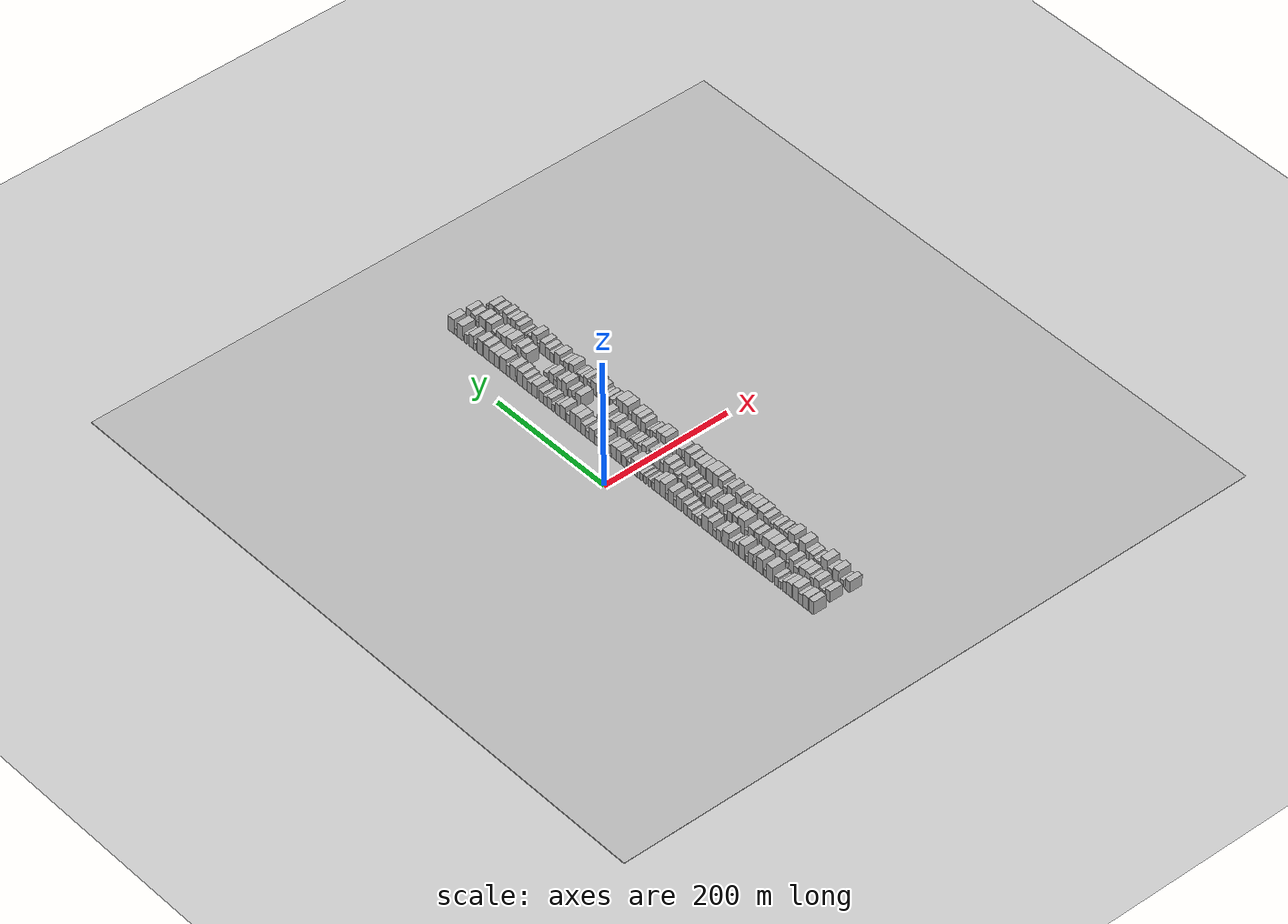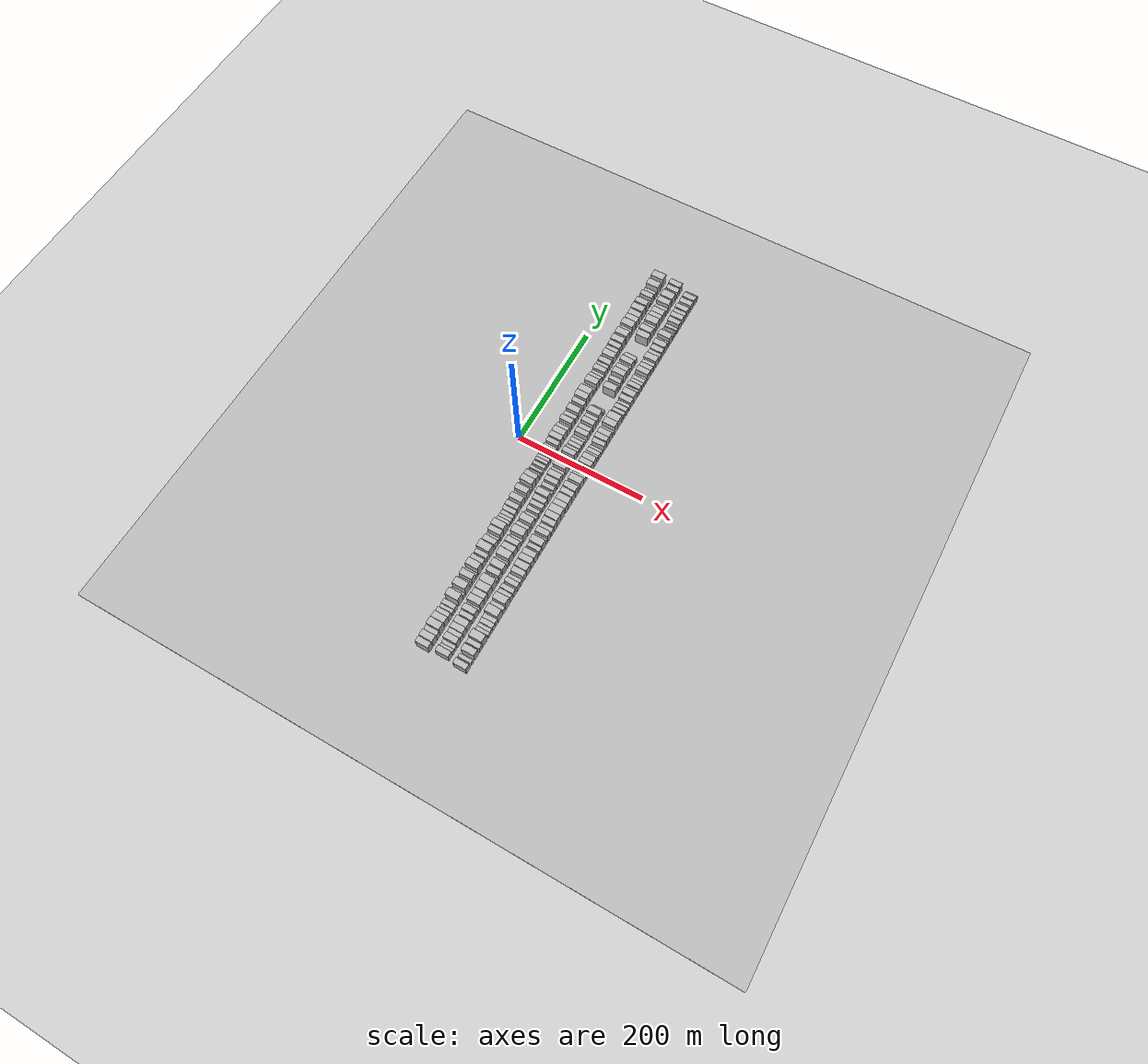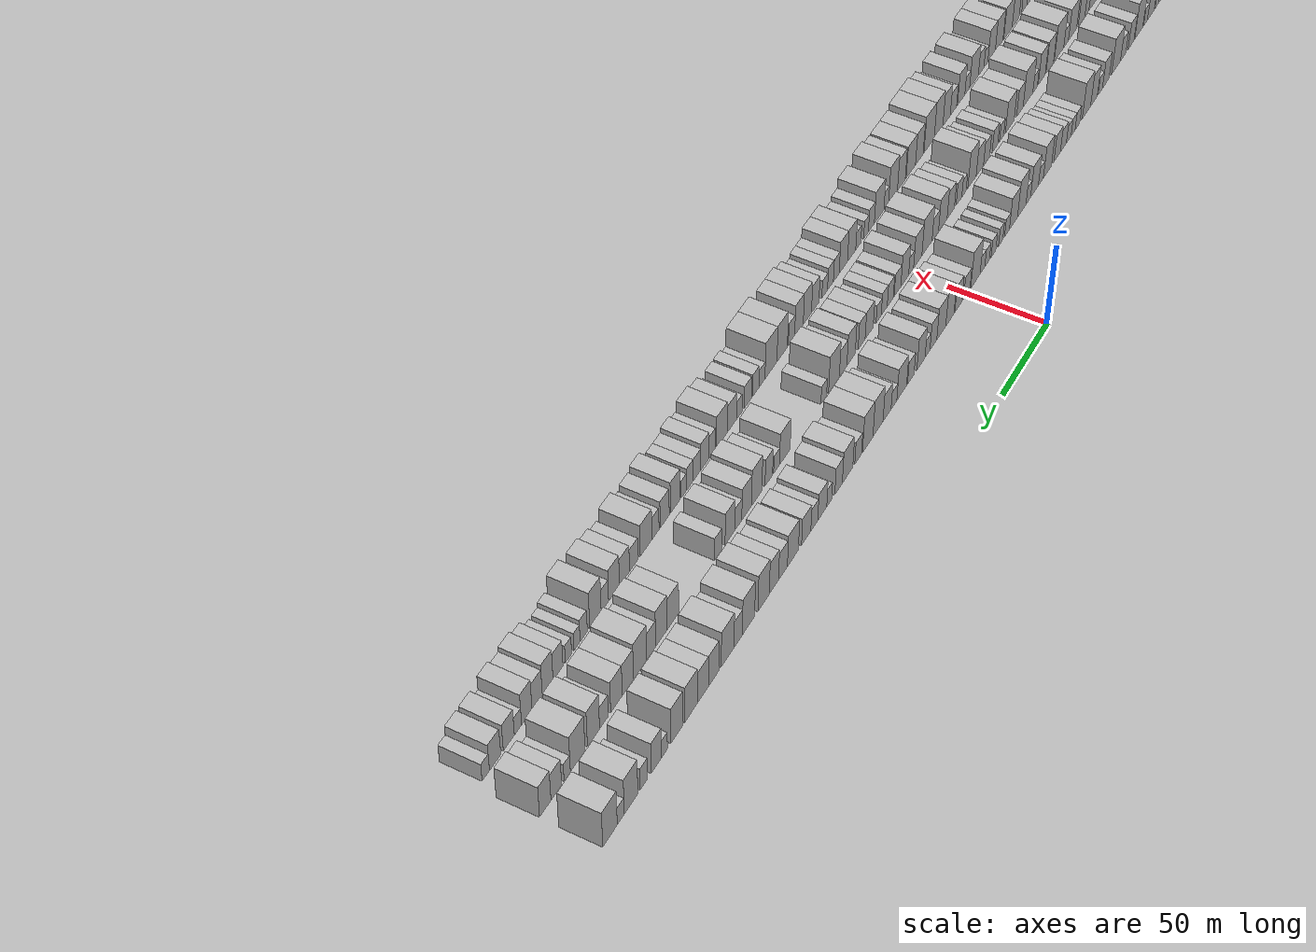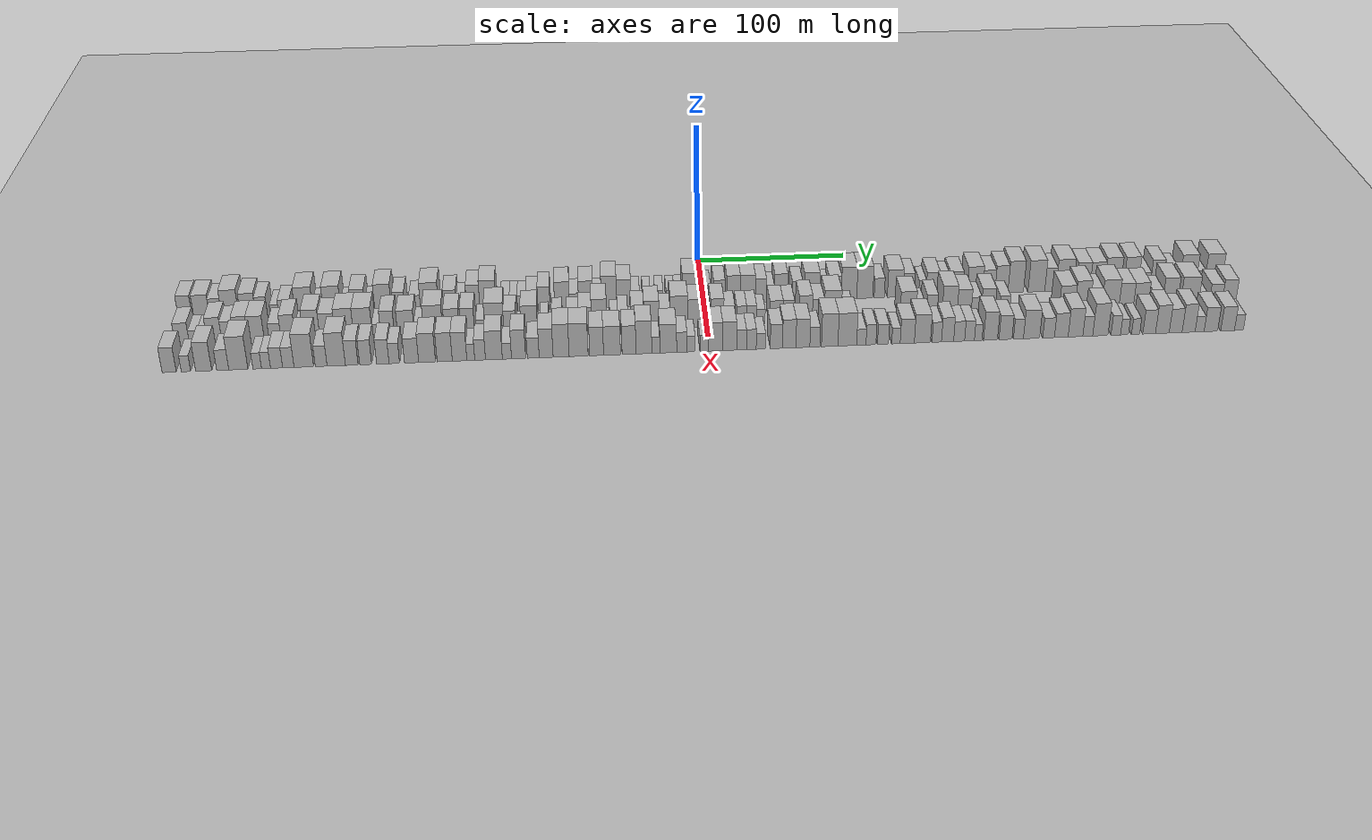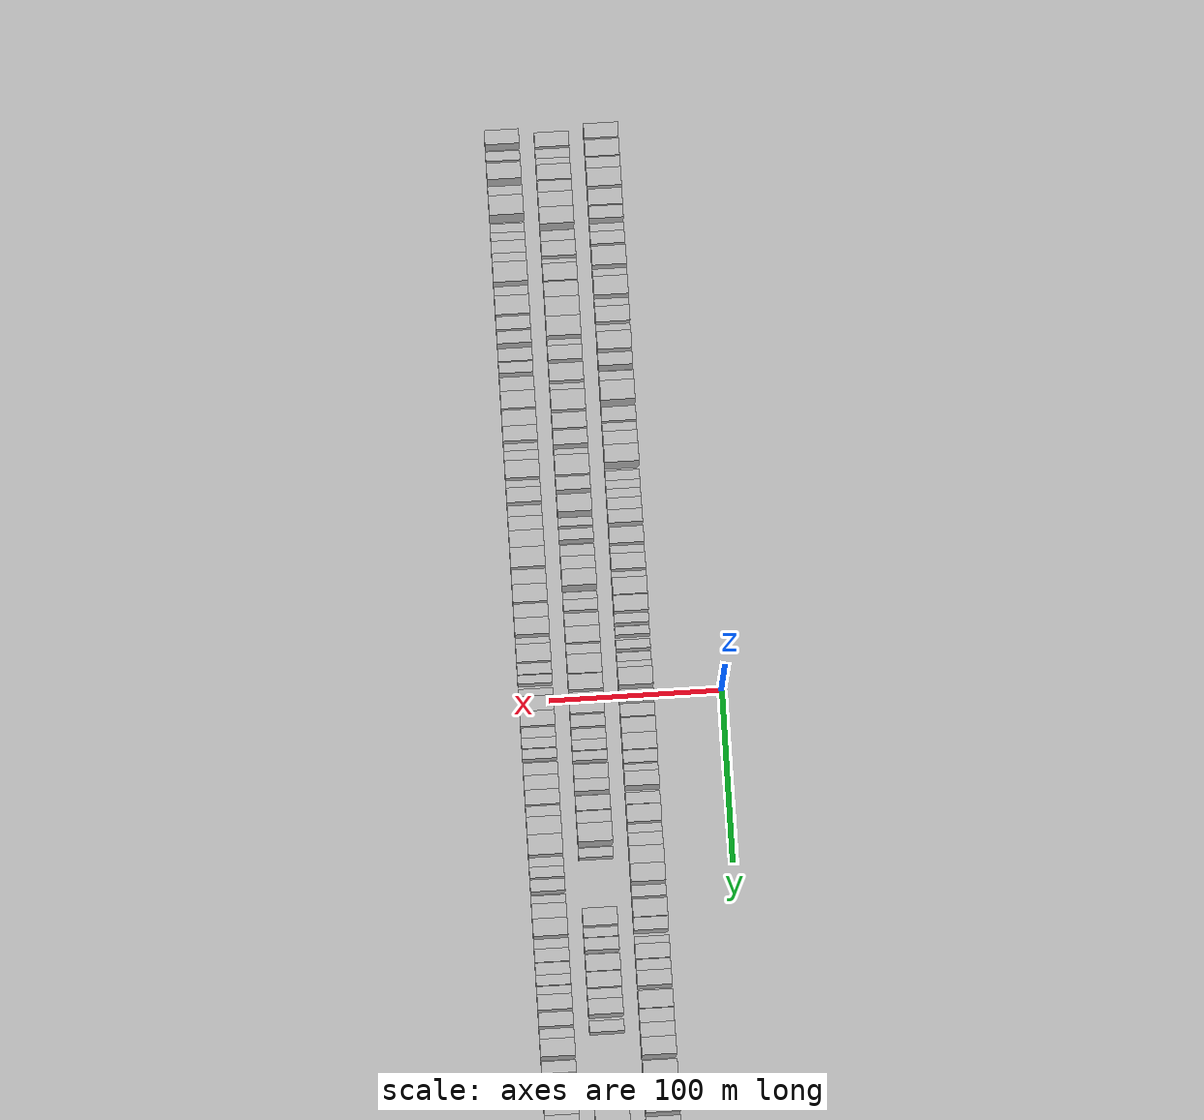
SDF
<?xml version="1.0" encoding="utf-8"?>

<sdf version="1.6">

   <world name="default">

      <gui fullscreen="0">

         <camera name="user_camera">

            <pose>-15 0 4.57585 0 0 0</pose>

            <view_controller>orbit</view_controller>

         </camera>

      </gui>

      <scene>

         <sky>

           <clouds>

             <speed>12</speed>

           </clouds>

         </sky>

         <ambient>0.4 0.4 0.4 1</ambient>

         <background>0.7 0.7 0.7 1</background>

         <shadows>1</shadows>

      </scene>

      <gravity>0 0 -9.8066</gravity>

      <magnetic_field>6e-06 2.3e-05 -4.2e-05</magnetic_field>

      <physics default="0" name="default_physics" type="ode">

         <ode>

            <solver>

               <type>quick</type>

               <iters>10</iters>

               <sor>1.0</sor>

               <use_dynamic_moi_rescaling>0</use_dynamic_moi_rescaling>

            </solver>

            <constraints>

               <cfm>0</cfm>

               <erp>0.2</erp>

               <contact_max_correcting_vel>100</contact_max_correcting_vel>

               <contact_surface_layer>0.001</contact_surface_layer>

            </constraints>

         </ode>

         <max_step_size>0.004</max_step_size>

         <real_time_factor>1</real_time_factor>

         <real_time_update_rate>250</real_time_update_rate>

      </physics>

      <light name="sun" type="directional">

         <cast_shadows>1</cast_shadows>

         <pose>0 0 10 0 0 0</pose>

         <diffuse>0.8 0.8 0.8 1</diffuse>

         <specular>0.2 0.2 0.2 1</specular>

         <attenuation>

            <range>1000</range>

            <constant>0.9</constant>

            <linear>0.01</linear>

            <quadratic>0.001</quadratic>

         </attenuation>

         <direction>-0.5 0.1 -0.9</direction>

      </light>

      <include>

         <name>ground_plane_1</name>

         <uri>model://HANNAS_ground_plane</uri>

         <pose>0 0 0  0 0 0</pose>

      </include>

      <include>

         <name>ground_plane_2</name>

         <uri>model://HANNAS_ground_plane</uri>

         <pose>100 0 0  0 0 0</pose>

      </include>

      <model name="building_1">

         <static>1</static>

         <pose frame="">50.0000 -331.6233 0 0.000000 0.000000 0.000000</pose>

         <link name="link">

            <pose frame="">0 0 10.50 0 0 0</pose>

            <collision name="collision">

               <geometry>

                  <box>

                     <size>20.0000 8.7534 21.0000</size>

                  </box>

               </geometry>

               <max_contacts>10</max_contacts>

               <surface>

                  <contact>

                     <ode/>

                  </contact>

                  <bounce/>

                  <friction>

                     <torsional>

                        <ode/>

                     </torsional>

                     <ode/>

                  </friction>

               </surface>

            </collision>

            <visual name="visual">

               <cast_shadows>0</cast_shadows>

               <geometry>

                  <box>

                     <size>20.0000 8.7534 21.0000</size>

                  </box>

               </geometry>

               <material>

                  <script>

                     <uri>model://HANNAS_wall/materials/scripts</uri>

                     <uri>model://HANNAS_wall/materials/textures</uri>

                     <name>vrc/HANNAS_wall</name>

                  </script>

               </material>

            </visual>

            <self_collide>0</self_collide>

            <enable_wind>0</enable_wind>

            <kinematic>0</kinematic>

         </link>

      </model>

      <model name="building_2">

         <static>1</static>

         <pose frame="">50.0000 -321.3111 0 0.000000 0.000000 0.000000</pose>

         <link name="link">

            <pose frame="">0 0 10.50 0 0 0</pose>

            <collision name="collision">

               <geometry>

                  <box>

                     <size>20.0000 9.8710 21.0000</size>

                  </box>

               </geometry>

               <max_contacts>10</max_contacts>

               <surface>

                  <contact>

                     <ode/>

                  </contact>

                  <bounce/>

                  <friction>

                     <torsional>

                        <ode/>

                     </torsional>

                     <ode/>

                  </friction>

               </surface>

            </collision>

            <visual name="visual">

               <cast_shadows>0</cast_shadows>

               <geometry>

                  <box>

                     <size>20.0000 9.8710 21.0000</size>

                  </box>

               </geometry>

               <material>

                  <script>

                     <uri>model://HANNAS_wall/materials/scripts</uri>

                     <uri>model://HANNAS_wall/materials/textures</uri>

                     <name>vrc/HANNAS_wall</name>

                  </script>

               </material>

            </visual>

            <self_collide>0</self_collide>

            <enable_wind>0</enable_wind>

            <kinematic>0</kinematic>

         </link>

      </model>

      <model name="building_3">

         <static>1</static>

         <pose frame="">50.0000 -312.5287 0 0.000000 0.000000 0.000000</pose>

         <link name="link">

            <pose frame="">0 0 9.00 0 0 0</pose>

            <collision name="collision">

               <geometry>

                  <box>

                     <size>20.0000 7.6939 18.0000</size>

                  </box>

               </geometry>

               <max_contacts>10</max_contacts>

               <surface>

                  <contact>

                     <ode/>

                  </contact>

                  <bounce/>

                  <friction>

                     <torsional>

                        <ode/>

                     </torsional>

                     <ode/>

                  </friction>

               </surface>

            </collision>

            <visual name="visual">

               <cast_shadows>0</cast_shadows>

               <geometry>

                  <box>

                     <size>20.0000 7.6939 18.0000</size>

                  </box>

               </geometry>

               <material>

                  <script>

                     <uri>model://HANNAS_wall/materials/scripts</uri>

                     <uri>model://HANNAS_wall/materials/textures</uri>

                     <name>vrc/HANNAS_wall</name>

                  </script>

               </material>

            </visual>

            <self_collide>0</self_collide>

            <enable_wind>0</enable_wind>

            <kinematic>0</kinematic>

         </link>

      </model>

      <model name="building_4">

         <static>1</static>

         <pose frame="">50.0000 -303.2883 0 0.000000 0.000000 0.000000</pose>

         <link name="link">

            <pose frame="">0 0 12.00 0 0 0</pose>

            <collision name="collision">

               <geometry>

                  <box>

                     <size>20.0000 10.7868 24.0000</size>

                  </box>

               </geometry>

               <max_contacts>10</max_contacts>

               <surface>

                  <contact>

                     <ode/>

                  </contact>

                  <bounce/>

                  <friction>

                     <torsional>

                        <ode/>

                     </torsional>

                     <ode/>

                  </friction>

               </surface>

            </collision>

            <visual name="visual">

               <cast_shadows>0</cast_shadows>

               <geometry>

                  <box>

                     <size>20.0000 10.7868 24.0000</size>

                  </box>

               </geometry>

               <material>

                  <script>

                     <uri>model://HANNAS_wall/materials/scripts</uri>

                     <uri>model://HANNAS_wall/materials/textures</uri>

                     <name>vrc/HANNAS_wall</name>

                  </script>

               </material>

            </visual>

            <self_collide>0</self_collide>

            <enable_wind>0</enable_wind>

            <kinematic>0</kinematic>

         </link>

      </model>

      <model name="building_5">

         <static>1</static>

         <pose frame="">50.0000 -292.0985 0 0.000000 0.000000 0.000000</pose>

         <link name="link">

            <pose frame="">0 0 10.50 0 0 0</pose>

            <collision name="collision">

               <geometry>

                  <box>

                     <size>20.0000 9.5930 21.0000</size>

                  </box>

               </geometry>

               <max_contacts>10</max_contacts>

               <surface>

                  <contact>

                     <ode/>

                  </contact>

                  <bounce/>

                  <friction>

                     <torsional>

                        <ode/>

                     </torsional>

                     <ode/>

                  </friction>

               </surface>

            </collision>

            <visual name="visual">

               <cast_shadows>0</cast_shadows>

               <geometry>

                  <box>

                     <size>20.0000 9.5930 21.0000</size>

                  </box>

               </geometry>

               <material>

                  <script>

                     <uri>model://HANNAS_wall/materials/scripts</uri>

                     <uri>model://HANNAS_wall/materials/textures</uri>

                     <name>vrc/HANNAS_wall</name>

                  </script>

               </material>

            </visual>

            <self_collide>0</self_collide>

            <enable_wind>0</enable_wind>

            <kinematic>0</kinematic>

         </link>

      </model>

      <model name="building_6">

         <static>1</static>

         <pose frame="">50.0000 -283.6206 0 0.000000 0.000000 0.000000</pose>

         <link name="link">

            <pose frame="">0 0 9.00 0 0 0</pose>

            <collision name="collision">

               <geometry>

                  <box>

                     <size>20.0000 7.3626 18.0000</size>

                  </box>

               </geometry>

               <max_contacts>10</max_contacts>

               <surface>

                  <contact>

                     <ode/>

                  </contact>

                  <bounce/>

                  <friction>

                     <torsional>

                        <ode/>

                     </torsional>

                     <ode/>

                  </friction>

               </surface>

            </collision>

            <visual name="visual">

               <cast_shadows>0</cast_shadows>

               <geometry>

                  <box>

                     <size>20.0000 7.3626 18.0000</size>

                  </box>

               </geometry>

               <material>

                  <script>

                     <uri>model://HANNAS_wall/materials/scripts</uri>

                     <uri>model://HANNAS_wall/materials/textures</uri>

                     <name>vrc/HANNAS_wall</name>

                  </script>

               </material>

            </visual>

            <self_collide>0</self_collide>

            <enable_wind>0</enable_wind>

            <kinematic>0</kinematic>

         </link>

      </model>

      <model name="building_7">

         <static>1</static>

         <pose frame="">50.0000 -275.3418 0 0.000000 0.000000 0.000000</pose>

         <link name="link">

            <pose frame="">0 0 6.00 0 0 0</pose>

            <collision name="collision">

               <geometry>

                  <box>

                     <size>20.0000 5.1951 12.0000</size>

                  </box>

               </geometry>

               <max_contacts>10</max_contacts>

               <surface>

                  <contact>

                     <ode/>

                  </contact>

                  <bounce/>

                  <friction>

                     <torsional>

                        <ode/>

                     </torsional>

                     <ode/>

                  </friction>

               </surface>

            </collision>

            <visual name="visual">

               <cast_shadows>0</cast_shadows>

               <geometry>

                  <box>

                     <size>20.0000 5.1951 12.0000</size>

                  </box>

               </geometry>

               <material>

                  <script>

                     <uri>model://HANNAS_wall/materials/scripts</uri>

                     <uri>model://HANNAS_wall/materials/textures</uri>

                     <name>vrc/HANNAS_wall</name>

                  </script>

               </material>

            </visual>

            <self_collide>0</self_collide>

            <enable_wind>0</enable_wind>

            <kinematic>0</kinematic>

         </link>

      </model>

      <model name="building_8">

         <static>1</static>

         <pose frame="">50.0000 -269.0176 0 0.000000 0.000000 0.000000</pose>

         <link name="link">

            <pose frame="">0 0 7.50 0 0 0</pose>

            <collision name="collision">

               <geometry>

                  <box>

                     <size>20.0000 7.4532 15.0000</size>

                  </box>

               </geometry>

               <max_contacts>10</max_contacts>

               <surface>

                  <contact>

                     <ode/>

                  </contact>

                  <bounce/>

                  <friction>

                     <torsional>

                        <ode/>

                     </torsional>

                     <ode/>

                  </friction>

               </surface>

            </collision>

            <visual name="visual">

               <cast_shadows>0</cast_shadows>

               <geometry>

                  <box>

                     <size>20.0000 7.4532 15.0000</size>

                  </box>

               </geometry>

               <material>

                  <script>

                     <uri>model://HANNAS_wall/materials/scripts</uri>

                     <uri>model://HANNAS_wall/materials/textures</uri>

                     <name>vrc/HANNAS_wall</name>

                  </script>

               </material>

            </visual>

            <self_collide>0</self_collide>

            <enable_wind>0</enable_wind>

            <kinematic>0</kinematic>

         </link>

      </model>

      <model name="building_9">

         <static>1</static>

         <pose frame="">50.0000 -256.6144 0 0.000000 0.000000 0.000000</pose>

         <link name="link">

            <pose frame="">0 0 12.00 0 0 0</pose>

            <collision name="collision">

               <geometry>

                  <box>

                     <size>20.0000 11.3533 24.0000</size>

                  </box>

               </geometry>

               <max_contacts>10</max_contacts>

               <surface>

                  <contact>

                     <ode/>

                  </contact>

                  <bounce/>

                  <friction>

                     <torsional>

                        <ode/>

                     </torsional>

                     <ode/>

                  </friction>

               </surface>

            </collision>

            <visual name="visual">

               <cast_shadows>0</cast_shadows>

               <geometry>

                  <box>

                     <size>20.0000 11.3533 24.0000</size>

                  </box>

               </geometry>

               <material>

                  <script>

                     <uri>model://HANNAS_wall/materials/scripts</uri>

                     <uri>model://HANNAS_wall/materials/textures</uri>

                     <name>vrc/HANNAS_wall</name>

                  </script>

               </material>

            </visual>

            <self_collide>0</self_collide>

            <enable_wind>0</enable_wind>

            <kinematic>0</kinematic>

         </link>

      </model>

      <model name="building_10">

         <static>1</static>

         <pose frame="">50.0000 -248.1485 0 0.000000 0.000000 0.000000</pose>

         <link name="link">

            <pose frame="">0 0 6.00 0 0 0</pose>

            <collision name="collision">

               <geometry>

                  <box>

                     <size>20.0000 5.5785 12.0000</size>

                  </box>

               </geometry>

               <max_contacts>10</max_contacts>

               <surface>

                  <contact>

                     <ode/>

                  </contact>

                  <bounce/>

                  <friction>

                     <torsional>

                        <ode/>

                     </torsional>

                     <ode/>

                  </friction>

               </surface>

            </collision>

            <visual name="visual">

               <cast_shadows>0</cast_shadows>

               <geometry>

                  <box>

                     <size>20.0000 5.5785 12.0000</size>

                  </box>

               </geometry>

               <material>

                  <script>

                     <uri>model://HANNAS_wall/materials/scripts</uri>

                     <uri>model://HANNAS_wall/materials/textures</uri>

                     <name>vrc/HANNAS_wall</name>

                  </script>

               </material>

            </visual>

            <self_collide>0</self_collide>

            <enable_wind>0</enable_wind>

            <kinematic>0</kinematic>

         </link>

      </model>

      <model name="building_11">

         <static>1</static>

         <pose frame="">50.0000 -238.7965 0 0.000000 0.000000 0.000000</pose>

         <link name="link">

            <pose frame="">0 0 12.00 0 0 0</pose>

            <collision name="collision">

               <geometry>

                  <box>

                     <size>20.0000 11.1255 24.0000</size>

                  </box>

               </geometry>

               <max_contacts>10</max_contacts>

               <surface>

                  <contact>

                     <ode/>

                  </contact>

                  <bounce/>

                  <friction>

                     <torsional>

                        <ode/>

                     </torsional>

                     <ode/>

                  </friction>

               </surface>

            </collision>

            <visual name="visual">

               <cast_shadows>0</cast_shadows>

               <geometry>

                  <box>

                     <size>20.0000 11.1255 24.0000</size>

                  </box>

               </geometry>

               <material>

                  <script>

                     <uri>model://HANNAS_wall/materials/scripts</uri>

                     <uri>model://HANNAS_wall/materials/textures</uri>

                     <name>vrc/HANNAS_wall</name>

                  </script>

               </material>

            </visual>

            <self_collide>0</self_collide>

            <enable_wind>0</enable_wind>

            <kinematic>0</kinematic>

         </link>

      </model>

      <model name="building_12">

         <static>1</static>

         <pose frame="">50.0000 -230.6441 0 0.000000 0.000000 0.000000</pose>

         <link name="link">

            <pose frame="">0 0 6.00 0 0 0</pose>

            <collision name="collision">

               <geometry>

                  <box>

                     <size>20.0000 5.1793 12.0000</size>

                  </box>

               </geometry>

               <max_contacts>10</max_contacts>

               <surface>

                  <contact>

                     <ode/>

                  </contact>

                  <bounce/>

                  <friction>

                     <torsional>

                        <ode/>

                     </torsional>

                     <ode/>

                  </friction>

               </surface>

            </collision>

            <visual name="visual">

               <cast_shadows>0</cast_shadows>

               <geometry>

                  <box>

                     <size>20.0000 5.1793 12.0000</size>

                  </box>

               </geometry>

               <material>

                  <script>

                     <uri>model://HANNAS_wall/materials/scripts</uri>

                     <uri>model://HANNAS_wall/materials/textures</uri>

                     <name>vrc/HANNAS_wall</name>

                  </script>

               </material>

            </visual>

            <self_collide>0</self_collide>

            <enable_wind>0</enable_wind>

            <kinematic>0</kinematic>

         </link>

      </model>

      <model name="building_13">

         <static>1</static>

         <pose frame="">50.0000 -222.4367 0 0.000000 0.000000 0.000000</pose>

         <link name="link">

            <pose frame="">0 0 10.50 0 0 0</pose>

            <collision name="collision">

               <geometry>

                  <box>

                     <size>20.0000 9.2356 21.0000</size>

                  </box>

               </geometry>

               <max_contacts>10</max_contacts>

               <surface>

                  <contact>

                     <ode/>

                  </contact>

                  <bounce/>

                  <friction>

                     <torsional>

                        <ode/>

                     </torsional>

                     <ode/>

                  </friction>

               </surface>

            </collision>

            <visual name="visual">

               <cast_shadows>0</cast_shadows>

               <geometry>

                  <box>

                     <size>20.0000 9.2356 21.0000</size>

                  </box>

               </geometry>

               <material>

                  <script>

                     <uri>model://HANNAS_wall/materials/scripts</uri>

                     <uri>model://HANNAS_wall/materials/textures</uri>

                     <name>vrc/HANNAS_wall</name>

                  </script>

               </material>

            </visual>

            <self_collide>0</self_collide>

            <enable_wind>0</enable_wind>

            <kinematic>0</kinematic>

         </link>

      </model>

      <model name="building_14">

         <static>1</static>

         <pose frame="">50.0000 -215.2463 0 0.000000 0.000000 0.000000</pose>

         <link name="link">

            <pose frame="">0 0 6.00 0 0 0</pose>

            <collision name="collision">

               <geometry>

                  <box>

                     <size>20.0000 5.1452 12.0000</size>

                  </box>

               </geometry>

               <max_contacts>10</max_contacts>

               <surface>

                  <contact>

                     <ode/>

                  </contact>

                  <bounce/>

                  <friction>

                     <torsional>

                        <ode/>

                     </torsional>

                     <ode/>

                  </friction>

               </surface>

            </collision>

            <visual name="visual">

               <cast_shadows>0</cast_shadows>

               <geometry>

                  <box>

                     <size>20.0000 5.1452 12.0000</size>

                  </box>

               </geometry>

               <material>

                  <script>

                     <uri>model://HANNAS_wall/materials/scripts</uri>

                     <uri>model://HANNAS_wall/materials/textures</uri>

                     <name>vrc/HANNAS_wall</name>

                  </script>

               </material>

            </visual>

            <self_collide>0</self_collide>

            <enable_wind>0</enable_wind>

            <kinematic>0</kinematic>

         </link>

      </model>

      <model name="building_15">

         <static>1</static>

         <pose frame="">50.0000 -206.3878 0 0.000000 0.000000 0.000000</pose>

         <link name="link">

            <pose frame="">0 0 12.00 0 0 0</pose>

            <collision name="collision">

               <geometry>

                  <box>

                     <size>20.0000 10.5718 24.0000</size>

                  </box>

               </geometry>

               <max_contacts>10</max_contacts>

               <surface>

                  <contact>

                     <ode/>

                  </contact>

                  <bounce/>

                  <friction>

                     <torsional>

                        <ode/>

                     </torsional>

                     <ode/>

                  </friction>

               </surface>

            </collision>

            <visual name="visual">

               <cast_shadows>0</cast_shadows>

               <geometry>

                  <box>

                     <size>20.0000 10.5718 24.0000</size>

                  </box>

               </geometry>

               <material>

                  <script>

                     <uri>model://HANNAS_wall/materials/scripts</uri>

                     <uri>model://HANNAS_wall/materials/textures</uri>

                     <name>vrc/HANNAS_wall</name>

                  </script>

               </material>

            </visual>

            <self_collide>0</self_collide>

            <enable_wind>0</enable_wind>

            <kinematic>0</kinematic>

         </link>

      </model>

      <model name="building_16">

         <static>1</static>

         <pose frame="">50.0000 -196.3300 0 0.000000 0.000000 0.000000</pose>

         <link name="link">

            <pose frame="">0 0 9.00 0 0 0</pose>

            <collision name="collision">

               <geometry>

                  <box>

                     <size>20.0000 7.5437 18.0000</size>

                  </box>

               </geometry>

               <max_contacts>10</max_contacts>

               <surface>

                  <contact>

                     <ode/>

                  </contact>

                  <bounce/>

                  <friction>

                     <torsional>

                        <ode/>

                     </torsional>

                     <ode/>

                  </friction>

               </surface>

            </collision>

            <visual name="visual">

               <cast_shadows>0</cast_shadows>

               <geometry>

                  <box>

                     <size>20.0000 7.5437 18.0000</size>

                  </box>

               </geometry>

               <material>

                  <script>

                     <uri>model://HANNAS_wall/materials/scripts</uri>

                     <uri>model://HANNAS_wall/materials/textures</uri>

                     <name>vrc/HANNAS_wall</name>

                  </script>

               </material>

            </visual>

            <self_collide>0</self_collide>

            <enable_wind>0</enable_wind>

            <kinematic>0</kinematic>

         </link>

      </model>

      <model name="building_17">

         <static>1</static>

         <pose frame="">50.0000 -186.0587 0 0.000000 0.000000 0.000000</pose>

         <link name="link">

            <pose frame="">0 0 7.50 0 0 0</pose>

            <collision name="collision">

               <geometry>

                  <box>

                     <size>20.0000 6.9990 15.0000</size>

                  </box>

               </geometry>

               <max_contacts>10</max_contacts>

               <surface>

                  <contact>

                     <ode/>

                  </contact>

                  <bounce/>

                  <friction>

                     <torsional>

                        <ode/>

                     </torsional>

                     <ode/>

                  </friction>

               </surface>

            </collision>

            <visual name="visual">

               <cast_shadows>0</cast_shadows>

               <geometry>

                  <box>

                     <size>20.0000 6.9990 15.0000</size>

                  </box>

               </geometry>

               <material>

                  <script>

                     <uri>model://HANNAS_wall/materials/scripts</uri>

                     <uri>model://HANNAS_wall/materials/textures</uri>

                     <name>vrc/HANNAS_wall</name>

                  </script>

               </material>

            </visual>

            <self_collide>0</self_collide>

            <enable_wind>0</enable_wind>

            <kinematic>0</kinematic>

         </link>

      </model>

      <model name="building_18">

         <static>1</static>

         <pose frame="">50.0000 -176.7845 0 0.000000 0.000000 0.000000</pose>

         <link name="link">

            <pose frame="">0 0 12.00 0 0 0</pose>

            <collision name="collision">

               <geometry>

                  <box>

                     <size>20.0000 11.5493 24.0000</size>

                  </box>

               </geometry>

               <max_contacts>10</max_contacts>

               <surface>

                  <contact>

                     <ode/>

                  </contact>

                  <bounce/>

                  <friction>

                     <torsional>

                        <ode/>

                     </torsional>

                     <ode/>

                  </friction>

               </surface>

            </collision>

            <visual name="visual">

               <cast_shadows>0</cast_shadows>

               <geometry>

                  <box>

                     <size>20.0000 11.5493 24.0000</size>

                  </box>

               </geometry>

               <material>

                  <script>

                     <uri>model://HANNAS_wall/materials/scripts</uri>

                     <uri>model://HANNAS_wall/materials/textures</uri>

                     <name>vrc/HANNAS_wall</name>

                  </script>

               </material>

            </visual>

            <self_collide>0</self_collide>

            <enable_wind>0</enable_wind>

            <kinematic>0</kinematic>

         </link>

      </model>

      <model name="building_19">

         <static>1</static>

         <pose frame="">50.0000 -163.7969 0 0.000000 0.000000 0.000000</pose>

         <link name="link">

            <pose frame="">0 0 9.00 0 0 0</pose>

            <collision name="collision">

               <geometry>

                  <box>

                     <size>20.0000 8.4260 18.0000</size>

                  </box>

               </geometry>

               <max_contacts>10</max_contacts>

               <surface>

                  <contact>

                     <ode/>

                  </contact>

                  <bounce/>

                  <friction>

                     <torsional>

                        <ode/>

                     </torsional>

                     <ode/>

                  </friction>

               </surface>

            </collision>

            <visual name="visual">

               <cast_shadows>0</cast_shadows>

               <geometry>

                  <box>

                     <size>20.0000 8.4260 18.0000</size>

                  </box>

               </geometry>

               <material>

                  <script>

                     <uri>model://HANNAS_wall/materials/scripts</uri>

                     <uri>model://HANNAS_wall/materials/textures</uri>

                     <name>vrc/HANNAS_wall</name>

                  </script>

               </material>

            </visual>

            <self_collide>0</self_collide>

            <enable_wind>0</enable_wind>

            <kinematic>0</kinematic>

         </link>

      </model>

      <model name="building_20">

         <static>1</static>

         <pose frame="">50.0000 -156.8448 0 0.000000 0.000000 0.000000</pose>

         <link name="link">

            <pose frame="">0 0 6.00 0 0 0</pose>

            <collision name="collision">

               <geometry>

                  <box>

                     <size>20.0000 5.4781 12.0000</size>

                  </box>

               </geometry>

               <max_contacts>10</max_contacts>

               <surface>

                  <contact>

                     <ode/>

                  </contact>

                  <bounce/>

                  <friction>

                     <torsional>

                        <ode/>

                     </torsional>

                     <ode/>

                  </friction>

               </surface>

            </collision>

            <visual name="visual">

               <cast_shadows>0</cast_shadows>

               <geometry>

                  <box>

                     <size>20.0000 5.4781 12.0000</size>

                  </box>

               </geometry>

               <material>

                  <script>

                     <uri>model://HANNAS_wall/materials/scripts</uri>

                     <uri>model://HANNAS_wall/materials/textures</uri>

                     <name>vrc/HANNAS_wall</name>

                  </script>

               </material>

            </visual>

            <self_collide>0</self_collide>

            <enable_wind>0</enable_wind>

            <kinematic>0</kinematic>

         </link>

      </model>

      <model name="building_21">

         <static>1</static>

         <pose frame="">50.0000 -148.9028 0 0.000000 0.000000 0.000000</pose>

         <link name="link">

            <pose frame="">0 0 10.50 0 0 0</pose>

            <collision name="collision">

               <geometry>

                  <box>

                     <size>20.0000 8.4060 21.0000</size>

                  </box>

               </geometry>

               <max_contacts>10</max_contacts>

               <surface>

                  <contact>

                     <ode/>

                  </contact>

                  <bounce/>

                  <friction>

                     <torsional>

                        <ode/>

                     </torsional>

                     <ode/>

                  </friction>

               </surface>

            </collision>

            <visual name="visual">

               <cast_shadows>0</cast_shadows>

               <geometry>

                  <box>

                     <size>20.0000 8.4060 21.0000</size>

                  </box>

               </geometry>

               <material>

                  <script>

                     <uri>model://HANNAS_wall/materials/scripts</uri>

                     <uri>model://HANNAS_wall/materials/textures</uri>

                     <name>vrc/HANNAS_wall</name>

                  </script>

               </material>

            </visual>

            <self_collide>0</self_collide>

            <enable_wind>0</enable_wind>

            <kinematic>0</kinematic>

         </link>

      </model>

      <model name="building_22">

         <static>1</static>

         <pose frame="">50.0000 -139.4966 0 0.000000 0.000000 0.000000</pose>

         <link name="link">

            <pose frame="">0 0 12.00 0 0 0</pose>

            <collision name="collision">

               <geometry>

                  <box>

                     <size>20.0000 10.4064 24.0000</size>

                  </box>

               </geometry>

               <max_contacts>10</max_contacts>

               <surface>

                  <contact>

                     <ode/>

                  </contact>

                  <bounce/>

                  <friction>

                     <torsional>

                        <ode/>

                     </torsional>

                     <ode/>

                  </friction>

               </surface>

            </collision>

            <visual name="visual">

               <cast_shadows>0</cast_shadows>

               <geometry>

                  <box>

                     <size>20.0000 10.4064 24.0000</size>

                  </box>

               </geometry>

               <material>

                  <script>

                     <uri>model://HANNAS_wall/materials/scripts</uri>

                     <uri>model://HANNAS_wall/materials/textures</uri>

                     <name>vrc/HANNAS_wall</name>

                  </script>

               </material>

            </visual>

            <self_collide>0</self_collide>

            <enable_wind>0</enable_wind>

            <kinematic>0</kinematic>

         </link>

      </model>

      <model name="building_23">

         <static>1</static>

         <pose frame="">50.0000 -128.4307 0 0.000000 0.000000 0.000000</pose>

         <link name="link">

            <pose frame="">0 0 6.00 0 0 0</pose>

            <collision name="collision">

               <geometry>

                  <box>

                     <size>20.0000 5.7254 12.0000</size>

                  </box>

               </geometry>

               <max_contacts>10</max_contacts>

               <surface>

                  <contact>

                     <ode/>

                  </contact>

                  <bounce/>

                  <friction>

                     <torsional>

                        <ode/>

                     </torsional>

                     <ode/>

                  </friction>

               </surface>

            </collision>

            <visual name="visual">

               <cast_shadows>0</cast_shadows>

               <geometry>

                  <box>

                     <size>20.0000 5.7254 12.0000</size>

                  </box>

               </geometry>

               <material>

                  <script>

                     <uri>model://HANNAS_wall/materials/scripts</uri>

                     <uri>model://HANNAS_wall/materials/textures</uri>

                     <name>vrc/HANNAS_wall</name>

                  </script>

               </material>

            </visual>

            <self_collide>0</self_collide>

            <enable_wind>0</enable_wind>

            <kinematic>0</kinematic>

         </link>

      </model>

      <model name="building_24">

         <static>1</static>

         <pose frame="">50.0000 -123.0861 0 0.000000 0.000000 0.000000</pose>

         <link name="link">

            <pose frame="">0 0 6.00 0 0 0</pose>

            <collision name="collision">

               <geometry>

                  <box>

                     <size>20.0000 4.9639 12.0000</size>

                  </box>

               </geometry>

               <max_contacts>10</max_contacts>

               <surface>

                  <contact>

                     <ode/>

                  </contact>

                  <bounce/>

                  <friction>

                     <torsional>

                        <ode/>

                     </torsional>

                     <ode/>

                  </friction>

               </surface>

            </collision>

            <visual name="visual">

               <cast_shadows>0</cast_shadows>

               <geometry>

                  <box>

                     <size>20.0000 4.9639 12.0000</size>

                  </box>

               </geometry>

               <material>

                  <script>

                     <uri>model://HANNAS_wall/materials/scripts</uri>

                     <uri>model://HANNAS_wall/materials/textures</uri>

                     <name>vrc/HANNAS_wall</name>

                  </script>

               </material>

            </visual>

            <self_collide>0</self_collide>

            <enable_wind>0</enable_wind>

            <kinematic>0</kinematic>

         </link>

      </model>

      <model name="building_25">

         <static>1</static>

         <pose frame="">50.0000 -117.6869 0 0.000000 0.000000 0.000000</pose>

         <link name="link">

            <pose frame="">0 0 6.00 0 0 0</pose>

            <collision name="collision">

               <geometry>

                  <box>

                     <size>20.0000 5.8345 12.0000</size>

                  </box>

               </geometry>

               <max_contacts>10</max_contacts>

               <surface>

                  <contact>

                     <ode/>

                  </contact>

                  <bounce/>

                  <friction>

                     <torsional>

                        <ode/>

                     </torsional>

                     <ode/>

                  </friction>

               </surface>

            </collision>

            <visual name="visual">

               <cast_shadows>0</cast_shadows>

               <geometry>

                  <box>

                     <size>20.0000 5.8345 12.0000</size>

                  </box>

               </geometry>

               <material>

                  <script>

                     <uri>model://HANNAS_wall/materials/scripts</uri>

                     <uri>model://HANNAS_wall/materials/textures</uri>

                     <name>vrc/HANNAS_wall</name>

                  </script>

               </material>

            </visual>

            <self_collide>0</self_collide>

            <enable_wind>0</enable_wind>

            <kinematic>0</kinematic>

         </link>

      </model>

      <model name="building_26">

         <static>1</static>

         <pose frame="">50.0000 -111.0916 0 0.000000 0.000000 0.000000</pose>

         <link name="link">

            <pose frame="">0 0 7.50 0 0 0</pose>

            <collision name="collision">

               <geometry>

                  <box>

                     <size>20.0000 7.3561 15.0000</size>

                  </box>

               </geometry>

               <max_contacts>10</max_contacts>

               <surface>

                  <contact>

                     <ode/>

                  </contact>

                  <bounce/>

                  <friction>

                     <torsional>

                        <ode/>

                     </torsional>

                     <ode/>

                  </friction>

               </surface>

            </collision>

            <visual name="visual">

               <cast_shadows>0</cast_shadows>

               <geometry>

                  <box>

                     <size>20.0000 7.3561 15.0000</size>

                  </box>

               </geometry>

               <material>

                  <script>

                     <uri>model://HANNAS_wall/materials/scripts</uri>

                     <uri>model://HANNAS_wall/materials/textures</uri>

                     <name>vrc/HANNAS_wall</name>

                  </script>

               </material>

            </visual>

            <self_collide>0</self_collide>

            <enable_wind>0</enable_wind>

            <kinematic>0</kinematic>

         </link>

      </model>

      <model name="building_27">

         <static>1</static>

         <pose frame="">50.0000 -103.5186 0 0.000000 0.000000 0.000000</pose>

         <link name="link">

            <pose frame="">0 0 9.00 0 0 0</pose>

            <collision name="collision">

               <geometry>

                  <box>

                     <size>20.0000 7.7900 18.0000</size>

                  </box>

               </geometry>

               <max_contacts>10</max_contacts>

               <surface>

                  <contact>

                     <ode/>

                  </contact>

                  <bounce/>

                  <friction>

                     <torsional>

                        <ode/>

                     </torsional>

                     <ode/>

                  </friction>

               </surface>

            </collision>

            <visual name="visual">

               <cast_shadows>0</cast_shadows>

               <geometry>

                  <box>

                     <size>20.0000 7.7900 18.0000</size>

                  </box>

               </geometry>

               <material>

                  <script>

                     <uri>model://HANNAS_wall/materials/scripts</uri>

                     <uri>model://HANNAS_wall/materials/textures</uri>

                     <name>vrc/HANNAS_wall</name>

                  </script>

               </material>

            </visual>

            <self_collide>0</self_collide>

            <enable_wind>0</enable_wind>

            <kinematic>0</kinematic>

         </link>

      </model>

      <model name="building_28">

         <static>1</static>

         <pose frame="">50.0000 -91.8596 0 0.000000 0.000000 0.000000</pose>

         <link name="link">

            <pose frame="">0 0 10.50 0 0 0</pose>

            <collision name="collision">

               <geometry>

                  <box>

                     <size>20.0000 9.5280 21.0000</size>

                  </box>

               </geometry>

               <max_contacts>10</max_contacts>

               <surface>

                  <contact>

                     <ode/>

                  </contact>

                  <bounce/>

                  <friction>

                     <torsional>

                        <ode/>

                     </torsional>

                     <ode/>

                  </friction>

               </surface>

            </collision>

            <visual name="visual">

               <cast_shadows>0</cast_shadows>

               <geometry>

                  <box>

                     <size>20.0000 9.5280 21.0000</size>

                  </box>

               </geometry>

               <material>

                  <script>

                     <uri>model://HANNAS_wall/materials/scripts</uri>

                     <uri>model://HANNAS_wall/materials/textures</uri>

                     <name>vrc/HANNAS_wall</name>

                  </script>

               </material>

            </visual>

            <self_collide>0</self_collide>

            <enable_wind>0</enable_wind>

            <kinematic>0</kinematic>

         </link>

      </model>

      <model name="building_29">

         <static>1</static>

         <pose frame="">50.0000 -84.0969 0 0.000000 0.000000 0.000000</pose>

         <link name="link">

            <pose frame="">0 0 6.00 0 0 0</pose>

            <collision name="collision">

               <geometry>

                  <box>

                     <size>20.0000 5.9974 12.0000</size>

                  </box>

               </geometry>

               <max_contacts>10</max_contacts>

               <surface>

                  <contact>

                     <ode/>

                  </contact>

                  <bounce/>

                  <friction>

                     <torsional>

                        <ode/>

                     </torsional>

                     <ode/>

                  </friction>

               </surface>

            </collision>

            <visual name="visual">

               <cast_shadows>0</cast_shadows>

               <geometry>

                  <box>

                     <size>20.0000 5.9974 12.0000</size>

                  </box>

               </geometry>

               <material>

                  <script>

                     <uri>model://HANNAS_wall/materials/scripts</uri>

                     <uri>model://HANNAS_wall/materials/textures</uri>

                     <name>vrc/HANNAS_wall</name>

                  </script>

               </material>

            </visual>

            <self_collide>0</self_collide>

            <enable_wind>0</enable_wind>

            <kinematic>0</kinematic>

         </link>

      </model>

      <model name="building_30">

         <static>1</static>

         <pose frame="">50.0000 -76.4811 0 0.000000 0.000000 0.000000</pose>

         <link name="link">

            <pose frame="">0 0 10.50 0 0 0</pose>

            <collision name="collision">

               <geometry>

                  <box>

                     <size>20.0000 9.2342 21.0000</size>

                  </box>

               </geometry>

               <max_contacts>10</max_contacts>

               <surface>

                  <contact>

                     <ode/>

                  </contact>

                  <bounce/>

                  <friction>

                     <torsional>

                        <ode/>

                     </torsional>

                     <ode/>

                  </friction>

               </surface>

            </collision>

            <visual name="visual">

               <cast_shadows>0</cast_shadows>

               <geometry>

                  <box>

                     <size>20.0000 9.2342 21.0000</size>

                  </box>

               </geometry>

               <material>

                  <script>

                     <uri>model://HANNAS_wall/materials/scripts</uri>

                     <uri>model://HANNAS_wall/materials/textures</uri>

                     <name>vrc/HANNAS_wall</name>

                  </script>

               </material>

            </visual>

            <self_collide>0</self_collide>

            <enable_wind>0</enable_wind>

            <kinematic>0</kinematic>

         </link>

      </model>

      <model name="building_31">

         <static>1</static>

         <pose frame="">50.0000 -69.1542 0 0.000000 0.000000 0.000000</pose>

         <link name="link">

            <pose frame="">0 0 6.00 0 0 0</pose>

            <collision name="collision">

               <geometry>

                  <box>

                     <size>20.0000 5.4197 12.0000</size>

                  </box>

               </geometry>

               <max_contacts>10</max_contacts>

               <surface>

                  <contact>

                     <ode/>

                  </contact>

                  <bounce/>

                  <friction>

                     <torsional>

                        <ode/>

                     </torsional>

                     <ode/>

                  </friction>

               </surface>

            </collision>

            <visual name="visual">

               <cast_shadows>0</cast_shadows>

               <geometry>

                  <box>

                     <size>20.0000 5.4197 12.0000</size>

                  </box>

               </geometry>

               <material>

                  <script>

                     <uri>model://HANNAS_wall/materials/scripts</uri>

                     <uri>model://HANNAS_wall/materials/textures</uri>

                     <name>vrc/HANNAS_wall</name>

                  </script>

               </material>

            </visual>

            <self_collide>0</self_collide>

            <enable_wind>0</enable_wind>

            <kinematic>0</kinematic>

         </link>

      </model>

      <model name="building_32">

         <static>1</static>

         <pose frame="">50.0000 -61.4947 0 0.000000 0.000000 0.000000</pose>

         <link name="link">

            <pose frame="">0 0 12.00 0 0 0</pose>

            <collision name="collision">

               <geometry>

                  <box>

                     <size>20.0000 9.8994 24.0000</size>

                  </box>

               </geometry>

               <max_contacts>10</max_contacts>

               <surface>

                  <contact>

                     <ode/>

                  </contact>

                  <bounce/>

                  <friction>

                     <torsional>

                        <ode/>

                     </torsional>

                     <ode/>

                  </friction>

               </surface>

            </collision>

            <visual name="visual">

               <cast_shadows>0</cast_shadows>

               <geometry>

                  <box>

                     <size>20.0000 9.8994 24.0000</size>

                  </box>

               </geometry>

               <material>

                  <script>

                     <uri>model://HANNAS_wall/materials/scripts</uri>

                     <uri>model://HANNAS_wall/materials/textures</uri>

                     <name>vrc/HANNAS_wall</name>

                  </script>

               </material>

            </visual>

            <self_collide>0</self_collide>

            <enable_wind>0</enable_wind>

            <kinematic>0</kinematic>

         </link>

      </model>

      <model name="building_33">

         <static>1</static>

         <pose frame="">50.0000 -51.8839 0 0.000000 0.000000 0.000000</pose>

         <link name="link">

            <pose frame="">0 0 10.50 0 0 0</pose>

            <collision name="collision">

               <geometry>

                  <box>

                     <size>20.0000 9.3221 21.0000</size>

                  </box>

               </geometry>

               <max_contacts>10</max_contacts>

               <surface>

                  <contact>

                     <ode/>

                  </contact>

                  <bounce/>

                  <friction>

                     <torsional>

                        <ode/>

                     </torsional>

                     <ode/>

                  </friction>

               </surface>

            </collision>

            <visual name="visual">

               <cast_shadows>0</cast_shadows>

               <geometry>

                  <box>

                     <size>20.0000 9.3221 21.0000</size>

                  </box>

               </geometry>

               <material>

                  <script>

                     <uri>model://HANNAS_wall/materials/scripts</uri>

                     <uri>model://HANNAS_wall/materials/textures</uri>

                     <name>vrc/HANNAS_wall</name>

                  </script>

               </material>

            </visual>

            <self_collide>0</self_collide>

            <enable_wind>0</enable_wind>

            <kinematic>0</kinematic>

         </link>

      </model>

      <model name="building_34">

         <static>1</static>

         <pose frame="">50.0000 -44.4102 0 0.000000 0.000000 0.000000</pose>

         <link name="link">

            <pose frame="">0 0 6.00 0 0 0</pose>

            <collision name="collision">

               <geometry>

                  <box>

                     <size>20.0000 5.6254 12.0000</size>

                  </box>

               </geometry>

               <max_contacts>10</max_contacts>

               <surface>

                  <contact>

                     <ode/>

                  </contact>

                  <bounce/>

                  <friction>

                     <torsional>

                        <ode/>

                     </torsional>

                     <ode/>

                  </friction>

               </surface>

            </collision>

            <visual name="visual">

               <cast_shadows>0</cast_shadows>

               <geometry>

                  <box>

                     <size>20.0000 5.6254 12.0000</size>

                  </box>

               </geometry>

               <material>

                  <script>

                     <uri>model://HANNAS_wall/materials/scripts</uri>

                     <uri>model://HANNAS_wall/materials/textures</uri>

                     <name>vrc/HANNAS_wall</name>

                  </script>

               </material>

            </visual>

            <self_collide>0</self_collide>

            <enable_wind>0</enable_wind>

            <kinematic>0</kinematic>

         </link>

      </model>

      <model name="building_35">

         <static>1</static>

         <pose frame="">50.0000 -37.1512 0 0.000000 0.000000 0.000000</pose>

         <link name="link">

            <pose frame="">0 0 6.00 0 0 0</pose>

            <collision name="collision">

               <geometry>

                  <box>

                     <size>20.0000 4.8925 12.0000</size>

                  </box>

               </geometry>

               <max_contacts>10</max_contacts>

               <surface>

                  <contact>

                     <ode/>

                  </contact>

                  <bounce/>

                  <friction>

                     <torsional>

                        <ode/>

                     </torsional>

                     <ode/>

                  </friction>

               </surface>

            </collision>

            <visual name="visual">

               <cast_shadows>0</cast_shadows>

               <geometry>

                  <box>

                     <size>20.0000 4.8925 12.0000</size>

                  </box>

               </geometry>

               <material>

                  <script>

                     <uri>model://HANNAS_wall/materials/scripts</uri>

                     <uri>model://HANNAS_wall/materials/textures</uri>

                     <name>vrc/HANNAS_wall</name>

                  </script>

               </material>

            </visual>

            <self_collide>0</self_collide>

            <enable_wind>0</enable_wind>

            <kinematic>0</kinematic>

         </link>

      </model>

      <model name="building_36">

         <static>1</static>

         <pose frame="">50.0000 -29.0344 0 0.000000 0.000000 0.000000</pose>

         <link name="link">

            <pose frame="">0 0 6.00 0 0 0</pose>

            <collision name="collision">

               <geometry>

                  <box>

                     <size>20.0000 5.3409 12.0000</size>

                  </box>

               </geometry>

               <max_contacts>10</max_contacts>

               <surface>

                  <contact>

                     <ode/>

                  </contact>

                  <bounce/>

                  <friction>

                     <torsional>

                        <ode/>

                     </torsional>

                     <ode/>

                  </friction>

               </surface>

            </collision>

            <visual name="visual">

               <cast_shadows>0</cast_shadows>

               <geometry>

                  <box>

                     <size>20.0000 5.3409 12.0000</size>

                  </box>

               </geometry>

               <material>

                  <script>

                     <uri>model://HANNAS_wall/materials/scripts</uri>

                     <uri>model://HANNAS_wall/materials/textures</uri>

                     <name>vrc/HANNAS_wall</name>

                  </script>

               </material>

            </visual>

            <self_collide>0</self_collide>

            <enable_wind>0</enable_wind>

            <kinematic>0</kinematic>

         </link>

      </model>

      <model name="building_37">

         <static>1</static>

         <pose frame="">50.0000 -21.7599 0 0.000000 0.000000 0.000000</pose>

         <link name="link">

            <pose frame="">0 0 6.00 0 0 0</pose>

            <collision name="collision">

               <geometry>

                  <box>

                     <size>20.0000 5.2081 12.0000</size>

                  </box>

               </geometry>

               <max_contacts>10</max_contacts>

               <surface>

                  <contact>

                     <ode/>

                  </contact>

                  <bounce/>

                  <friction>

                     <torsional>

                        <ode/>

                     </torsional>

                     <ode/>

                  </friction>

               </surface>

            </collision>

            <visual name="visual">

               <cast_shadows>0</cast_shadows>

               <geometry>

                  <box>

                     <size>20.0000 5.2081 12.0000</size>

                  </box>

               </geometry>

               <material>

                  <script>

                     <uri>model://HANNAS_wall/materials/scripts</uri>

                     <uri>model://HANNAS_wall/materials/textures</uri>

                     <name>vrc/HANNAS_wall</name>

                  </script>

               </material>

            </visual>

            <self_collide>0</self_collide>

            <enable_wind>0</enable_wind>

            <kinematic>0</kinematic>

         </link>

      </model>

      <model name="building_38">

         <static>1</static>

         <pose frame="">50.0000 -16.5319 0 0.000000 0.000000 0.000000</pose>

         <link name="link">

            <pose frame="">0 0 6.00 0 0 0</pose>

            <collision name="collision">

               <geometry>

                  <box>

                     <size>20.0000 5.2479 12.0000</size>

                  </box>

               </geometry>

               <max_contacts>10</max_contacts>

               <surface>

                  <contact>

                     <ode/>

                  </contact>

                  <bounce/>

                  <friction>

                     <torsional>

                        <ode/>

                     </torsional>

                     <ode/>

                  </friction>

               </surface>

            </collision>

            <visual name="visual">

               <cast_shadows>0</cast_shadows>

               <geometry>

                  <box>

                     <size>20.0000 5.2479 12.0000</size>

                  </box>

               </geometry>

               <material>

                  <script>

                     <uri>model://HANNAS_wall/materials/scripts</uri>

                     <uri>model://HANNAS_wall/materials/textures</uri>

                     <name>vrc/HANNAS_wall</name>

                  </script>

               </material>

            </visual>

            <self_collide>0</self_collide>

            <enable_wind>0</enable_wind>

            <kinematic>0</kinematic>

         </link>

      </model>

      <model name="building_39">

         <static>1</static>

         <pose frame="">50.0000 -8.6887 0 0.000000 0.000000 0.000000</pose>

         <link name="link">

            <pose frame="">0 0 12.00 0 0 0</pose>

            <collision name="collision">

               <geometry>

                  <box>

                     <size>20.0000 10.4386 24.0000</size>

                  </box>

               </geometry>

               <max_contacts>10</max_contacts>

               <surface>

                  <contact>

                     <ode/>

                  </contact>

                  <bounce/>

                  <friction>

                     <torsional>

                        <ode/>

                     </torsional>

                     <ode/>

                  </friction>

               </surface>

            </collision>

            <visual name="visual">

               <cast_shadows>0</cast_shadows>

               <geometry>

                  <box>

                     <size>20.0000 10.4386 24.0000</size>

                  </box>

               </geometry>

               <material>

                  <script>

                     <uri>model://HANNAS_wall/materials/scripts</uri>

                     <uri>model://HANNAS_wall/materials/textures</uri>

                     <name>vrc/HANNAS_wall</name>

                  </script>

               </material>

            </visual>

            <self_collide>0</self_collide>

            <enable_wind>0</enable_wind>

            <kinematic>0</kinematic>

         </link>

      </model>

      <model name="building_40">

         <static>1</static>

         <pose frame="">50.0000 1.0177 0 0.000000 0.000000 0.000000</pose>

         <link name="link">

            <pose frame="">0 0 7.50 0 0 0</pose>

            <collision name="collision">

               <geometry>

                  <box>

                     <size>20.0000 6.9742 15.0000</size>

                  </box>

               </geometry>

               <max_contacts>10</max_contacts>

               <surface>

                  <contact>

                     <ode/>

                  </contact>

                  <bounce/>

                  <friction>

                     <torsional>

                        <ode/>

                     </torsional>

                     <ode/>

                  </friction>

               </surface>

            </collision>

            <visual name="visual">

               <cast_shadows>0</cast_shadows>

               <geometry>

                  <box>

                     <size>20.0000 6.9742 15.0000</size>

                  </box>

               </geometry>

               <material>

                  <script>

                     <uri>model://HANNAS_wall/materials/scripts</uri>

                     <uri>model://HANNAS_wall/materials/textures</uri>

                     <name>vrc/HANNAS_wall</name>

                  </script>

               </material>

            </visual>

            <self_collide>0</self_collide>

            <enable_wind>0</enable_wind>

            <kinematic>0</kinematic>

         </link>

      </model>

      <model name="building_41">

         <static>1</static>

         <pose frame="">50.0000 10.2824 0 0.000000 0.000000 0.000000</pose>

         <link name="link">

            <pose frame="">0 0 9.00 0 0 0</pose>

            <collision name="collision">

               <geometry>

                  <box>

                     <size>20.0000 7.5551 18.0000</size>

                  </box>

               </geometry>

               <max_contacts>10</max_contacts>

               <surface>

                  <contact>

                     <ode/>

                  </contact>

                  <bounce/>

                  <friction>

                     <torsional>

                        <ode/>

                     </torsional>

                     <ode/>

                  </friction>

               </surface>

            </collision>

            <visual name="visual">

               <cast_shadows>0</cast_shadows>

               <geometry>

                  <box>

                     <size>20.0000 7.5551 18.0000</size>

                  </box>

               </geometry>

               <material>

                  <script>

                     <uri>model://HANNAS_wall/materials/scripts</uri>

                     <uri>model://HANNAS_wall/materials/textures</uri>

                     <name>vrc/HANNAS_wall</name>

                  </script>

               </material>

            </visual>

            <self_collide>0</self_collide>

            <enable_wind>0</enable_wind>

            <kinematic>0</kinematic>

         </link>

      </model>

      <model name="building_42">

         <static>1</static>

         <pose frame="">50.0000 19.5193 0 0.000000 0.000000 0.000000</pose>

         <link name="link">

            <pose frame="">0 0 10.50 0 0 0</pose>

            <collision name="collision">

               <geometry>

                  <box>

                     <size>20.0000 8.9188 21.0000</size>

                  </box>

               </geometry>

               <max_contacts>10</max_contacts>

               <surface>

                  <contact>

                     <ode/>

                  </contact>

                  <bounce/>

                  <friction>

                     <torsional>

                        <ode/>

                     </torsional>

                     <ode/>

                  </friction>

               </surface>

            </collision>

            <visual name="visual">

               <cast_shadows>0</cast_shadows>

               <geometry>

                  <box>

                     <size>20.0000 8.9188 21.0000</size>

                  </box>

               </geometry>

               <material>

                  <script>

                     <uri>model://HANNAS_wall/materials/scripts</uri>

                     <uri>model://HANNAS_wall/materials/textures</uri>

                     <name>vrc/HANNAS_wall</name>

                  </script>

               </material>

            </visual>

            <self_collide>0</self_collide>

            <enable_wind>0</enable_wind>

            <kinematic>0</kinematic>

         </link>

      </model>

      <model name="building_43">

         <static>1</static>

         <pose frame="">50.0000 28.8497 0 0.000000 0.000000 0.000000</pose>

         <link name="link">

            <pose frame="">0 0 10.50 0 0 0</pose>

            <collision name="collision">

               <geometry>

                  <box>

                     <size>20.0000 9.7421 21.0000</size>

                  </box>

               </geometry>

               <max_contacts>10</max_contacts>

               <surface>

                  <contact>

                     <ode/>

                  </contact>

                  <bounce/>

                  <friction>

                     <torsional>

                        <ode/>

                     </torsional>

                     <ode/>

                  </friction>

               </surface>

            </collision>

            <visual name="visual">

               <cast_shadows>0</cast_shadows>

               <geometry>

                  <box>

                     <size>20.0000 9.7421 21.0000</size>

                  </box>

               </geometry>

               <material>

                  <script>

                     <uri>model://HANNAS_wall/materials/scripts</uri>

                     <uri>model://HANNAS_wall/materials/textures</uri>

                     <name>vrc/HANNAS_wall</name>

                  </script>

               </material>

            </visual>

            <self_collide>0</self_collide>

            <enable_wind>0</enable_wind>

            <kinematic>0</kinematic>

         </link>

      </model>

      <model name="building_44">

         <static>1</static>

         <pose frame="">50.0000 37.3700 0 0.000000 0.000000 0.000000</pose>

         <link name="link">

            <pose frame="">0 0 9.00 0 0 0</pose>

            <collision name="collision">

               <geometry>

                  <box>

                     <size>20.0000 7.2984 18.0000</size>

                  </box>

               </geometry>

               <max_contacts>10</max_contacts>

               <surface>

                  <contact>

                     <ode/>

                  </contact>

                  <bounce/>

                  <friction>

                     <torsional>

                        <ode/>

                     </torsional>

                     <ode/>

                  </friction>

               </surface>

            </collision>

            <visual name="visual">

               <cast_shadows>0</cast_shadows>

               <geometry>

                  <box>

                     <size>20.0000 7.2984 18.0000</size>

                  </box>

               </geometry>

               <material>

                  <script>

                     <uri>model://HANNAS_wall/materials/scripts</uri>

                     <uri>model://HANNAS_wall/materials/textures</uri>

                     <name>vrc/HANNAS_wall</name>

                  </script>

               </material>

            </visual>

            <self_collide>0</self_collide>

            <enable_wind>0</enable_wind>

            <kinematic>0</kinematic>

         </link>

      </model>

      <model name="building_45">

         <static>1</static>

         <pose frame="">50.0000 43.6672 0 0.000000 0.000000 0.000000</pose>

         <link name="link">

            <pose frame="">0 0 6.00 0 0 0</pose>

            <collision name="collision">

               <geometry>

                  <box>

                     <size>20.0000 5.2960 12.0000</size>

                  </box>

               </geometry>

               <max_contacts>10</max_contacts>

               <surface>

                  <contact>

                     <ode/>

                  </contact>

                  <bounce/>

                  <friction>

                     <torsional>

                        <ode/>

                     </torsional>

                     <ode/>

                  </friction>

               </surface>

            </collision>

            <visual name="visual">

               <cast_shadows>0</cast_shadows>

               <geometry>

                  <box>

                     <size>20.0000 5.2960 12.0000</size>

                  </box>

               </geometry>

               <material>

                  <script>

                     <uri>model://HANNAS_wall/materials/scripts</uri>

                     <uri>model://HANNAS_wall/materials/textures</uri>

                     <name>vrc/HANNAS_wall</name>

                  </script>

               </material>

            </visual>

            <self_collide>0</self_collide>

            <enable_wind>0</enable_wind>

            <kinematic>0</kinematic>

         </link>

      </model>

      <model name="building_46">

         <static>1</static>

         <pose frame="">50.0000 50.5964 0 0.000000 0.000000 0.000000</pose>

         <link name="link">

            <pose frame="">0 0 10.50 0 0 0</pose>

            <collision name="collision">

               <geometry>

                  <box>

                     <size>20.0000 8.5625 21.0000</size>

                  </box>

               </geometry>

               <max_contacts>10</max_contacts>

               <surface>

                  <contact>

                     <ode/>

                  </contact>

                  <bounce/>

                  <friction>

                     <torsional>

                        <ode/>

                     </torsional>

                     <ode/>

                  </friction>

               </surface>

            </collision>

            <visual name="visual">

               <cast_shadows>0</cast_shadows>

               <geometry>

                  <box>

                     <size>20.0000 8.5625 21.0000</size>

                  </box>

               </geometry>

               <material>

                  <script>

                     <uri>model://HANNAS_wall/materials/scripts</uri>

                     <uri>model://HANNAS_wall/materials/textures</uri>

                     <name>vrc/HANNAS_wall</name>

                  </script>

               </material>

            </visual>

            <self_collide>0</self_collide>

            <enable_wind>0</enable_wind>

            <kinematic>0</kinematic>

         </link>

      </model>

      <model name="building_47">

         <static>1</static>

         <pose frame="">50.0000 61.3244 0 0.000000 0.000000 0.000000</pose>

         <link name="link">

            <pose frame="">0 0 7.50 0 0 0</pose>

            <collision name="collision">

               <geometry>

                  <box>

                     <size>20.0000 6.8935 15.0000</size>

                  </box>

               </geometry>

               <max_contacts>10</max_contacts>

               <surface>

                  <contact>

                     <ode/>

                  </contact>

                  <bounce/>

                  <friction>

                     <torsional>

                        <ode/>

                     </torsional>

                     <ode/>

                  </friction>

               </surface>

            </collision>

            <visual name="visual">

               <cast_shadows>0</cast_shadows>

               <geometry>

                  <box>

                     <size>20.0000 6.8935 15.0000</size>

                  </box>

               </geometry>

               <material>

                  <script>

                     <uri>model://HANNAS_wall/materials/scripts</uri>

                     <uri>model://HANNAS_wall/materials/textures</uri>

                     <name>vrc/HANNAS_wall</name>

                  </script>

               </material>

            </visual>

            <self_collide>0</self_collide>

            <enable_wind>0</enable_wind>

            <kinematic>0</kinematic>

         </link>

      </model>

      <model name="building_48">

         <static>1</static>

         <pose frame="">50.0000 70.8356 0 0.000000 0.000000 0.000000</pose>

         <link name="link">

            <pose frame="">0 0 10.50 0 0 0</pose>

            <collision name="collision">

               <geometry>

                  <box>

                     <size>20.0000 10.1289 21.0000</size>

                  </box>

               </geometry>

               <max_contacts>10</max_contacts>

               <surface>

                  <contact>

                     <ode/>

                  </contact>

                  <bounce/>

                  <friction>

                     <torsional>

                        <ode/>

                     </torsional>

                     <ode/>

                  </friction>

               </surface>

            </collision>

            <visual name="visual">

               <cast_shadows>0</cast_shadows>

               <geometry>

                  <box>

                     <size>20.0000 10.1289 21.0000</size>

                  </box>

               </geometry>

               <material>

                  <script>

                     <uri>model://HANNAS_wall/materials/scripts</uri>

                     <uri>model://HANNAS_wall/materials/textures</uri>

                     <name>vrc/HANNAS_wall</name>

                  </script>

               </material>

            </visual>

            <self_collide>0</self_collide>

            <enable_wind>0</enable_wind>

            <kinematic>0</kinematic>

         </link>

      </model>

      <model name="building_49">

         <static>1</static>

         <pose frame="">50.0000 78.8708 0 0.000000 0.000000 0.000000</pose>

         <link name="link">

            <pose frame="">0 0 6.00 0 0 0</pose>

            <collision name="collision">

               <geometry>

                  <box>

                     <size>20.0000 5.9414 12.0000</size>

                  </box>

               </geometry>

               <max_contacts>10</max_contacts>

               <surface>

                  <contact>

                     <ode/>

                  </contact>

                  <bounce/>

                  <friction>

                     <torsional>

                        <ode/>

                     </torsional>

                     <ode/>

                  </friction>

               </surface>

            </collision>

            <visual name="visual">

               <cast_shadows>0</cast_shadows>

               <geometry>

                  <box>

                     <size>20.0000 5.9414 12.0000</size>

                  </box>

               </geometry>

               <material>

                  <script>

                     <uri>model://HANNAS_wall/materials/scripts</uri>

                     <uri>model://HANNAS_wall/materials/textures</uri>

                     <name>vrc/HANNAS_wall</name>

                  </script>

               </material>

            </visual>

            <self_collide>0</self_collide>

            <enable_wind>0</enable_wind>

            <kinematic>0</kinematic>

         </link>

      </model>

      <model name="building_50">

         <static>1</static>

         <pose frame="">50.0000 85.9919 0 0.000000 0.000000 0.000000</pose>

         <link name="link">

            <pose frame="">0 0 9.00 0 0 0</pose>

            <collision name="collision">

               <geometry>

                  <box>

                     <size>20.0000 8.3008 18.0000</size>

                  </box>

               </geometry>

               <max_contacts>10</max_contacts>

               <surface>

                  <contact>

                     <ode/>

                  </contact>

                  <bounce/>

                  <friction>

                     <torsional>

                        <ode/>

                     </torsional>

                     <ode/>

                  </friction>

               </surface>

            </collision>

            <visual name="visual">

               <cast_shadows>0</cast_shadows>

               <geometry>

                  <box>

                     <size>20.0000 8.3008 18.0000</size>

                  </box>

               </geometry>

               <material>

                  <script>

                     <uri>model://HANNAS_wall/materials/scripts</uri>

                     <uri>model://HANNAS_wall/materials/textures</uri>

                     <name>vrc/HANNAS_wall</name>

                  </script>

               </material>

            </visual>

            <self_collide>0</self_collide>

            <enable_wind>0</enable_wind>

            <kinematic>0</kinematic>

         </link>

      </model>

      <model name="building_51">

         <static>1</static>

         <pose frame="">50.0000 95.2712 0 0.000000 0.000000 0.000000</pose>

         <link name="link">

            <pose frame="">0 0 12.00 0 0 0</pose>

            <collision name="collision">

               <geometry>

                  <box>

                     <size>20.0000 10.2578 24.0000</size>

                  </box>

               </geometry>

               <max_contacts>10</max_contacts>

               <surface>

                  <contact>

                     <ode/>

                  </contact>

                  <bounce/>

                  <friction>

                     <torsional>

                        <ode/>

                     </torsional>

                     <ode/>

                  </friction>

               </surface>

            </collision>

            <visual name="visual">

               <cast_shadows>0</cast_shadows>

               <geometry>

                  <box>

                     <size>20.0000 10.2578 24.0000</size>

                  </box>

               </geometry>

               <material>

                  <script>

                     <uri>model://HANNAS_wall/materials/scripts</uri>

                     <uri>model://HANNAS_wall/materials/textures</uri>

                     <name>vrc/HANNAS_wall</name>

                  </script>

               </material>

            </visual>

            <self_collide>0</self_collide>

            <enable_wind>0</enable_wind>

            <kinematic>0</kinematic>

         </link>

      </model>

      <model name="building_52">

         <static>1</static>

         <pose frame="">50.0000 105.6803 0 0.000000 0.000000 0.000000</pose>

         <link name="link">

            <pose frame="">0 0 12.00 0 0 0</pose>

            <collision name="collision">

               <geometry>

                  <box>

                     <size>20.0000 10.5602 24.0000</size>

                  </box>

               </geometry>

               <max_contacts>10</max_contacts>

               <surface>

                  <contact>

                     <ode/>

                  </contact>

                  <bounce/>

                  <friction>

                     <torsional>

                        <ode/>

                     </torsional>

                     <ode/>

                  </friction>

               </surface>

            </collision>

            <visual name="visual">

               <cast_shadows>0</cast_shadows>

               <geometry>

                  <box>

                     <size>20.0000 10.5602 24.0000</size>

                  </box>

               </geometry>

               <material>

                  <script>

                     <uri>model://HANNAS_wall/materials/scripts</uri>

                     <uri>model://HANNAS_wall/materials/textures</uri>

                     <name>vrc/HANNAS_wall</name>

                  </script>

               </material>

            </visual>

            <self_collide>0</self_collide>

            <enable_wind>0</enable_wind>

            <kinematic>0</kinematic>

         </link>

      </model>

      <model name="building_53">

         <static>1</static>

         <pose frame="">50.0000 115.3064 0 0.000000 0.000000 0.000000</pose>

         <link name="link">

            <pose frame="">0 0 7.50 0 0 0</pose>

            <collision name="collision">

               <geometry>

                  <box>

                     <size>20.0000 6.6921 15.0000</size>

                  </box>

               </geometry>

               <max_contacts>10</max_contacts>

               <surface>

                  <contact>

                     <ode/>

                  </contact>

                  <bounce/>

                  <friction>

                     <torsional>

                        <ode/>

                     </torsional>

                     <ode/>

                  </friction>

               </surface>

            </collision>

            <visual name="visual">

               <cast_shadows>0</cast_shadows>

               <geometry>

                  <box>

                     <size>20.0000 6.6921 15.0000</size>

                  </box>

               </geometry>

               <material>

                  <script>

                     <uri>model://HANNAS_wall/materials/scripts</uri>

                     <uri>model://HANNAS_wall/materials/textures</uri>

                     <name>vrc/HANNAS_wall</name>

                  </script>

               </material>

            </visual>

            <self_collide>0</self_collide>

            <enable_wind>0</enable_wind>

            <kinematic>0</kinematic>

         </link>

      </model>

      <model name="building_54">

         <static>1</static>

         <pose frame="">50.0000 125.8297 0 0.000000 0.000000 0.000000</pose>

         <link name="link">

            <pose frame="">0 0 10.50 0 0 0</pose>

            <collision name="collision">

               <geometry>

                  <box>

                     <size>20.0000 10.3545 21.0000</size>

                  </box>

               </geometry>

               <max_contacts>10</max_contacts>

               <surface>

                  <contact>

                     <ode/>

                  </contact>

                  <bounce/>

                  <friction>

                     <torsional>

                        <ode/>

                     </torsional>

                     <ode/>

                  </friction>

               </surface>

            </collision>

            <visual name="visual">

               <cast_shadows>0</cast_shadows>

               <geometry>

                  <box>

                     <size>20.0000 10.3545 21.0000</size>

                  </box>

               </geometry>

               <material>

                  <script>

                     <uri>model://HANNAS_wall/materials/scripts</uri>

                     <uri>model://HANNAS_wall/materials/textures</uri>

                     <name>vrc/HANNAS_wall</name>

                  </script>

               </material>

            </visual>

            <self_collide>0</self_collide>

            <enable_wind>0</enable_wind>

            <kinematic>0</kinematic>

         </link>

      </model>

      <model name="building_55">

         <static>1</static>

         <pose frame="">50.0000 134.6858 0 0.000000 0.000000 0.000000</pose>

         <link name="link">

            <pose frame="">0 0 9.00 0 0 0</pose>

            <collision name="collision">

               <geometry>

                  <box>

                     <size>20.0000 7.3576 18.0000</size>

                  </box>

               </geometry>

               <max_contacts>10</max_contacts>

               <surface>

                  <contact>

                     <ode/>

                  </contact>

                  <bounce/>

                  <friction>

                     <torsional>

                        <ode/>

                     </torsional>

                     <ode/>

                  </friction>

               </surface>

            </collision>

            <visual name="visual">

               <cast_shadows>0</cast_shadows>

               <geometry>

                  <box>

                     <size>20.0000 7.3576 18.0000</size>

                  </box>

               </geometry>

               <material>

                  <script>

                     <uri>model://HANNAS_wall/materials/scripts</uri>

                     <uri>model://HANNAS_wall/materials/textures</uri>

                     <name>vrc/HANNAS_wall</name>

                  </script>

               </material>

            </visual>

            <self_collide>0</self_collide>

            <enable_wind>0</enable_wind>

            <kinematic>0</kinematic>

         </link>

      </model>

      <model name="building_56">

         <static>1</static>

         <pose frame="">50.0000 143.8000 0 0.000000 0.000000 0.000000</pose>

         <link name="link">

            <pose frame="">0 0 6.00 0 0 0</pose>

            <collision name="collision">

               <geometry>

                  <box>

                     <size>20.0000 4.8707 12.0000</size>

                  </box>

               </geometry>

               <max_contacts>10</max_contacts>

               <surface>

                  <contact>

                     <ode/>

                  </contact>

                  <bounce/>

                  <friction>

                     <torsional>

                        <ode/>

                     </torsional>

                     <ode/>

                  </friction>

               </surface>

            </collision>

            <visual name="visual">

               <cast_shadows>0</cast_shadows>

               <geometry>

                  <box>

                     <size>20.0000 4.8707 12.0000</size>

                  </box>

               </geometry>

               <material>

                  <script>

                     <uri>model://HANNAS_wall/materials/scripts</uri>

                     <uri>model://HANNAS_wall/materials/textures</uri>

                     <name>vrc/HANNAS_wall</name>

                  </script>

               </material>

            </visual>

            <self_collide>0</self_collide>

            <enable_wind>0</enable_wind>

            <kinematic>0</kinematic>

         </link>

      </model>

      <model name="building_57">

         <static>1</static>

         <pose frame="">50.0000 150.5925 0 0.000000 0.000000 0.000000</pose>

         <link name="link">

            <pose frame="">0 0 9.00 0 0 0</pose>

            <collision name="collision">

               <geometry>

                  <box>

                     <size>20.0000 8.7143 18.0000</size>

                  </box>

               </geometry>

               <max_contacts>10</max_contacts>

               <surface>

                  <contact>

                     <ode/>

                  </contact>

                  <bounce/>

                  <friction>

                     <torsional>

                        <ode/>

                     </torsional>

                     <ode/>

                  </friction>

               </surface>

            </collision>

            <visual name="visual">

               <cast_shadows>0</cast_shadows>

               <geometry>

                  <box>

                     <size>20.0000 8.7143 18.0000</size>

                  </box>

               </geometry>

               <material>

                  <script>

                     <uri>model://HANNAS_wall/materials/scripts</uri>

                     <uri>model://HANNAS_wall/materials/textures</uri>

                     <name>vrc/HANNAS_wall</name>

                  </script>

               </material>

            </visual>

            <self_collide>0</self_collide>

            <enable_wind>0</enable_wind>

            <kinematic>0</kinematic>

         </link>

      </model>

      <model name="building_58">

         <static>1</static>

         <pose frame="">50.0000 158.2829 0 0.000000 0.000000 0.000000</pose>

         <link name="link">

            <pose frame="">0 0 7.50 0 0 0</pose>

            <collision name="collision">

               <geometry>

                  <box>

                     <size>20.0000 6.6665 15.0000</size>

                  </box>

               </geometry>

               <max_contacts>10</max_contacts>

               <surface>

                  <contact>

                     <ode/>

                  </contact>

                  <bounce/>

                  <friction>

                     <torsional>

                        <ode/>

                     </torsional>

                     <ode/>

                  </friction>

               </surface>

            </collision>

            <visual name="visual">

               <cast_shadows>0</cast_shadows>

               <geometry>

                  <box>

                     <size>20.0000 6.6665 15.0000</size>

                  </box>

               </geometry>

               <material>

                  <script>

                     <uri>model://HANNAS_wall/materials/scripts</uri>

                     <uri>model://HANNAS_wall/materials/textures</uri>

                     <name>vrc/HANNAS_wall</name>

                  </script>

               </material>

            </visual>

            <self_collide>0</self_collide>

            <enable_wind>0</enable_wind>

            <kinematic>0</kinematic>

         </link>

      </model>

      <model name="building_59">

         <static>1</static>

         <pose frame="">50.0000 166.0551 0 0.000000 0.000000 0.000000</pose>

         <link name="link">

            <pose frame="">0 0 9.00 0 0 0</pose>

            <collision name="collision">

               <geometry>

                  <box>

                     <size>20.0000 8.8780 18.0000</size>

                  </box>

               </geometry>

               <max_contacts>10</max_contacts>

               <surface>

                  <contact>

                     <ode/>

                  </contact>

                  <bounce/>

                  <friction>

                     <torsional>

                        <ode/>

                     </torsional>

                     <ode/>

                  </friction>

               </surface>

            </collision>

            <visual name="visual">

               <cast_shadows>0</cast_shadows>

               <geometry>

                  <box>

                     <size>20.0000 8.8780 18.0000</size>

                  </box>

               </geometry>

               <material>

                  <script>

                     <uri>model://HANNAS_wall/materials/scripts</uri>

                     <uri>model://HANNAS_wall/materials/textures</uri>

                     <name>vrc/HANNAS_wall</name>

                  </script>

               </material>

            </visual>

            <self_collide>0</self_collide>

            <enable_wind>0</enable_wind>

            <kinematic>0</kinematic>

         </link>

      </model>

      <model name="building_60">

         <static>1</static>

         <pose frame="">50.0000 178.6705 0 0.000000 0.000000 0.000000</pose>

         <link name="link">

            <pose frame="">0 0 10.50 0 0 0</pose>

            <collision name="collision">

               <geometry>

                  <box>

                     <size>20.0000 10.3527 21.0000</size>

                  </box>

               </geometry>

               <max_contacts>10</max_contacts>

               <surface>

                  <contact>

                     <ode/>

                  </contact>

                  <bounce/>

                  <friction>

                     <torsional>

                        <ode/>

                     </torsional>

                     <ode/>

                  </friction>

               </surface>

            </collision>

            <visual name="visual">

               <cast_shadows>0</cast_shadows>

               <geometry>

                  <box>

                     <size>20.0000 10.3527 21.0000</size>

                  </box>

               </geometry>

               <material>

                  <script>

                     <uri>model://HANNAS_wall/materials/scripts</uri>

                     <uri>model://HANNAS_wall/materials/textures</uri>

                     <name>vrc/HANNAS_wall</name>

                  </script>

               </material>

            </visual>

            <self_collide>0</self_collide>

            <enable_wind>0</enable_wind>

            <kinematic>0</kinematic>

         </link>

      </model>

      <model name="building_61">

         <static>1</static>

         <pose frame="">50.0000 187.9829 0 0.000000 0.000000 0.000000</pose>

         <link name="link">

            <pose frame="">0 0 9.00 0 0 0</pose>

            <collision name="collision">

               <geometry>

                  <box>

                     <size>20.0000 8.2720 18.0000</size>

                  </box>

               </geometry>

               <max_contacts>10</max_contacts>

               <surface>

                  <contact>

                     <ode/>

                  </contact>

                  <bounce/>

                  <friction>

                     <torsional>

                        <ode/>

                     </torsional>

                     <ode/>

                  </friction>

               </surface>

            </collision>

            <visual name="visual">

               <cast_shadows>0</cast_shadows>

               <geometry>

                  <box>

                     <size>20.0000 8.2720 18.0000</size>

                  </box>

               </geometry>

               <material>

                  <script>

                     <uri>model://HANNAS_wall/materials/scripts</uri>

                     <uri>model://HANNAS_wall/materials/textures</uri>

                     <name>vrc/HANNAS_wall</name>

                  </script>

               </material>

            </visual>

            <self_collide>0</self_collide>

            <enable_wind>0</enable_wind>

            <kinematic>0</kinematic>

         </link>

      </model>

      <model name="building_62">

         <static>1</static>

         <pose frame="">50.0000 196.4425 0 0.000000 0.000000 0.000000</pose>

         <link name="link">

            <pose frame="">0 0 10.50 0 0 0</pose>

            <collision name="collision">

               <geometry>

                  <box>

                     <size>20.0000 8.6472 21.0000</size>

                  </box>

               </geometry>

               <max_contacts>10</max_contacts>

               <surface>

                  <contact>

                     <ode/>

                  </contact>

                  <bounce/>

                  <friction>

                     <torsional>

                        <ode/>

                     </torsional>

                     <ode/>

                  </friction>

               </surface>

            </collision>

            <visual name="visual">

               <cast_shadows>0</cast_shadows>

               <geometry>

                  <box>

                     <size>20.0000 8.6472 21.0000</size>

                  </box>

               </geometry>

               <material>

                  <script>

                     <uri>model://HANNAS_wall/materials/scripts</uri>

                     <uri>model://HANNAS_wall/materials/textures</uri>

                     <name>vrc/HANNAS_wall</name>

                  </script>

               </material>

            </visual>

            <self_collide>0</self_collide>

            <enable_wind>0</enable_wind>

            <kinematic>0</kinematic>

         </link>

      </model>

      <model name="building_63">

         <static>1</static>

         <pose frame="">50.0000 205.9743 0 0.000000 0.000000 0.000000</pose>

         <link name="link">

            <pose frame="">0 0 12.00 0 0 0</pose>

            <collision name="collision">

               <geometry>

                  <box>

                     <size>20.0000 10.4166 24.0000</size>

                  </box>

               </geometry>

               <max_contacts>10</max_contacts>

               <surface>

                  <contact>

                     <ode/>

                  </contact>

                  <bounce/>

                  <friction>

                     <torsional>

                        <ode/>

                     </torsional>

                     <ode/>

                  </friction>

               </surface>

            </collision>

            <visual name="visual">

               <cast_shadows>0</cast_shadows>

               <geometry>

                  <box>

                     <size>20.0000 10.4166 24.0000</size>

                  </box>

               </geometry>

               <material>

                  <script>

                     <uri>model://HANNAS_wall/materials/scripts</uri>

                     <uri>model://HANNAS_wall/materials/textures</uri>

                     <name>vrc/HANNAS_wall</name>

                  </script>

               </material>

            </visual>

            <self_collide>0</self_collide>

            <enable_wind>0</enable_wind>

            <kinematic>0</kinematic>

         </link>

      </model>

      <model name="building_64">

         <static>1</static>

         <pose frame="">50.0000 219.7801 0 0.000000 0.000000 0.000000</pose>

         <link name="link">

            <pose frame="">0 0 12.00 0 0 0</pose>

            <collision name="collision">

               <geometry>

                  <box>

                     <size>20.0000 11.1949 24.0000</size>

                  </box>

               </geometry>

               <max_contacts>10</max_contacts>

               <surface>

                  <contact>

                     <ode/>

                  </contact>

                  <bounce/>

                  <friction>

                     <torsional>

                        <ode/>

                     </torsional>

                     <ode/>

                  </friction>

               </surface>

            </collision>

            <visual name="visual">

               <cast_shadows>0</cast_shadows>

               <geometry>

                  <box>

                     <size>20.0000 11.1949 24.0000</size>

                  </box>

               </geometry>

               <material>

                  <script>

                     <uri>model://HANNAS_wall/materials/scripts</uri>

                     <uri>model://HANNAS_wall/materials/textures</uri>

                     <name>vrc/HANNAS_wall</name>

                  </script>

               </material>

            </visual>

            <self_collide>0</self_collide>

            <enable_wind>0</enable_wind>

            <kinematic>0</kinematic>

         </link>

      </model>

      <model name="building_65">

         <static>1</static>

         <pose frame="">50.0000 229.1070 0 0.000000 0.000000 0.000000</pose>

         <link name="link">

            <pose frame="">0 0 9.00 0 0 0</pose>

            <collision name="collision">

               <geometry>

                  <box>

                     <size>20.0000 7.4590 18.0000</size>

                  </box>

               </geometry>

               <max_contacts>10</max_contacts>

               <surface>

                  <contact>

                     <ode/>

                  </contact>

                  <bounce/>

                  <friction>

                     <torsional>

                        <ode/>

                     </torsional>

                     <ode/>

                  </friction>

               </surface>

            </collision>

            <visual name="visual">

               <cast_shadows>0</cast_shadows>

               <geometry>

                  <box>

                     <size>20.0000 7.4590 18.0000</size>

                  </box>

               </geometry>

               <material>

                  <script>

                     <uri>model://HANNAS_wall/materials/scripts</uri>

                     <uri>model://HANNAS_wall/materials/textures</uri>

                     <name>vrc/HANNAS_wall</name>

                  </script>

               </material>

            </visual>

            <self_collide>0</self_collide>

            <enable_wind>0</enable_wind>

            <kinematic>0</kinematic>

         </link>

      </model>

      <model name="building_66">

         <static>1</static>

         <pose frame="">50.0000 238.5659 0 0.000000 0.000000 0.000000</pose>

         <link name="link">

            <pose frame="">0 0 12.00 0 0 0</pose>

            <collision name="collision">

               <geometry>

                  <box>

                     <size>20.0000 11.4588 24.0000</size>

                  </box>

               </geometry>

               <max_contacts>10</max_contacts>

               <surface>

                  <contact>

                     <ode/>

                  </contact>

                  <bounce/>

                  <friction>

                     <torsional>

                        <ode/>

                     </torsional>

                     <ode/>

                  </friction>

               </surface>

            </collision>

            <visual name="visual">

               <cast_shadows>0</cast_shadows>

               <geometry>

                  <box>

                     <size>20.0000 11.4588 24.0000</size>

                  </box>

               </geometry>

               <material>

                  <script>

                     <uri>model://HANNAS_wall/materials/scripts</uri>

                     <uri>model://HANNAS_wall/materials/textures</uri>

                     <name>vrc/HANNAS_wall</name>

                  </script>

               </material>

            </visual>

            <self_collide>0</self_collide>

            <enable_wind>0</enable_wind>

            <kinematic>0</kinematic>

         </link>

      </model>

      <model name="building_67">

         <static>1</static>

         <pose frame="">50.0000 250.9318 0 0.000000 0.000000 0.000000</pose>

         <link name="link">

            <pose frame="">0 0 10.50 0 0 0</pose>

            <collision name="collision">

               <geometry>

                  <box>

                     <size>20.0000 9.2730 21.0000</size>

                  </box>

               </geometry>

               <max_contacts>10</max_contacts>

               <surface>

                  <contact>

                     <ode/>

                  </contact>

                  <bounce/>

                  <friction>

                     <torsional>

                        <ode/>

                     </torsional>

                     <ode/>

                  </friction>

               </surface>

            </collision>

            <visual name="visual">

               <cast_shadows>0</cast_shadows>

               <geometry>

                  <box>

                     <size>20.0000 9.2730 21.0000</size>

                  </box>

               </geometry>

               <material>

                  <script>

                     <uri>model://HANNAS_wall/materials/scripts</uri>

                     <uri>model://HANNAS_wall/materials/textures</uri>

                     <name>vrc/HANNAS_wall</name>

                  </script>

               </material>

            </visual>

            <self_collide>0</self_collide>

            <enable_wind>0</enable_wind>

            <kinematic>0</kinematic>

         </link>

      </model>

      <model name="building_68">

         <static>1</static>

         <pose frame="">50.0000 260.4021 0 0.000000 0.000000 0.000000</pose>

         <link name="link">

            <pose frame="">0 0 10.50 0 0 0</pose>

            <collision name="collision">

               <geometry>

                  <box>

                     <size>20.0000 9.6675 21.0000</size>

                  </box>

               </geometry>

               <max_contacts>10</max_contacts>

               <surface>

                  <contact>

                     <ode/>

                  </contact>

                  <bounce/>

                  <friction>

                     <torsional>

                        <ode/>

                     </torsional>

                     <ode/>

                  </friction>

               </surface>

            </collision>

            <visual name="visual">

               <cast_shadows>0</cast_shadows>

               <geometry>

                  <box>

                     <size>20.0000 9.6675 21.0000</size>

                  </box>

               </geometry>

               <material>

                  <script>

                     <uri>model://HANNAS_wall/materials/scripts</uri>

                     <uri>model://HANNAS_wall/materials/textures</uri>

                     <name>vrc/HANNAS_wall</name>

                  </script>

               </material>

            </visual>

            <self_collide>0</self_collide>

            <enable_wind>0</enable_wind>

            <kinematic>0</kinematic>

         </link>

      </model>

      <model name="building_69">

         <static>1</static>

         <pose frame="">50.0000 270.6303 0 0.000000 0.000000 0.000000</pose>

         <link name="link">

            <pose frame="">0 0 12.00 0 0 0</pose>

            <collision name="collision">

               <geometry>

                  <box>

                     <size>20.0000 10.7889 24.0000</size>

                  </box>

               </geometry>

               <max_contacts>10</max_contacts>

               <surface>

                  <contact>

                     <ode/>

                  </contact>

                  <bounce/>

                  <friction>

                     <torsional>

                        <ode/>

                     </torsional>

                     <ode/>

                  </friction>

               </surface>

            </collision>

            <visual name="visual">

               <cast_shadows>0</cast_shadows>

               <geometry>

                  <box>

                     <size>20.0000 10.7889 24.0000</size>

                  </box>

               </geometry>

               <material>

                  <script>

                     <uri>model://HANNAS_wall/materials/scripts</uri>

                     <uri>model://HANNAS_wall/materials/textures</uri>

                     <name>vrc/HANNAS_wall</name>

                  </script>

               </material>

            </visual>

            <self_collide>0</self_collide>

            <enable_wind>0</enable_wind>

            <kinematic>0</kinematic>

         </link>

      </model>

      <model name="building_70">

         <static>1</static>

         <pose frame="">50.0000 282.9871 0 0.000000 0.000000 0.000000</pose>

         <link name="link">

            <pose frame="">0 0 12.00 0 0 0</pose>

            <collision name="collision">

               <geometry>

                  <box>

                     <size>20.0000 9.9249 24.0000</size>

                  </box>

               </geometry>

               <max_contacts>10</max_contacts>

               <surface>

                  <contact>

                     <ode/>

                  </contact>

                  <bounce/>

                  <friction>

                     <torsional>

                        <ode/>

                     </torsional>

                     <ode/>

                  </friction>

               </surface>

            </collision>

            <visual name="visual">

               <cast_shadows>0</cast_shadows>

               <geometry>

                  <box>

                     <size>20.0000 9.9249 24.0000</size>

                  </box>

               </geometry>

               <material>

                  <script>

                     <uri>model://HANNAS_wall/materials/scripts</uri>

                     <uri>model://HANNAS_wall/materials/textures</uri>

                     <name>vrc/HANNAS_wall</name>

                  </script>

               </material>

            </visual>

            <self_collide>0</self_collide>

            <enable_wind>0</enable_wind>

            <kinematic>0</kinematic>

         </link>

      </model>

      <model name="building_71">

         <static>1</static>

         <pose frame="">50.0000 293.4947 0 0.000000 0.000000 0.000000</pose>

         <link name="link">

            <pose frame="">0 0 6.00 0 0 0</pose>

            <collision name="collision">

               <geometry>

                  <box>

                     <size>20.0000 5.0901 12.0000</size>

                  </box>

               </geometry>

               <max_contacts>10</max_contacts>

               <surface>

                  <contact>

                     <ode/>

                  </contact>

                  <bounce/>

                  <friction>

                     <torsional>

                        <ode/>

                     </torsional>

                     <ode/>

                  </friction>

               </surface>

            </collision>

            <visual name="visual">

               <cast_shadows>0</cast_shadows>

               <geometry>

                  <box>

                     <size>20.0000 5.0901 12.0000</size>

                  </box>

               </geometry>

               <material>

                  <script>

                     <uri>model://HANNAS_wall/materials/scripts</uri>

                     <uri>model://HANNAS_wall/materials/textures</uri>

                     <name>vrc/HANNAS_wall</name>

                  </script>

               </material>

            </visual>

            <self_collide>0</self_collide>

            <enable_wind>0</enable_wind>

            <kinematic>0</kinematic>

         </link>

      </model>

      <model name="building_72">

         <static>1</static>

         <pose frame="">50.0000 300.3063 0 0.000000 0.000000 0.000000</pose>

         <link name="link">

            <pose frame="">0 0 10.50 0 0 0</pose>

            <collision name="collision">

               <geometry>

                  <box>

                     <size>20.0000 8.5331 21.0000</size>

                  </box>

               </geometry>

               <max_contacts>10</max_contacts>

               <surface>

                  <contact>

                     <ode/>

                  </contact>

                  <bounce/>

                  <friction>

                     <torsional>

                        <ode/>

                     </torsional>

                     <ode/>

                  </friction>

               </surface>

            </collision>

            <visual name="visual">

               <cast_shadows>0</cast_shadows>

               <geometry>

                  <box>

                     <size>20.0000 8.5331 21.0000</size>

                  </box>

               </geometry>

               <material>

                  <script>

                     <uri>model://HANNAS_wall/materials/scripts</uri>

                     <uri>model://HANNAS_wall/materials/textures</uri>

                     <name>vrc/HANNAS_wall</name>

                  </script>

               </material>

            </visual>

            <self_collide>0</self_collide>

            <enable_wind>0</enable_wind>

            <kinematic>0</kinematic>

         </link>

      </model>

      <model name="building_73">

         <static>1</static>

         <pose frame="">50.0000 310.6391 0 0.000000 0.000000 0.000000</pose>

         <link name="link">

            <pose frame="">0 0 7.50 0 0 0</pose>

            <collision name="collision">

               <geometry>

                  <box>

                     <size>20.0000 6.1326 15.0000</size>

                  </box>

               </geometry>

               <max_contacts>10</max_contacts>

               <surface>

                  <contact>

                     <ode/>

                  </contact>

                  <bounce/>

                  <friction>

                     <torsional>

                        <ode/>

                     </torsional>

                     <ode/>

                  </friction>

               </surface>

            </collision>

            <visual name="visual">

               <cast_shadows>0</cast_shadows>

               <geometry>

                  <box>

                     <size>20.0000 6.1326 15.0000</size>

                  </box>

               </geometry>

               <material>

                  <script>

                     <uri>model://HANNAS_wall/materials/scripts</uri>

                     <uri>model://HANNAS_wall/materials/textures</uri>

                     <name>vrc/HANNAS_wall</name>

                  </script>

               </material>

            </visual>

            <self_collide>0</self_collide>

            <enable_wind>0</enable_wind>

            <kinematic>0</kinematic>

         </link>

      </model>

      <model name="building_74">

         <static>1</static>

         <pose frame="">50.0000 321.2941 0 0.000000 0.000000 0.000000</pose>

         <link name="link">

            <pose frame="">0 0 12.00 0 0 0</pose>

            <collision name="collision">

               <geometry>

                  <box>

                     <size>20.0000 11.1773 24.0000</size>

                  </box>

               </geometry>

               <max_contacts>10</max_contacts>

               <surface>

                  <contact>

                     <ode/>

                  </contact>

                  <bounce/>

                  <friction>

                     <torsional>

                        <ode/>

                     </torsional>

                     <ode/>

                  </friction>

               </surface>

            </collision>

            <visual name="visual">

               <cast_shadows>0</cast_shadows>

               <geometry>

                  <box>

                     <size>20.0000 11.1773 24.0000</size>

                  </box>

               </geometry>

               <material>

                  <script>

                     <uri>model://HANNAS_wall/materials/scripts</uri>

                     <uri>model://HANNAS_wall/materials/textures</uri>

                     <name>vrc/HANNAS_wall</name>

                  </script>

               </material>

            </visual>

            <self_collide>0</self_collide>

            <enable_wind>0</enable_wind>

            <kinematic>0</kinematic>

         </link>

      </model>

      <model name="building_75">

         <static>1</static>

         <pose frame="">50.0000 329.7348 0 0.000000 0.000000 0.000000</pose>

         <link name="link">

            <pose frame="">0 0 6.00 0 0 0</pose>

            <collision name="collision">

               <geometry>

                  <box>

                     <size>20.0000 5.7041 12.0000</size>

                  </box>

               </geometry>

               <max_contacts>10</max_contacts>

               <surface>

                  <contact>

                     <ode/>

                  </contact>

                  <bounce/>

                  <friction>

                     <torsional>

                        <ode/>

                     </torsional>

                     <ode/>

                  </friction>

               </surface>

            </collision>

            <visual name="visual">

               <cast_shadows>0</cast_shadows>

               <geometry>

                  <box>

                     <size>20.0000 5.7041 12.0000</size>

                  </box>

               </geometry>

               <material>

                  <script>

                     <uri>model://HANNAS_wall/materials/scripts</uri>

                     <uri>model://HANNAS_wall/materials/textures</uri>

                     <name>vrc/HANNAS_wall</name>

                  </script>

               </material>

            </visual>

            <self_collide>0</self_collide>

            <enable_wind>0</enable_wind>

            <kinematic>0</kinematic>

         </link>

      </model>

      <model name="building_76">

         <static>1</static>

         <pose frame="">50.0000 338.4518 0 0.000000 0.000000 0.000000</pose>

         <link name="link">

            <pose frame="">0 0 12.00 0 0 0</pose>

            <collision name="collision">

               <geometry>

                  <box>

                     <size>20.0000 11.7300 24.0000</size>

                  </box>

               </geometry>

               <max_contacts>10</max_contacts>

               <surface>

                  <contact>

                     <ode/>

                  </contact>

                  <bounce/>

                  <friction>

                     <torsional>

                        <ode/>

                     </torsional>

                     <ode/>

                  </friction>

               </surface>

            </collision>

            <visual name="visual">

               <cast_shadows>0</cast_shadows>

               <geometry>

                  <box>

                     <size>20.0000 11.7300 24.0000</size>

                  </box>

               </geometry>

               <material>

                  <script>

                     <uri>model://HANNAS_wall/materials/scripts</uri>

                     <uri>model://HANNAS_wall/materials/textures</uri>

                     <name>vrc/HANNAS_wall</name>

                  </script>

               </material>

            </visual>

            <self_collide>0</self_collide>

            <enable_wind>0</enable_wind>

            <kinematic>0</kinematic>

         </link>

      </model>

      <model name="building_77">

         <static>1</static>

         <pose frame="">79.0000 -328.6276 0 0.000000 0.000000 0.000000</pose>

         <link name="link">

            <pose frame="">0 0 9.00 0 0 0</pose>

            <collision name="collision">

               <geometry>

                  <box>

                     <size>20.0000 8.7448 18.0000</size>

                  </box>

               </geometry>

               <max_contacts>10</max_contacts>

               <surface>

                  <contact>

                     <ode/>

                  </contact>

                  <bounce/>

                  <friction>

                     <torsional>

                        <ode/>

                     </torsional>

                     <ode/>

                  </friction>

               </surface>

            </collision>

            <visual name="visual">

               <cast_shadows>0</cast_shadows>

               <geometry>

                  <box>

                     <size>20.0000 8.7448 18.0000</size>

                  </box>

               </geometry>

               <material>

                  <script>

                     <uri>model://HANNAS_wall/materials/scripts</uri>

                     <uri>model://HANNAS_wall/materials/textures</uri>

                     <name>vrc/HANNAS_wall</name>

                  </script>

               </material>

            </visual>

            <self_collide>0</self_collide>

            <enable_wind>0</enable_wind>

            <kinematic>0</kinematic>

         </link>

      </model>

      <model name="building_78">

         <static>1</static>

         <pose frame="">79.0000 -321.4708 0 0.000000 0.000000 0.000000</pose>

         <link name="link">

            <pose frame="">0 0 6.00 0 0 0</pose>

            <collision name="collision">

               <geometry>

                  <box>

                     <size>20.0000 5.5687 12.0000</size>

                  </box>

               </geometry>

               <max_contacts>10</max_contacts>

               <surface>

                  <contact>

                     <ode/>

                  </contact>

                  <bounce/>

                  <friction>

                     <torsional>

                        <ode/>

                     </torsional>

                     <ode/>

                  </friction>

               </surface>

            </collision>

            <visual name="visual">

               <cast_shadows>0</cast_shadows>

               <geometry>

                  <box>

                     <size>20.0000 5.5687 12.0000</size>

                  </box>

               </geometry>

               <material>

                  <script>

                     <uri>model://HANNAS_wall/materials/scripts</uri>

                     <uri>model://HANNAS_wall/materials/textures</uri>

                     <name>vrc/HANNAS_wall</name>

                  </script>

               </material>

            </visual>

            <self_collide>0</self_collide>

            <enable_wind>0</enable_wind>

            <kinematic>0</kinematic>

         </link>

      </model>

      <model name="building_79">

         <static>1</static>

         <pose frame="">79.0000 -315.9514 0 0.000000 0.000000 0.000000</pose>

         <link name="link">

            <pose frame="">0 0 6.00 0 0 0</pose>

            <collision name="collision">

               <geometry>

                  <box>

                     <size>20.0000 5.4701 12.0000</size>

                  </box>

               </geometry>

               <max_contacts>10</max_contacts>

               <surface>

                  <contact>

                     <ode/>

                  </contact>

                  <bounce/>

                  <friction>

                     <torsional>

                        <ode/>

                     </torsional>

                     <ode/>

                  </friction>

               </surface>

            </collision>

            <visual name="visual">

               <cast_shadows>0</cast_shadows>

               <geometry>

                  <box>

                     <size>20.0000 5.4701 12.0000</size>

                  </box>

               </geometry>

               <material>

                  <script>

                     <uri>model://HANNAS_wall/materials/scripts</uri>

                     <uri>model://HANNAS_wall/materials/textures</uri>

                     <name>vrc/HANNAS_wall</name>

                  </script>

               </material>

            </visual>

            <self_collide>0</self_collide>

            <enable_wind>0</enable_wind>

            <kinematic>0</kinematic>

         </link>

      </model>

      <model name="building_80">

         <static>1</static>

         <pose frame="">79.0000 -308.6572 0 0.000000 0.000000 0.000000</pose>

         <link name="link">

            <pose frame="">0 0 10.50 0 0 0</pose>

            <collision name="collision">

               <geometry>

                  <box>

                     <size>20.0000 9.1183 21.0000</size>

                  </box>

               </geometry>

               <max_contacts>10</max_contacts>

               <surface>

                  <contact>

                     <ode/>

                  </contact>

                  <bounce/>

                  <friction>

                     <torsional>

                        <ode/>

                     </torsional>

                     <ode/>

                  </friction>

               </surface>

            </collision>

            <visual name="visual">

               <cast_shadows>0</cast_shadows>

               <geometry>

                  <box>

                     <size>20.0000 9.1183 21.0000</size>

                  </box>

               </geometry>

               <material>

                  <script>

                     <uri>model://HANNAS_wall/materials/scripts</uri>

                     <uri>model://HANNAS_wall/materials/textures</uri>

                     <name>vrc/HANNAS_wall</name>

                  </script>

               </material>

            </visual>

            <self_collide>0</self_collide>

            <enable_wind>0</enable_wind>

            <kinematic>0</kinematic>

         </link>

      </model>

      <model name="building_81">

         <static>1</static>

         <pose frame="">79.0000 -300.4725 0 0.000000 0.000000 0.000000</pose>

         <link name="link">

            <pose frame="">0 0 9.00 0 0 0</pose>

            <collision name="collision">

               <geometry>

                  <box>

                     <size>20.0000 7.2511 18.0000</size>

                  </box>

               </geometry>

               <max_contacts>10</max_contacts>

               <surface>

                  <contact>

                     <ode/>

                  </contact>

                  <bounce/>

                  <friction>

                     <torsional>

                        <ode/>

                     </torsional>

                     <ode/>

                  </friction>

               </surface>

            </collision>

            <visual name="visual">

               <cast_shadows>0</cast_shadows>

               <geometry>

                  <box>

                     <size>20.0000 7.2511 18.0000</size>

                  </box>

               </geometry>

               <material>

                  <script>

                     <uri>model://HANNAS_wall/materials/scripts</uri>

                     <uri>model://HANNAS_wall/materials/textures</uri>

                     <name>vrc/HANNAS_wall</name>

                  </script>

               </material>

            </visual>

            <self_collide>0</self_collide>

            <enable_wind>0</enable_wind>

            <kinematic>0</kinematic>

         </link>

      </model>

      <model name="building_82">

         <static>1</static>

         <pose frame="">79.0000 -292.3743 0 0.000000 0.000000 0.000000</pose>

         <link name="link">

            <pose frame="">0 0 10.50 0 0 0</pose>

            <collision name="collision">

               <geometry>

                  <box>

                     <size>20.0000 8.9451 21.0000</size>

                  </box>

               </geometry>

               <max_contacts>10</max_contacts>

               <surface>

                  <contact>

                     <ode/>

                  </contact>

                  <bounce/>

                  <friction>

                     <torsional>

                        <ode/>

                     </torsional>

                     <ode/>

                  </friction>

               </surface>

            </collision>

            <visual name="visual">

               <cast_shadows>0</cast_shadows>

               <geometry>

                  <box>

                     <size>20.0000 8.9451 21.0000</size>

                  </box>

               </geometry>

               <material>

                  <script>

                     <uri>model://HANNAS_wall/materials/scripts</uri>

                     <uri>model://HANNAS_wall/materials/textures</uri>

                     <name>vrc/HANNAS_wall</name>

                  </script>

               </material>

            </visual>

            <self_collide>0</self_collide>

            <enable_wind>0</enable_wind>

            <kinematic>0</kinematic>

         </link>

      </model>

      <model name="building_83">

         <static>1</static>

         <pose frame="">79.0000 -282.9113 0 0.000000 0.000000 0.000000</pose>

         <link name="link">

            <pose frame="">0 0 10.50 0 0 0</pose>

            <collision name="collision">

               <geometry>

                  <box>

                     <size>20.0000 9.9810 21.0000</size>

                  </box>

               </geometry>

               <max_contacts>10</max_contacts>

               <surface>

                  <contact>

                     <ode/>

                  </contact>

                  <bounce/>

                  <friction>

                     <torsional>

                        <ode/>

                     </torsional>

                     <ode/>

                  </friction>

               </surface>

            </collision>

            <visual name="visual">

               <cast_shadows>0</cast_shadows>

               <geometry>

                  <box>

                     <size>20.0000 9.9810 21.0000</size>

                  </box>

               </geometry>

               <material>

                  <script>

                     <uri>model://HANNAS_wall/materials/scripts</uri>

                     <uri>model://HANNAS_wall/materials/textures</uri>

                     <name>vrc/HANNAS_wall</name>

                  </script>

               </material>

            </visual>

            <self_collide>0</self_collide>

            <enable_wind>0</enable_wind>

            <kinematic>0</kinematic>

         </link>

      </model>

      <model name="building_84">

         <static>1</static>

         <pose frame="">79.0000 -271.2263 0 0.000000 0.000000 0.000000</pose>

         <link name="link">

            <pose frame="">0 0 7.50 0 0 0</pose>

            <collision name="collision">

               <geometry>

                  <box>

                     <size>20.0000 7.3889 15.0000</size>

                  </box>

               </geometry>

               <max_contacts>10</max_contacts>

               <surface>

                  <contact>

                     <ode/>

                  </contact>

                  <bounce/>

                  <friction>

                     <torsional>

                        <ode/>

                     </torsional>

                     <ode/>

                  </friction>

               </surface>

            </collision>

            <visual name="visual">

               <cast_shadows>0</cast_shadows>

               <geometry>

                  <box>

                     <size>20.0000 7.3889 15.0000</size>

                  </box>

               </geometry>

               <material>

                  <script>

                     <uri>model://HANNAS_wall/materials/scripts</uri>

                     <uri>model://HANNAS_wall/materials/textures</uri>

                     <name>vrc/HANNAS_wall</name>

                  </script>

               </material>

            </visual>

            <self_collide>0</self_collide>

            <enable_wind>0</enable_wind>

            <kinematic>0</kinematic>

         </link>

      </model>

      <model name="building_85">

         <static>1</static>

         <pose frame="">79.0000 -263.0699 0 0.000000 0.000000 0.000000</pose>

         <link name="link">

            <pose frame="">0 0 10.50 0 0 0</pose>

            <collision name="collision">

               <geometry>

                  <box>

                     <size>20.0000 8.9239 21.0000</size>

                  </box>

               </geometry>

               <max_contacts>10</max_contacts>

               <surface>

                  <contact>

                     <ode/>

                  </contact>

                  <bounce/>

                  <friction>

                     <torsional>

                        <ode/>

                     </torsional>

                     <ode/>

                  </friction>

               </surface>

            </collision>

            <visual name="visual">

               <cast_shadows>0</cast_shadows>

               <geometry>

                  <box>

                     <size>20.0000 8.9239 21.0000</size>

                  </box>

               </geometry>

               <material>

                  <script>

                     <uri>model://HANNAS_wall/materials/scripts</uri>

                     <uri>model://HANNAS_wall/materials/textures</uri>

                     <name>vrc/HANNAS_wall</name>

                  </script>

               </material>

            </visual>

            <self_collide>0</self_collide>

            <enable_wind>0</enable_wind>

            <kinematic>0</kinematic>

         </link>

      </model>

      <model name="building_86">

         <static>1</static>

         <pose frame="">79.0000 -256.1489 0 0.000000 0.000000 0.000000</pose>

         <link name="link">

            <pose frame="">0 0 6.00 0 0 0</pose>

            <collision name="collision">

               <geometry>

                  <box>

                     <size>20.0000 4.9183 12.0000</size>

                  </box>

               </geometry>

               <max_contacts>10</max_contacts>

               <surface>

                  <contact>

                     <ode/>

                  </contact>

                  <bounce/>

                  <friction>

                     <torsional>

                        <ode/>

                     </torsional>

                     <ode/>

                  </friction>

               </surface>

            </collision>

            <visual name="visual">

               <cast_shadows>0</cast_shadows>

               <geometry>

                  <box>

                     <size>20.0000 4.9183 12.0000</size>

                  </box>

               </geometry>

               <material>

                  <script>

                     <uri>model://HANNAS_wall/materials/scripts</uri>

                     <uri>model://HANNAS_wall/materials/textures</uri>

                     <name>vrc/HANNAS_wall</name>

                  </script>

               </material>

            </visual>

            <self_collide>0</self_collide>

            <enable_wind>0</enable_wind>

            <kinematic>0</kinematic>

         </link>

      </model>

      <model name="building_87">

         <static>1</static>

         <pose frame="">79.0000 -248.5643 0 0.000000 0.000000 0.000000</pose>

         <link name="link">

            <pose frame="">0 0 12.00 0 0 0</pose>

            <collision name="collision">

               <geometry>

                  <box>

                     <size>20.0000 10.2509 24.0000</size>

                  </box>

               </geometry>

               <max_contacts>10</max_contacts>

               <surface>

                  <contact>

                     <ode/>

                  </contact>

                  <bounce/>

                  <friction>

                     <torsional>

                        <ode/>

                     </torsional>

                     <ode/>

                  </friction>

               </surface>

            </collision>

            <visual name="visual">

               <cast_shadows>0</cast_shadows>

               <geometry>

                  <box>

                     <size>20.0000 10.2509 24.0000</size>

                  </box>

               </geometry>

               <material>

                  <script>

                     <uri>model://HANNAS_wall/materials/scripts</uri>

                     <uri>model://HANNAS_wall/materials/textures</uri>

                     <name>vrc/HANNAS_wall</name>

                  </script>

               </material>

            </visual>

            <self_collide>0</self_collide>

            <enable_wind>0</enable_wind>

            <kinematic>0</kinematic>

         </link>

      </model>

      <model name="building_88">

         <static>1</static>

         <pose frame="">79.0000 -238.6514 0 0.000000 0.000000 0.000000</pose>

         <link name="link">

            <pose frame="">0 0 10.50 0 0 0</pose>

            <collision name="collision">

               <geometry>

                  <box>

                     <size>20.0000 9.5749 21.0000</size>

                  </box>

               </geometry>

               <max_contacts>10</max_contacts>

               <surface>

                  <contact>

                     <ode/>

                  </contact>

                  <bounce/>

                  <friction>

                     <torsional>

                        <ode/>

                     </torsional>

                     <ode/>

                  </friction>

               </surface>

            </collision>

            <visual name="visual">

               <cast_shadows>0</cast_shadows>

               <geometry>

                  <box>

                     <size>20.0000 9.5749 21.0000</size>

                  </box>

               </geometry>

               <material>

                  <script>

                     <uri>model://HANNAS_wall/materials/scripts</uri>

                     <uri>model://HANNAS_wall/materials/textures</uri>

                     <name>vrc/HANNAS_wall</name>

                  </script>

               </material>

            </visual>

            <self_collide>0</self_collide>

            <enable_wind>0</enable_wind>

            <kinematic>0</kinematic>

         </link>

      </model>

      <model name="building_89">

         <static>1</static>

         <pose frame="">79.0000 -228.1300 0 0.000000 0.000000 0.000000</pose>

         <link name="link">

            <pose frame="">0 0 12.00 0 0 0</pose>

            <collision name="collision">

               <geometry>

                  <box>

                     <size>20.0000 11.4679 24.0000</size>

                  </box>

               </geometry>

               <max_contacts>10</max_contacts>

               <surface>

                  <contact>

                     <ode/>

                  </contact>

                  <bounce/>

                  <friction>

                     <torsional>

                        <ode/>

                     </torsional>

                     <ode/>

                  </friction>

               </surface>

            </collision>

            <visual name="visual">

               <cast_shadows>0</cast_shadows>

               <geometry>

                  <box>

                     <size>20.0000 11.4679 24.0000</size>

                  </box>

               </geometry>

               <material>

                  <script>

                     <uri>model://HANNAS_wall/materials/scripts</uri>

                     <uri>model://HANNAS_wall/materials/textures</uri>

                     <name>vrc/HANNAS_wall</name>

                  </script>

               </material>

            </visual>

            <self_collide>0</self_collide>

            <enable_wind>0</enable_wind>

            <kinematic>0</kinematic>

         </link>

      </model>

      <model name="building_90">

         <static>1</static>

         <pose frame="">79.0000 -216.6030 0 0.000000 0.000000 0.000000</pose>

         <link name="link">

            <pose frame="">0 0 12.00 0 0 0</pose>

            <collision name="collision">

               <geometry>

                  <box>

                     <size>20.0000 11.5860 24.0000</size>

                  </box>

               </geometry>

               <max_contacts>10</max_contacts>

               <surface>

                  <contact>

                     <ode/>

                  </contact>

                  <bounce/>

                  <friction>

                     <torsional>

                        <ode/>

                     </torsional>

                     <ode/>

                  </friction>

               </surface>

            </collision>

            <visual name="visual">

               <cast_shadows>0</cast_shadows>

               <geometry>

                  <box>

                     <size>20.0000 11.5860 24.0000</size>

                  </box>

               </geometry>

               <material>

                  <script>

                     <uri>model://HANNAS_wall/materials/scripts</uri>

                     <uri>model://HANNAS_wall/materials/textures</uri>

                     <name>vrc/HANNAS_wall</name>

                  </script>

               </material>

            </visual>

            <self_collide>0</self_collide>

            <enable_wind>0</enable_wind>

            <kinematic>0</kinematic>

         </link>

      </model>

      <model name="building_91">

         <static>1</static>

         <pose frame="">79.0000 -208.1799 0 0.000000 0.000000 0.000000</pose>

         <link name="link">

            <pose frame="">0 0 6.00 0 0 0</pose>

            <collision name="collision">

               <geometry>

                  <box>

                     <size>20.0000 5.2603 12.0000</size>

                  </box>

               </geometry>

               <max_contacts>10</max_contacts>

               <surface>

                  <contact>

                     <ode/>

                  </contact>

                  <bounce/>

                  <friction>

                     <torsional>

                        <ode/>

                     </torsional>

                     <ode/>

                  </friction>

               </surface>

            </collision>

            <visual name="visual">

               <cast_shadows>0</cast_shadows>

               <geometry>

                  <box>

                     <size>20.0000 5.2603 12.0000</size>

                  </box>

               </geometry>

               <material>

                  <script>

                     <uri>model://HANNAS_wall/materials/scripts</uri>

                     <uri>model://HANNAS_wall/materials/textures</uri>

                     <name>vrc/HANNAS_wall</name>

                  </script>

               </material>

            </visual>

            <self_collide>0</self_collide>

            <enable_wind>0</enable_wind>

            <kinematic>0</kinematic>

         </link>

      </model>

      <model name="building_92">

         <static>1</static>

         <pose frame="">79.0000 -201.2891 0 0.000000 0.000000 0.000000</pose>

         <link name="link">

            <pose frame="">0 0 10.50 0 0 0</pose>

            <collision name="collision">

               <geometry>

                  <box>

                     <size>20.0000 8.5214 21.0000</size>

                  </box>

               </geometry>

               <max_contacts>10</max_contacts>

               <surface>

                  <contact>

                     <ode/>

                  </contact>

                  <bounce/>

                  <friction>

                     <torsional>

                        <ode/>

                     </torsional>

                     <ode/>

                  </friction>

               </surface>

            </collision>

            <visual name="visual">

               <cast_shadows>0</cast_shadows>

               <geometry>

                  <box>

                     <size>20.0000 8.5214 21.0000</size>

                  </box>

               </geometry>

               <material>

                  <script>

                     <uri>model://HANNAS_wall/materials/scripts</uri>

                     <uri>model://HANNAS_wall/materials/textures</uri>

                     <name>vrc/HANNAS_wall</name>

                  </script>

               </material>

            </visual>

            <self_collide>0</self_collide>

            <enable_wind>0</enable_wind>

            <kinematic>0</kinematic>

         </link>

      </model>

      <model name="building_93">

         <static>1</static>

         <pose frame="">79.0000 -189.7896 0 0.000000 0.000000 0.000000</pose>

         <link name="link">

            <pose frame="">0 0 10.50 0 0 0</pose>

            <collision name="collision">

               <geometry>

                  <box>

                     <size>20.0000 10.4776 21.0000</size>

                  </box>

               </geometry>

               <max_contacts>10</max_contacts>

               <surface>

                  <contact>

                     <ode/>

                  </contact>

                  <bounce/>

                  <friction>

                     <torsional>

                        <ode/>

                     </torsional>

                     <ode/>

                  </friction>

               </surface>

            </collision>

            <visual name="visual">

               <cast_shadows>0</cast_shadows>

               <geometry>

                  <box>

                     <size>20.0000 10.4776 21.0000</size>

                  </box>

               </geometry>

               <material>

                  <script>

                     <uri>model://HANNAS_wall/materials/scripts</uri>

                     <uri>model://HANNAS_wall/materials/textures</uri>

                     <name>vrc/HANNAS_wall</name>

                  </script>

               </material>

            </visual>

            <self_collide>0</self_collide>

            <enable_wind>0</enable_wind>

            <kinematic>0</kinematic>

         </link>

      </model>

      <model name="building_94">

         <static>1</static>

         <pose frame="">79.0000 -181.6421 0 0.000000 0.000000 0.000000</pose>

         <link name="link">

            <pose frame="">0 0 6.00 0 0 0</pose>

            <collision name="collision">

               <geometry>

                  <box>

                     <size>20.0000 5.8174 12.0000</size>

                  </box>

               </geometry>

               <max_contacts>10</max_contacts>

               <surface>

                  <contact>

                     <ode/>

                  </contact>

                  <bounce/>

                  <friction>

                     <torsional>

                        <ode/>

                     </torsional>

                     <ode/>

                  </friction>

               </surface>

            </collision>

            <visual name="visual">

               <cast_shadows>0</cast_shadows>

               <geometry>

                  <box>

                     <size>20.0000 5.8174 12.0000</size>

                  </box>

               </geometry>

               <material>

                  <script>

                     <uri>model://HANNAS_wall/materials/scripts</uri>

                     <uri>model://HANNAS_wall/materials/textures</uri>

                     <name>vrc/HANNAS_wall</name>

                  </script>

               </material>

            </visual>

            <self_collide>0</self_collide>

            <enable_wind>0</enable_wind>

            <kinematic>0</kinematic>

         </link>

      </model>

      <model name="building_95">

         <static>1</static>

         <pose frame="">79.0000 -172.7633 0 0.000000 0.000000 0.000000</pose>

         <link name="link">

            <pose frame="">0 0 12.00 0 0 0</pose>

            <collision name="collision">

               <geometry>

                  <box>

                     <size>20.0000 11.9402 24.0000</size>

                  </box>

               </geometry>

               <max_contacts>10</max_contacts>

               <surface>

                  <contact>

                     <ode/>

                  </contact>

                  <bounce/>

                  <friction>

                     <torsional>

                        <ode/>

                     </torsional>

                     <ode/>

                  </friction>

               </surface>

            </collision>

            <visual name="visual">

               <cast_shadows>0</cast_shadows>

               <geometry>

                  <box>

                     <size>20.0000 11.9402 24.0000</size>

                  </box>

               </geometry>

               <material>

                  <script>

                     <uri>model://HANNAS_wall/materials/scripts</uri>

                     <uri>model://HANNAS_wall/materials/textures</uri>

                     <name>vrc/HANNAS_wall</name>

                  </script>

               </material>

            </visual>

            <self_collide>0</self_collide>

            <enable_wind>0</enable_wind>

            <kinematic>0</kinematic>

         </link>

      </model>

      <model name="building_96">

         <static>1</static>

         <pose frame="">79.0000 -161.1524 0 0.000000 0.000000 0.000000</pose>

         <link name="link">

            <pose frame="">0 0 10.50 0 0 0</pose>

            <collision name="collision">

               <geometry>

                  <box>

                     <size>20.0000 9.2816 21.0000</size>

                  </box>

               </geometry>

               <max_contacts>10</max_contacts>

               <surface>

                  <contact>

                     <ode/>

                  </contact>

                  <bounce/>

                  <friction>

                     <torsional>

                        <ode/>

                     </torsional>

                     <ode/>

                  </friction>

               </surface>

            </collision>

            <visual name="visual">

               <cast_shadows>0</cast_shadows>

               <geometry>

                  <box>

                     <size>20.0000 9.2816 21.0000</size>

                  </box>

               </geometry>

               <material>

                  <script>

                     <uri>model://HANNAS_wall/materials/scripts</uri>

                     <uri>model://HANNAS_wall/materials/textures</uri>

                     <name>vrc/HANNAS_wall</name>

                  </script>

               </material>

            </visual>

            <self_collide>0</self_collide>

            <enable_wind>0</enable_wind>

            <kinematic>0</kinematic>

         </link>

      </model>

      <model name="building_97">

         <static>1</static>

         <pose frame="">79.0000 -151.2131 0 0.000000 0.000000 0.000000</pose>

         <link name="link">

            <pose frame="">0 0 10.50 0 0 0</pose>

            <collision name="collision">

               <geometry>

                  <box>

                     <size>20.0000 8.5970 21.0000</size>

                  </box>

               </geometry>

               <max_contacts>10</max_contacts>

               <surface>

                  <contact>

                     <ode/>

                  </contact>

                  <bounce/>

                  <friction>

                     <torsional>

                        <ode/>

                     </torsional>

                     <ode/>

                  </friction>

               </surface>

            </collision>

            <visual name="visual">

               <cast_shadows>0</cast_shadows>

               <geometry>

                  <box>

                     <size>20.0000 8.5970 21.0000</size>

                  </box>

               </geometry>

               <material>

                  <script>

                     <uri>model://HANNAS_wall/materials/scripts</uri>

                     <uri>model://HANNAS_wall/materials/textures</uri>

                     <name>vrc/HANNAS_wall</name>

                  </script>

               </material>

            </visual>

            <self_collide>0</self_collide>

            <enable_wind>0</enable_wind>

            <kinematic>0</kinematic>

         </link>

      </model>

      <model name="building_98">

         <static>1</static>

         <pose frame="">79.0000 -143.1586 0 0.000000 0.000000 0.000000</pose>

         <link name="link">

            <pose frame="">0 0 6.00 0 0 0</pose>

            <collision name="collision">

               <geometry>

                  <box>

                     <size>20.0000 5.5120 12.0000</size>

                  </box>

               </geometry>

               <max_contacts>10</max_contacts>

               <surface>

                  <contact>

                     <ode/>

                  </contact>

                  <bounce/>

                  <friction>

                     <torsional>

                        <ode/>

                     </torsional>

                     <ode/>

                  </friction>

               </surface>

            </collision>

            <visual name="visual">

               <cast_shadows>0</cast_shadows>

               <geometry>

                  <box>

                     <size>20.0000 5.5120 12.0000</size>

                  </box>

               </geometry>

               <material>

                  <script>

                     <uri>model://HANNAS_wall/materials/scripts</uri>

                     <uri>model://HANNAS_wall/materials/textures</uri>

                     <name>vrc/HANNAS_wall</name>

                  </script>

               </material>

            </visual>

            <self_collide>0</self_collide>

            <enable_wind>0</enable_wind>

            <kinematic>0</kinematic>

         </link>

      </model>

      <model name="building_99">

         <static>1</static>

         <pose frame="">79.0000 -134.4645 0 0.000000 0.000000 0.000000</pose>

         <link name="link">

            <pose frame="">0 0 12.00 0 0 0</pose>

            <collision name="collision">

               <geometry>

                  <box>

                     <size>20.0000 11.8762 24.0000</size>

                  </box>

               </geometry>

               <max_contacts>10</max_contacts>

               <surface>

                  <contact>

                     <ode/>

                  </contact>

                  <bounce/>

                  <friction>

                     <torsional>

                        <ode/>

                     </torsional>

                     <ode/>

                  </friction>

               </surface>

            </collision>

            <visual name="visual">

               <cast_shadows>0</cast_shadows>

               <geometry>

                  <box>

                     <size>20.0000 11.8762 24.0000</size>

                  </box>

               </geometry>

               <material>

                  <script>

                     <uri>model://HANNAS_wall/materials/scripts</uri>

                     <uri>model://HANNAS_wall/materials/textures</uri>

                     <name>vrc/HANNAS_wall</name>

                  </script>

               </material>

            </visual>

            <self_collide>0</self_collide>

            <enable_wind>0</enable_wind>

            <kinematic>0</kinematic>

         </link>

      </model>

      <model name="building_100">

         <static>1</static>

         <pose frame="">79.0000 -124.6125 0 0.000000 0.000000 0.000000</pose>

         <link name="link">

            <pose frame="">0 0 9.00 0 0 0</pose>

            <collision name="collision">

               <geometry>

                  <box>

                     <size>20.0000 7.8279 18.0000</size>

                  </box>

               </geometry>

               <max_contacts>10</max_contacts>

               <surface>

                  <contact>

                     <ode/>

                  </contact>

                  <bounce/>

                  <friction>

                     <torsional>

                        <ode/>

                     </torsional>

                     <ode/>

                  </friction>

               </surface>

            </collision>

            <visual name="visual">

               <cast_shadows>0</cast_shadows>

               <geometry>

                  <box>

                     <size>20.0000 7.8279 18.0000</size>

                  </box>

               </geometry>

               <material>

                  <script>

                     <uri>model://HANNAS_wall/materials/scripts</uri>

                     <uri>model://HANNAS_wall/materials/textures</uri>

                     <name>vrc/HANNAS_wall</name>

                  </script>

               </material>

            </visual>

            <self_collide>0</self_collide>

            <enable_wind>0</enable_wind>

            <kinematic>0</kinematic>

         </link>

      </model>

      <model name="building_101">

         <static>1</static>

         <pose frame="">79.0000 -112.5172 0 0.000000 0.000000 0.000000</pose>

         <link name="link">

            <pose frame="">0 0 10.50 0 0 0</pose>

            <collision name="collision">

               <geometry>

                  <box>

                     <size>20.0000 10.3627 21.0000</size>

                  </box>

               </geometry>

               <max_contacts>10</max_contacts>

               <surface>

                  <contact>

                     <ode/>

                  </contact>

                  <bounce/>

                  <friction>

                     <torsional>

                        <ode/>

                     </torsional>

                     <ode/>

                  </friction>

               </surface>

            </collision>

            <visual name="visual">

               <cast_shadows>0</cast_shadows>

               <geometry>

                  <box>

                     <size>20.0000 10.3627 21.0000</size>

                  </box>

               </geometry>

               <material>

                  <script>

                     <uri>model://HANNAS_wall/materials/scripts</uri>

                     <uri>model://HANNAS_wall/materials/textures</uri>

                     <name>vrc/HANNAS_wall</name>

                  </script>

               </material>

            </visual>

            <self_collide>0</self_collide>

            <enable_wind>0</enable_wind>

            <kinematic>0</kinematic>

         </link>

      </model>

      <model name="building_102">

         <static>1</static>

         <pose frame="">79.0000 -102.7918 0 0.000000 0.000000 0.000000</pose>

         <link name="link">

            <pose frame="">0 0 6.00 0 0 0</pose>

            <collision name="collision">

               <geometry>

                  <box>

                     <size>20.0000 5.0881 12.0000</size>

                  </box>

               </geometry>

               <max_contacts>10</max_contacts>

               <surface>

                  <contact>

                     <ode/>

                  </contact>

                  <bounce/>

                  <friction>

                     <torsional>

                        <ode/>

                     </torsional>

                     <ode/>

                  </friction>

               </surface>

            </collision>

            <visual name="visual">

               <cast_shadows>0</cast_shadows>

               <geometry>

                  <box>

                     <size>20.0000 5.0881 12.0000</size>

                  </box>

               </geometry>

               <material>

                  <script>

                     <uri>model://HANNAS_wall/materials/scripts</uri>

                     <uri>model://HANNAS_wall/materials/textures</uri>

                     <name>vrc/HANNAS_wall</name>

                  </script>

               </material>

            </visual>

            <self_collide>0</self_collide>

            <enable_wind>0</enable_wind>

            <kinematic>0</kinematic>

         </link>

      </model>

      <model name="building_103">

         <static>1</static>

         <pose frame="">79.0000 -94.9808 0 0.000000 0.000000 0.000000</pose>

         <link name="link">

            <pose frame="">0 0 7.50 0 0 0</pose>

            <collision name="collision">

               <geometry>

                  <box>

                     <size>20.0000 6.5339 15.0000</size>

                  </box>

               </geometry>

               <max_contacts>10</max_contacts>

               <surface>

                  <contact>

                     <ode/>

                  </contact>

                  <bounce/>

                  <friction>

                     <torsional>

                        <ode/>

                     </torsional>

                     <ode/>

                  </friction>

               </surface>

            </collision>

            <visual name="visual">

               <cast_shadows>0</cast_shadows>

               <geometry>

                  <box>

                     <size>20.0000 6.5339 15.0000</size>

                  </box>

               </geometry>

               <material>

                  <script>

                     <uri>model://HANNAS_wall/materials/scripts</uri>

                     <uri>model://HANNAS_wall/materials/textures</uri>

                     <name>vrc/HANNAS_wall</name>

                  </script>

               </material>

            </visual>

            <self_collide>0</self_collide>

            <enable_wind>0</enable_wind>

            <kinematic>0</kinematic>

         </link>

      </model>

      <model name="building_104">

         <static>1</static>

         <pose frame="">79.0000 -85.1651 0 0.000000 0.000000 0.000000</pose>

         <link name="link">

            <pose frame="">0 0 7.50 0 0 0</pose>

            <collision name="collision">

               <geometry>

                  <box>

                     <size>20.0000 7.0974 15.0000</size>

                  </box>

               </geometry>

               <max_contacts>10</max_contacts>

               <surface>

                  <contact>

                     <ode/>

                  </contact>

                  <bounce/>

                  <friction>

                     <torsional>

                        <ode/>

                     </torsional>

                     <ode/>

                  </friction>

               </surface>

            </collision>

            <visual name="visual">

               <cast_shadows>0</cast_shadows>

               <geometry>

                  <box>

                     <size>20.0000 7.0974 15.0000</size>

                  </box>

               </geometry>

               <material>

                  <script>

                     <uri>model://HANNAS_wall/materials/scripts</uri>

                     <uri>model://HANNAS_wall/materials/textures</uri>

                     <name>vrc/HANNAS_wall</name>

                  </script>

               </material>

            </visual>

            <self_collide>0</self_collide>

            <enable_wind>0</enable_wind>

            <kinematic>0</kinematic>

         </link>

      </model>

      <model name="building_105">

         <static>1</static>

         <pose frame="">79.0000 -77.3808 0 0.000000 0.000000 0.000000</pose>

         <link name="link">

            <pose frame="">0 0 9.00 0 0 0</pose>

            <collision name="collision">

               <geometry>

                  <box>

                     <size>20.0000 8.4713 18.0000</size>

                  </box>

               </geometry>

               <max_contacts>10</max_contacts>

               <surface>

                  <contact>

                     <ode/>

                  </contact>

                  <bounce/>

                  <friction>

                     <torsional>

                        <ode/>

                     </torsional>

                     <ode/>

                  </friction>

               </surface>

            </collision>

            <visual name="visual">

               <cast_shadows>0</cast_shadows>

               <geometry>

                  <box>

                     <size>20.0000 8.4713 18.0000</size>

                  </box>

               </geometry>

               <material>

                  <script>

                     <uri>model://HANNAS_wall/materials/scripts</uri>

                     <uri>model://HANNAS_wall/materials/textures</uri>

                     <name>vrc/HANNAS_wall</name>

                  </script>

               </material>

            </visual>

            <self_collide>0</self_collide>

            <enable_wind>0</enable_wind>

            <kinematic>0</kinematic>

         </link>

      </model>

      <model name="building_106">

         <static>1</static>

         <pose frame="">79.0000 -68.3052 0 0.000000 0.000000 0.000000</pose>

         <link name="link">

            <pose frame="">0 0 12.00 0 0 0</pose>

            <collision name="collision">

               <geometry>

                  <box>

                     <size>20.0000 9.6799 24.0000</size>

                  </box>

               </geometry>

               <max_contacts>10</max_contacts>

               <surface>

                  <contact>

                     <ode/>

                  </contact>

                  <bounce/>

                  <friction>

                     <torsional>

                        <ode/>

                     </torsional>

                     <ode/>

                  </friction>

               </surface>

            </collision>

            <visual name="visual">

               <cast_shadows>0</cast_shadows>

               <geometry>

                  <box>

                     <size>20.0000 9.6799 24.0000</size>

                  </box>

               </geometry>

               <material>

                  <script>

                     <uri>model://HANNAS_wall/materials/scripts</uri>

                     <uri>model://HANNAS_wall/materials/textures</uri>

                     <name>vrc/HANNAS_wall</name>

                  </script>

               </material>

            </visual>

            <self_collide>0</self_collide>

            <enable_wind>0</enable_wind>

            <kinematic>0</kinematic>

         </link>

      </model>

      <model name="building_107">

         <static>1</static>

         <pose frame="">79.0000 -59.0352 0 0.000000 0.000000 0.000000</pose>

         <link name="link">

            <pose frame="">0 0 6.00 0 0 0</pose>

            <collision name="collision">

               <geometry>

                  <box>

                     <size>20.0000 4.8601 12.0000</size>

                  </box>

               </geometry>

               <max_contacts>10</max_contacts>

               <surface>

                  <contact>

                     <ode/>

                  </contact>

                  <bounce/>

                  <friction>

                     <torsional>

                        <ode/>

                     </torsional>

                     <ode/>

                  </friction>

               </surface>

            </collision>

            <visual name="visual">

               <cast_shadows>0</cast_shadows>

               <geometry>

                  <box>

                     <size>20.0000 4.8601 12.0000</size>

                  </box>

               </geometry>

               <material>

                  <script>

                     <uri>model://HANNAS_wall/materials/scripts</uri>

                     <uri>model://HANNAS_wall/materials/textures</uri>

                     <name>vrc/HANNAS_wall</name>

                  </script>

               </material>

            </visual>

            <self_collide>0</self_collide>

            <enable_wind>0</enable_wind>

            <kinematic>0</kinematic>

         </link>

      </model>

      <model name="building_108">

         <static>1</static>

         <pose frame="">79.0000 -53.3615 0 0.000000 0.000000 0.000000</pose>

         <link name="link">

            <pose frame="">0 0 7.50 0 0 0</pose>

            <collision name="collision">

               <geometry>

                  <box>

                     <size>20.0000 6.4872 15.0000</size>

                  </box>

               </geometry>

               <max_contacts>10</max_contacts>

               <surface>

                  <contact>

                     <ode/>

                  </contact>

                  <bounce/>

                  <friction>

                     <torsional>

                        <ode/>

                     </torsional>

                     <ode/>

                  </friction>

               </surface>

            </collision>

            <visual name="visual">

               <cast_shadows>0</cast_shadows>

               <geometry>

                  <box>

                     <size>20.0000 6.4872 15.0000</size>

                  </box>

               </geometry>

               <material>

                  <script>

                     <uri>model://HANNAS_wall/materials/scripts</uri>

                     <uri>model://HANNAS_wall/materials/textures</uri>

                     <name>vrc/HANNAS_wall</name>

                  </script>

               </material>

            </visual>

            <self_collide>0</self_collide>

            <enable_wind>0</enable_wind>

            <kinematic>0</kinematic>

         </link>

      </model>

      <model name="building_109">

         <static>1</static>

         <pose frame="">79.0000 -44.0421 0 0.000000 0.000000 0.000000</pose>

         <link name="link">

            <pose frame="">0 0 9.00 0 0 0</pose>

            <collision name="collision">

               <geometry>

                  <box>

                     <size>20.0000 8.1518 18.0000</size>

                  </box>

               </geometry>

               <max_contacts>10</max_contacts>

               <surface>

                  <contact>

                     <ode/>

                  </contact>

                  <bounce/>

                  <friction>

                     <torsional>

                        <ode/>

                     </torsional>

                     <ode/>

                  </friction>

               </surface>

            </collision>

            <visual name="visual">

               <cast_shadows>0</cast_shadows>

               <geometry>

                  <box>

                     <size>20.0000 8.1518 18.0000</size>

                  </box>

               </geometry>

               <material>

                  <script>

                     <uri>model://HANNAS_wall/materials/scripts</uri>

                     <uri>model://HANNAS_wall/materials/textures</uri>

                     <name>vrc/HANNAS_wall</name>

                  </script>

               </material>

            </visual>

            <self_collide>0</self_collide>

            <enable_wind>0</enable_wind>

            <kinematic>0</kinematic>

         </link>

      </model>

      <model name="building_110">

         <static>1</static>

         <pose frame="">79.0000 -35.1795 0 0.000000 0.000000 0.000000</pose>

         <link name="link">

            <pose frame="">0 0 10.50 0 0 0</pose>

            <collision name="collision">

               <geometry>

                  <box>

                     <size>20.0000 9.5734 21.0000</size>

                  </box>

               </geometry>

               <max_contacts>10</max_contacts>

               <surface>

                  <contact>

                     <ode/>

                  </contact>

                  <bounce/>

                  <friction>

                     <torsional>

                        <ode/>

                     </torsional>

                     <ode/>

                  </friction>

               </surface>

            </collision>

            <visual name="visual">

               <cast_shadows>0</cast_shadows>

               <geometry>

                  <box>

                     <size>20.0000 9.5734 21.0000</size>

                  </box>

               </geometry>

               <material>

                  <script>

                     <uri>model://HANNAS_wall/materials/scripts</uri>

                     <uri>model://HANNAS_wall/materials/textures</uri>

                     <name>vrc/HANNAS_wall</name>

                  </script>

               </material>

            </visual>

            <self_collide>0</self_collide>

            <enable_wind>0</enable_wind>

            <kinematic>0</kinematic>

         </link>

      </model>

      <model name="building_111">

         <static>1</static>

         <pose frame="">79.0000 -26.8011 0 0.000000 0.000000 0.000000</pose>

         <link name="link">

            <pose frame="">0 0 7.50 0 0 0</pose>

            <collision name="collision">

               <geometry>

                  <box>

                     <size>20.0000 7.1832 15.0000</size>

                  </box>

               </geometry>

               <max_contacts>10</max_contacts>

               <surface>

                  <contact>

                     <ode/>

                  </contact>

                  <bounce/>

                  <friction>

                     <torsional>

                        <ode/>

                     </torsional>

                     <ode/>

                  </friction>

               </surface>

            </collision>

            <visual name="visual">

               <cast_shadows>0</cast_shadows>

               <geometry>

                  <box>

                     <size>20.0000 7.1832 15.0000</size>

                  </box>

               </geometry>

               <material>

                  <script>

                     <uri>model://HANNAS_wall/materials/scripts</uri>

                     <uri>model://HANNAS_wall/materials/textures</uri>

                     <name>vrc/HANNAS_wall</name>

                  </script>

               </material>

            </visual>

            <self_collide>0</self_collide>

            <enable_wind>0</enable_wind>

            <kinematic>0</kinematic>

         </link>

      </model>

      <model name="building_112">

         <static>1</static>

         <pose frame="">79.0000 -17.6058 0 0.000000 0.000000 0.000000</pose>

         <link name="link">

            <pose frame="">0 0 12.00 0 0 0</pose>

            <collision name="collision">

               <geometry>

                  <box>

                     <size>20.0000 11.2074 24.0000</size>

                  </box>

               </geometry>

               <max_contacts>10</max_contacts>

               <surface>

                  <contact>

                     <ode/>

                  </contact>

                  <bounce/>

                  <friction>

                     <torsional>

                        <ode/>

                     </torsional>

                     <ode/>

                  </friction>

               </surface>

            </collision>

            <visual name="visual">

               <cast_shadows>0</cast_shadows>

               <geometry>

                  <box>

                     <size>20.0000 11.2074 24.0000</size>

                  </box>

               </geometry>

               <material>

                  <script>

                     <uri>model://HANNAS_wall/materials/scripts</uri>

                     <uri>model://HANNAS_wall/materials/textures</uri>

                     <name>vrc/HANNAS_wall</name>

                  </script>

               </material>

            </visual>

            <self_collide>0</self_collide>

            <enable_wind>0</enable_wind>

            <kinematic>0</kinematic>

         </link>

      </model>

      <model name="building_113">

         <static>1</static>

         <pose frame="">79.0000 -7.4538 0 0.000000 0.000000 0.000000</pose>

         <link name="link">

            <pose frame="">0 0 10.50 0 0 0</pose>

            <collision name="collision">

               <geometry>

                  <box>

                     <size>20.0000 9.0966 21.0000</size>

                  </box>

               </geometry>

               <max_contacts>10</max_contacts>

               <surface>

                  <contact>

                     <ode/>

                  </contact>

                  <bounce/>

                  <friction>

                     <torsional>

                        <ode/>

                     </torsional>

                     <ode/>

                  </friction>

               </surface>

            </collision>

            <visual name="visual">

               <cast_shadows>0</cast_shadows>

               <geometry>

                  <box>

                     <size>20.0000 9.0966 21.0000</size>

                  </box>

               </geometry>

               <material>

                  <script>

                     <uri>model://HANNAS_wall/materials/scripts</uri>

                     <uri>model://HANNAS_wall/materials/textures</uri>

                     <name>vrc/HANNAS_wall</name>

                  </script>

               </material>

            </visual>

            <self_collide>0</self_collide>

            <enable_wind>0</enable_wind>

            <kinematic>0</kinematic>

         </link>

      </model>

      <model name="building_114">

         <static>1</static>

         <pose frame="">79.0000 -0.2153 0 0.000000 0.000000 0.000000</pose>

         <link name="link">

            <pose frame="">0 0 6.00 0 0 0</pose>

            <collision name="collision">

               <geometry>

                  <box>

                     <size>20.0000 5.3804 12.0000</size>

                  </box>

               </geometry>

               <max_contacts>10</max_contacts>

               <surface>

                  <contact>

                     <ode/>

                  </contact>

                  <bounce/>

                  <friction>

                     <torsional>

                        <ode/>

                     </torsional>

                     <ode/>

                  </friction>

               </surface>

            </collision>

            <visual name="visual">

               <cast_shadows>0</cast_shadows>

               <geometry>

                  <box>

                     <size>20.0000 5.3804 12.0000</size>

                  </box>

               </geometry>

               <material>

                  <script>

                     <uri>model://HANNAS_wall/materials/scripts</uri>

                     <uri>model://HANNAS_wall/materials/textures</uri>

                     <name>vrc/HANNAS_wall</name>

                  </script>

               </material>

            </visual>

            <self_collide>0</self_collide>

            <enable_wind>0</enable_wind>

            <kinematic>0</kinematic>

         </link>

      </model>

      <model name="building_115">

         <static>1</static>

         <pose frame="">79.0000 6.6951 0 0.000000 0.000000 0.000000</pose>

         <link name="link">

            <pose frame="">0 0 10.50 0 0 0</pose>

            <collision name="collision">

               <geometry>

                  <box>

                     <size>20.0000 8.4403 21.0000</size>

                  </box>

               </geometry>

               <max_contacts>10</max_contacts>

               <surface>

                  <contact>

                     <ode/>

                  </contact>

                  <bounce/>

                  <friction>

                     <torsional>

                        <ode/>

                     </torsional>

                     <ode/>

                  </friction>

               </surface>

            </collision>

            <visual name="visual">

               <cast_shadows>0</cast_shadows>

               <geometry>

                  <box>

                     <size>20.0000 8.4403 21.0000</size>

                  </box>

               </geometry>

               <material>

                  <script>

                     <uri>model://HANNAS_wall/materials/scripts</uri>

                     <uri>model://HANNAS_wall/materials/textures</uri>

                     <name>vrc/HANNAS_wall</name>

                  </script>

               </material>

            </visual>

            <self_collide>0</self_collide>

            <enable_wind>0</enable_wind>

            <kinematic>0</kinematic>

         </link>

      </model>

      <model name="building_116">

         <static>1</static>

         <pose frame="">79.0000 14.4837 0 0.000000 0.000000 0.000000</pose>

         <link name="link">

            <pose frame="">0 0 7.50 0 0 0</pose>

            <collision name="collision">

               <geometry>

                  <box>

                     <size>20.0000 7.1367 15.0000</size>

                  </box>

               </geometry>

               <max_contacts>10</max_contacts>

               <surface>

                  <contact>

                     <ode/>

                  </contact>

                  <bounce/>

                  <friction>

                     <torsional>

                        <ode/>

                     </torsional>

                     <ode/>

                  </friction>

               </surface>

            </collision>

            <visual name="visual">

               <cast_shadows>0</cast_shadows>

               <geometry>

                  <box>

                     <size>20.0000 7.1367 15.0000</size>

                  </box>

               </geometry>

               <material>

                  <script>

                     <uri>model://HANNAS_wall/materials/scripts</uri>

                     <uri>model://HANNAS_wall/materials/textures</uri>

                     <name>vrc/HANNAS_wall</name>

                  </script>

               </material>

            </visual>

            <self_collide>0</self_collide>

            <enable_wind>0</enable_wind>

            <kinematic>0</kinematic>

         </link>

      </model>

      <model name="building_117">

         <static>1</static>

         <pose frame="">79.0000 22.2401 0 0.000000 0.000000 0.000000</pose>

         <link name="link">

            <pose frame="">0 0 7.50 0 0 0</pose>

            <collision name="collision">

               <geometry>

                  <box>

                     <size>20.0000 6.3761 15.0000</size>

                  </box>

               </geometry>

               <max_contacts>10</max_contacts>

               <surface>

                  <contact>

                     <ode/>

                  </contact>

                  <bounce/>

                  <friction>

                     <torsional>

                        <ode/>

                     </torsional>

                     <ode/>

                  </friction>

               </surface>

            </collision>

            <visual name="visual">

               <cast_shadows>0</cast_shadows>

               <geometry>

                  <box>

                     <size>20.0000 6.3761 15.0000</size>

                  </box>

               </geometry>

               <material>

                  <script>

                     <uri>model://HANNAS_wall/materials/scripts</uri>

                     <uri>model://HANNAS_wall/materials/textures</uri>

                     <name>vrc/HANNAS_wall</name>

                  </script>

               </material>

            </visual>

            <self_collide>0</self_collide>

            <enable_wind>0</enable_wind>

            <kinematic>0</kinematic>

         </link>

      </model>

      <model name="building_118">

         <static>1</static>

         <pose frame="">79.0000 28.6044 0 0.000000 0.000000 0.000000</pose>

         <link name="link">

            <pose frame="">0 0 7.50 0 0 0</pose>

            <collision name="collision">

               <geometry>

                  <box>

                     <size>20.0000 6.3525 15.0000</size>

                  </box>

               </geometry>

               <max_contacts>10</max_contacts>

               <surface>

                  <contact>

                     <ode/>

                  </contact>

                  <bounce/>

                  <friction>

                     <torsional>

                        <ode/>

                     </torsional>

                     <ode/>

                  </friction>

               </surface>

            </collision>

            <visual name="visual">

               <cast_shadows>0</cast_shadows>

               <geometry>

                  <box>

                     <size>20.0000 6.3525 15.0000</size>

                  </box>

               </geometry>

               <material>

                  <script>

                     <uri>model://HANNAS_wall/materials/scripts</uri>

                     <uri>model://HANNAS_wall/materials/textures</uri>

                     <name>vrc/HANNAS_wall</name>

                  </script>

               </material>

            </visual>

            <self_collide>0</self_collide>

            <enable_wind>0</enable_wind>

            <kinematic>0</kinematic>

         </link>

      </model>

      <model name="building_119">

         <static>1</static>

         <pose frame="">79.0000 34.5072 0 0.000000 0.000000 0.000000</pose>

         <link name="link">

            <pose frame="">0 0 6.00 0 0 0</pose>

            <collision name="collision">

               <geometry>

                  <box>

                     <size>20.0000 5.4531 12.0000</size>

                  </box>

               </geometry>

               <max_contacts>10</max_contacts>

               <surface>

                  <contact>

                     <ode/>

                  </contact>

                  <bounce/>

                  <friction>

                     <torsional>

                        <ode/>

                     </torsional>

                     <ode/>

                  </friction>

               </surface>

            </collision>

            <visual name="visual">

               <cast_shadows>0</cast_shadows>

               <geometry>

                  <box>

                     <size>20.0000 5.4531 12.0000</size>

                  </box>

               </geometry>

               <material>

                  <script>

                     <uri>model://HANNAS_wall/materials/scripts</uri>

                     <uri>model://HANNAS_wall/materials/textures</uri>

                     <name>vrc/HANNAS_wall</name>

                  </script>

               </material>

            </visual>

            <self_collide>0</self_collide>

            <enable_wind>0</enable_wind>

            <kinematic>0</kinematic>

         </link>

      </model>

      <model name="building_120">

         <static>1</static>

         <pose frame="">79.0000 44.4714 0 0.000000 0.000000 0.000000</pose>

         <link name="link">

            <pose frame="">0 0 9.00 0 0 0</pose>

            <collision name="collision">

               <geometry>

                  <box>

                     <size>20.0000 8.4752 18.0000</size>

                  </box>

               </geometry>

               <max_contacts>10</max_contacts>

               <surface>

                  <contact>

                     <ode/>

                  </contact>

                  <bounce/>

                  <friction>

                     <torsional>

                        <ode/>

                     </torsional>

                     <ode/>

                  </friction>

               </surface>

            </collision>

            <visual name="visual">

               <cast_shadows>0</cast_shadows>

               <geometry>

                  <box>

                     <size>20.0000 8.4752 18.0000</size>

                  </box>

               </geometry>

               <material>

                  <script>

                     <uri>model://HANNAS_wall/materials/scripts</uri>

                     <uri>model://HANNAS_wall/materials/textures</uri>

                     <name>vrc/HANNAS_wall</name>

                  </script>

               </material>

            </visual>

            <self_collide>0</self_collide>

            <enable_wind>0</enable_wind>

            <kinematic>0</kinematic>

         </link>

      </model>

      <model name="building_121">

         <static>1</static>

         <pose frame="">79.0000 52.3282 0 0.000000 0.000000 0.000000</pose>

         <link name="link">

            <pose frame="">0 0 9.00 0 0 0</pose>

            <collision name="collision">

               <geometry>

                  <box>

                     <size>20.0000 7.2385 18.0000</size>

                  </box>

               </geometry>

               <max_contacts>10</max_contacts>

               <surface>

                  <contact>

                     <ode/>

                  </contact>

                  <bounce/>

                  <friction>

                     <torsional>

                        <ode/>

                     </torsional>

                     <ode/>

                  </friction>

               </surface>

            </collision>

            <visual name="visual">

               <cast_shadows>0</cast_shadows>

               <geometry>

                  <box>

                     <size>20.0000 7.2385 18.0000</size>

                  </box>

               </geometry>

               <material>

                  <script>

                     <uri>model://HANNAS_wall/materials/scripts</uri>

                     <uri>model://HANNAS_wall/materials/textures</uri>

                     <name>vrc/HANNAS_wall</name>

                  </script>

               </material>

            </visual>

            <self_collide>0</self_collide>

            <enable_wind>0</enable_wind>

            <kinematic>0</kinematic>

         </link>

      </model>

      <model name="building_122">

         <static>1</static>

         <pose frame="">79.0000 63.2395 0 0.000000 0.000000 0.000000</pose>

         <link name="link">

            <pose frame="">0 0 10.50 0 0 0</pose>

            <collision name="collision">

               <geometry>

                  <box>

                     <size>20.0000 8.5841 21.0000</size>

                  </box>

               </geometry>

               <max_contacts>10</max_contacts>

               <surface>

                  <contact>

                     <ode/>

                  </contact>

                  <bounce/>

                  <friction>

                     <torsional>

                        <ode/>

                     </torsional>

                     <ode/>

                  </friction>

               </surface>

            </collision>

            <visual name="visual">

               <cast_shadows>0</cast_shadows>

               <geometry>

                  <box>

                     <size>20.0000 8.5841 21.0000</size>

                  </box>

               </geometry>

               <material>

                  <script>

                     <uri>model://HANNAS_wall/materials/scripts</uri>

                     <uri>model://HANNAS_wall/materials/textures</uri>

                     <name>vrc/HANNAS_wall</name>

                  </script>

               </material>

            </visual>

            <self_collide>0</self_collide>

            <enable_wind>0</enable_wind>

            <kinematic>0</kinematic>

         </link>

      </model>

      <model name="building_123">

         <static>1</static>

         <pose frame="">79.0000 71.3869 0 0.000000 0.000000 0.000000</pose>

         <link name="link">

            <pose frame="">0 0 9.00 0 0 0</pose>

            <collision name="collision">

               <geometry>

                  <box>

                     <size>20.0000 7.7107 18.0000</size>

                  </box>

               </geometry>

               <max_contacts>10</max_contacts>

               <surface>

                  <contact>

                     <ode/>

                  </contact>

                  <bounce/>

                  <friction>

                     <torsional>

                        <ode/>

                     </torsional>

                     <ode/>

                  </friction>

               </surface>

            </collision>

            <visual name="visual">

               <cast_shadows>0</cast_shadows>

               <geometry>

                  <box>

                     <size>20.0000 7.7107 18.0000</size>

                  </box>

               </geometry>

               <material>

                  <script>

                     <uri>model://HANNAS_wall/materials/scripts</uri>

                     <uri>model://HANNAS_wall/materials/textures</uri>

                     <name>vrc/HANNAS_wall</name>

                  </script>

               </material>

            </visual>

            <self_collide>0</self_collide>

            <enable_wind>0</enable_wind>

            <kinematic>0</kinematic>

         </link>

      </model>

      <model name="building_124">

         <static>1</static>

         <pose frame="">79.0000 80.6894 0 0.000000 0.000000 0.000000</pose>

         <link name="link">

            <pose frame="">0 0 12.00 0 0 0</pose>

            <collision name="collision">

               <geometry>

                  <box>

                     <size>20.0000 10.8942 24.0000</size>

                  </box>

               </geometry>

               <max_contacts>10</max_contacts>

               <surface>

                  <contact>

                     <ode/>

                  </contact>

                  <bounce/>

                  <friction>

                     <torsional>

                        <ode/>

                     </torsional>

                     <ode/>

                  </friction>

               </surface>

            </collision>

            <visual name="visual">

               <cast_shadows>0</cast_shadows>

               <geometry>

                  <box>

                     <size>20.0000 10.8942 24.0000</size>

                  </box>

               </geometry>

               <material>

                  <script>

                     <uri>model://HANNAS_wall/materials/scripts</uri>

                     <uri>model://HANNAS_wall/materials/textures</uri>

                     <name>vrc/HANNAS_wall</name>

                  </script>

               </material>

            </visual>

            <self_collide>0</self_collide>

            <enable_wind>0</enable_wind>

            <kinematic>0</kinematic>

         </link>

      </model>

      <model name="building_125">

         <static>1</static>

         <pose frame="">79.0000 90.9729 0 0.000000 0.000000 0.000000</pose>

         <link name="link">

            <pose frame="">0 0 6.00 0 0 0</pose>

            <collision name="collision">

               <geometry>

                  <box>

                     <size>20.0000 5.6728 12.0000</size>

                  </box>

               </geometry>

               <max_contacts>10</max_contacts>

               <surface>

                  <contact>

                     <ode/>

                  </contact>

                  <bounce/>

                  <friction>

                     <torsional>

                        <ode/>

                     </torsional>

                     <ode/>

                  </friction>

               </surface>

            </collision>

            <visual name="visual">

               <cast_shadows>0</cast_shadows>

               <geometry>

                  <box>

                     <size>20.0000 5.6728 12.0000</size>

                  </box>

               </geometry>

               <material>

                  <script>

                     <uri>model://HANNAS_wall/materials/scripts</uri>

                     <uri>model://HANNAS_wall/materials/textures</uri>

                     <name>vrc/HANNAS_wall</name>

                  </script>

               </material>

            </visual>

            <self_collide>0</self_collide>

            <enable_wind>0</enable_wind>

            <kinematic>0</kinematic>

         </link>

      </model>

      <model name="building_126">

         <static>1</static>

         <pose frame="">79.0000 129.3129 0 0.000000 0.000000 0.000000</pose>

         <link name="link">

            <pose frame="">0 0 10.50 0 0 0</pose>

            <collision name="collision">

               <geometry>

                  <box>

                     <size>20.0000 10.3358 21.0000</size>

                  </box>

               </geometry>

               <max_contacts>10</max_contacts>

               <surface>

                  <contact>

                     <ode/>

                  </contact>

                  <bounce/>

                  <friction>

                     <torsional>

                        <ode/>

                     </torsional>

                     <ode/>

                  </friction>

               </surface>

            </collision>

            <visual name="visual">

               <cast_shadows>0</cast_shadows>

               <geometry>

                  <box>

                     <size>20.0000 10.3358 21.0000</size>

                  </box>

               </geometry>

               <material>

                  <script>

                     <uri>model://HANNAS_wall/materials/scripts</uri>

                     <uri>model://HANNAS_wall/materials/textures</uri>

                     <name>vrc/HANNAS_wall</name>

                  </script>

               </material>

            </visual>

            <self_collide>0</self_collide>

            <enable_wind>0</enable_wind>

            <kinematic>0</kinematic>

         </link>

      </model>

      <model name="building_127">

         <static>1</static>

         <pose frame="">79.0000 137.3124 0 0.000000 0.000000 0.000000</pose>

         <link name="link">

            <pose frame="">0 0 6.00 0 0 0</pose>

            <collision name="collision">

               <geometry>

                  <box>

                     <size>20.0000 5.6631 12.0000</size>

                  </box>

               </geometry>

               <max_contacts>10</max_contacts>

               <surface>

                  <contact>

                     <ode/>

                  </contact>

                  <bounce/>

                  <friction>

                     <torsional>

                        <ode/>

                     </torsional>

                     <ode/>

                  </friction>

               </surface>

            </collision>

            <visual name="visual">

               <cast_shadows>0</cast_shadows>

               <geometry>

                  <box>

                     <size>20.0000 5.6631 12.0000</size>

                  </box>

               </geometry>

               <material>

                  <script>

                     <uri>model://HANNAS_wall/materials/scripts</uri>

                     <uri>model://HANNAS_wall/materials/textures</uri>

                     <name>vrc/HANNAS_wall</name>

                  </script>

               </material>

            </visual>

            <self_collide>0</self_collide>

            <enable_wind>0</enable_wind>

            <kinematic>0</kinematic>

         </link>

      </model>

      <model name="building_128">

         <static>1</static>

         <pose frame="">79.0000 144.7446 0 0.000000 0.000000 0.000000</pose>

         <link name="link">

            <pose frame="">0 0 9.00 0 0 0</pose>

            <collision name="collision">

               <geometry>

                  <box>

                     <size>20.0000 7.2014 18.0000</size>

                  </box>

               </geometry>

               <max_contacts>10</max_contacts>

               <surface>

                  <contact>

                     <ode/>

                  </contact>

                  <bounce/>

                  <friction>

                     <torsional>

                        <ode/>

                     </torsional>

                     <ode/>

                  </friction>

               </surface>

            </collision>

            <visual name="visual">

               <cast_shadows>0</cast_shadows>

               <geometry>

                  <box>

                     <size>20.0000 7.2014 18.0000</size>

                  </box>

               </geometry>

               <material>

                  <script>

                     <uri>model://HANNAS_wall/materials/scripts</uri>

                     <uri>model://HANNAS_wall/materials/textures</uri>

                     <name>vrc/HANNAS_wall</name>

                  </script>

               </material>

            </visual>

            <self_collide>0</self_collide>

            <enable_wind>0</enable_wind>

            <kinematic>0</kinematic>

         </link>

      </model>

      <model name="building_129">

         <static>1</static>

         <pose frame="">79.0000 156.2249 0 0.000000 0.000000 0.000000</pose>

         <link name="link">

            <pose frame="">0 0 12.00 0 0 0</pose>

            <collision name="collision">

               <geometry>

                  <box>

                     <size>20.0000 9.7591 24.0000</size>

                  </box>

               </geometry>

               <max_contacts>10</max_contacts>

               <surface>

                  <contact>

                     <ode/>

                  </contact>

                  <bounce/>

                  <friction>

                     <torsional>

                        <ode/>

                     </torsional>

                     <ode/>

                  </friction>

               </surface>

            </collision>

            <visual name="visual">

               <cast_shadows>0</cast_shadows>

               <geometry>

                  <box>

                     <size>20.0000 9.7591 24.0000</size>

                  </box>

               </geometry>

               <material>

                  <script>

                     <uri>model://HANNAS_wall/materials/scripts</uri>

                     <uri>model://HANNAS_wall/materials/textures</uri>

                     <name>vrc/HANNAS_wall</name>

                  </script>

               </material>

            </visual>

            <self_collide>0</self_collide>

            <enable_wind>0</enable_wind>

            <kinematic>0</kinematic>

         </link>

      </model>

      <model name="building_130">

         <static>1</static>

         <pose frame="">79.0000 165.6848 0 0.000000 0.000000 0.000000</pose>

         <link name="link">

            <pose frame="">0 0 10.50 0 0 0</pose>

            <collision name="collision">

               <geometry>

                  <box>

                     <size>20.0000 9.1607 21.0000</size>

                  </box>

               </geometry>

               <max_contacts>10</max_contacts>

               <surface>

                  <contact>

                     <ode/>

                  </contact>

                  <bounce/>

                  <friction>

                     <torsional>

                        <ode/>

                     </torsional>

                     <ode/>

                  </friction>

               </surface>

            </collision>

            <visual name="visual">

               <cast_shadows>0</cast_shadows>

               <geometry>

                  <box>

                     <size>20.0000 9.1607 21.0000</size>

                  </box>

               </geometry>

               <material>

                  <script>

                     <uri>model://HANNAS_wall/materials/scripts</uri>

                     <uri>model://HANNAS_wall/materials/textures</uri>

                     <name>vrc/HANNAS_wall</name>

                  </script>

               </material>

            </visual>

            <self_collide>0</self_collide>

            <enable_wind>0</enable_wind>

            <kinematic>0</kinematic>

         </link>

      </model>

      <model name="building_131">

         <static>1</static>

         <pose frame="">79.0000 173.4931 0 0.000000 0.000000 0.000000</pose>

         <link name="link">

            <pose frame="">0 0 7.50 0 0 0</pose>

            <collision name="collision">

               <geometry>

                  <box>

                     <size>20.0000 6.4560 15.0000</size>

                  </box>

               </geometry>

               <max_contacts>10</max_contacts>

               <surface>

                  <contact>

                     <ode/>

                  </contact>

                  <bounce/>

                  <friction>

                     <torsional>

                        <ode/>

                     </torsional>

                     <ode/>

                  </friction>

               </surface>

            </collision>

            <visual name="visual">

               <cast_shadows>0</cast_shadows>

               <geometry>

                  <box>

                     <size>20.0000 6.4560 15.0000</size>

                  </box>

               </geometry>

               <material>

                  <script>

                     <uri>model://HANNAS_wall/materials/scripts</uri>

                     <uri>model://HANNAS_wall/materials/textures</uri>

                     <name>vrc/HANNAS_wall</name>

                  </script>

               </material>

            </visual>

            <self_collide>0</self_collide>

            <enable_wind>0</enable_wind>

            <kinematic>0</kinematic>

         </link>

      </model>

      <model name="building_132">

         <static>1</static>

         <pose frame="">79.0000 181.2346 0 0.000000 0.000000 0.000000</pose>

         <link name="link">

            <pose frame="">0 0 10.50 0 0 0</pose>

            <collision name="collision">

               <geometry>

                  <box>

                     <size>20.0000 9.0271 21.0000</size>

                  </box>

               </geometry>

               <max_contacts>10</max_contacts>

               <surface>

                  <contact>

                     <ode/>

                  </contact>

                  <bounce/>

                  <friction>

                     <torsional>

                        <ode/>

                     </torsional>

                     <ode/>

                  </friction>

               </surface>

            </collision>

            <visual name="visual">

               <cast_shadows>0</cast_shadows>

               <geometry>

                  <box>

                     <size>20.0000 9.0271 21.0000</size>

                  </box>

               </geometry>

               <material>

                  <script>

                     <uri>model://HANNAS_wall/materials/scripts</uri>

                     <uri>model://HANNAS_wall/materials/textures</uri>

                     <name>vrc/HANNAS_wall</name>

                  </script>

               </material>

            </visual>

            <self_collide>0</self_collide>

            <enable_wind>0</enable_wind>

            <kinematic>0</kinematic>

         </link>

      </model>

      <model name="building_133">

         <static>1</static>

         <pose frame="">79.0000 192.0437 0 0.000000 0.000000 0.000000</pose>

         <link name="link">

            <pose frame="">0 0 7.50 0 0 0</pose>

            <collision name="collision">

               <geometry>

                  <box>

                     <size>20.0000 6.5910 15.0000</size>

                  </box>

               </geometry>

               <max_contacts>10</max_contacts>

               <surface>

                  <contact>

                     <ode/>

                  </contact>

                  <bounce/>

                  <friction>

                     <torsional>

                        <ode/>

                     </torsional>

                     <ode/>

                  </friction>

               </surface>

            </collision>

            <visual name="visual">

               <cast_shadows>0</cast_shadows>

               <geometry>

                  <box>

                     <size>20.0000 6.5910 15.0000</size>

                  </box>

               </geometry>

               <material>

                  <script>

                     <uri>model://HANNAS_wall/materials/scripts</uri>

                     <uri>model://HANNAS_wall/materials/textures</uri>

                     <name>vrc/HANNAS_wall</name>

                  </script>

               </material>

            </visual>

            <self_collide>0</self_collide>

            <enable_wind>0</enable_wind>

            <kinematic>0</kinematic>

         </link>

      </model>

      <model name="building_134">

         <static>1</static>

         <pose frame="">79.0000 232.7946 0 0.000000 0.000000 0.000000</pose>

         <link name="link">

            <pose frame="">0 0 10.50 0 0 0</pose>

            <collision name="collision">

               <geometry>

                  <box>

                     <size>20.0000 10.3036 21.0000</size>

                  </box>

               </geometry>

               <max_contacts>10</max_contacts>

               <surface>

                  <contact>

                     <ode/>

                  </contact>

                  <bounce/>

                  <friction>

                     <torsional>

                        <ode/>

                     </torsional>

                     <ode/>

                  </friction>

               </surface>

            </collision>

            <visual name="visual">

               <cast_shadows>0</cast_shadows>

               <geometry>

                  <box>

                     <size>20.0000 10.3036 21.0000</size>

                  </box>

               </geometry>

               <material>

                  <script>

                     <uri>model://HANNAS_wall/materials/scripts</uri>

                     <uri>model://HANNAS_wall/materials/textures</uri>

                     <name>vrc/HANNAS_wall</name>

                  </script>

               </material>

            </visual>

            <self_collide>0</self_collide>

            <enable_wind>0</enable_wind>

            <kinematic>0</kinematic>

         </link>

      </model>

      <model name="building_135">

         <static>1</static>

         <pose frame="">79.0000 242.8887 0 0.000000 0.000000 0.000000</pose>

         <link name="link">

            <pose frame="">0 0 12.00 0 0 0</pose>

            <collision name="collision">

               <geometry>

                  <box>

                     <size>20.0000 9.8847 24.0000</size>

                  </box>

               </geometry>

               <max_contacts>10</max_contacts>

               <surface>

                  <contact>

                     <ode/>

                  </contact>

                  <bounce/>

                  <friction>

                     <torsional>

                        <ode/>

                     </torsional>

                     <ode/>

                  </friction>

               </surface>

            </collision>

            <visual name="visual">

               <cast_shadows>0</cast_shadows>

               <geometry>

                  <box>

                     <size>20.0000 9.8847 24.0000</size>

                  </box>

               </geometry>

               <material>

                  <script>

                     <uri>model://HANNAS_wall/materials/scripts</uri>

                     <uri>model://HANNAS_wall/materials/textures</uri>

                     <name>vrc/HANNAS_wall</name>

                  </script>

               </material>

            </visual>

            <self_collide>0</self_collide>

            <enable_wind>0</enable_wind>

            <kinematic>0</kinematic>

         </link>

      </model>

      <model name="building_136">

         <static>1</static>

         <pose frame="">79.0000 251.6415 0 0.000000 0.000000 0.000000</pose>

         <link name="link">

            <pose frame="">0 0 9.00 0 0 0</pose>

            <collision name="collision">

               <geometry>

                  <box>

                     <size>20.0000 7.6210 18.0000</size>

                  </box>

               </geometry>

               <max_contacts>10</max_contacts>

               <surface>

                  <contact>

                     <ode/>

                  </contact>

                  <bounce/>

                  <friction>

                     <torsional>

                        <ode/>

                     </torsional>

                     <ode/>

                  </friction>

               </surface>

            </collision>

            <visual name="visual">

               <cast_shadows>0</cast_shadows>

               <geometry>

                  <box>

                     <size>20.0000 7.6210 18.0000</size>

                  </box>

               </geometry>

               <material>

                  <script>

                     <uri>model://HANNAS_wall/materials/scripts</uri>

                     <uri>model://HANNAS_wall/materials/textures</uri>

                     <name>vrc/HANNAS_wall</name>

                  </script>

               </material>

            </visual>

            <self_collide>0</self_collide>

            <enable_wind>0</enable_wind>

            <kinematic>0</kinematic>

         </link>

      </model>

      <model name="building_137">

         <static>1</static>

         <pose frame="">79.0000 261.1625 0 0.000000 0.000000 0.000000</pose>

         <link name="link">

            <pose frame="">0 0 12.00 0 0 0</pose>

            <collision name="collision">

               <geometry>

                  <box>

                     <size>20.0000 11.4209 24.0000</size>

                  </box>

               </geometry>

               <max_contacts>10</max_contacts>

               <surface>

                  <contact>

                     <ode/>

                  </contact>

                  <bounce/>

                  <friction>

                     <torsional>

                        <ode/>

                     </torsional>

                     <ode/>

                  </friction>

               </surface>

            </collision>

            <visual name="visual">

               <cast_shadows>0</cast_shadows>

               <geometry>

                  <box>

                     <size>20.0000 11.4209 24.0000</size>

                  </box>

               </geometry>

               <material>

                  <script>

                     <uri>model://HANNAS_wall/materials/scripts</uri>

                     <uri>model://HANNAS_wall/materials/textures</uri>

                     <name>vrc/HANNAS_wall</name>

                  </script>

               </material>

            </visual>

            <self_collide>0</self_collide>

            <enable_wind>0</enable_wind>

            <kinematic>0</kinematic>

         </link>

      </model>

      <model name="building_138">

         <static>1</static>

         <pose frame="">79.0000 271.6243 0 0.000000 0.000000 0.000000</pose>

         <link name="link">

            <pose frame="">0 0 10.50 0 0 0</pose>

            <collision name="collision">

               <geometry>

                  <box>

                     <size>20.0000 9.5027 21.0000</size>

                  </box>

               </geometry>

               <max_contacts>10</max_contacts>

               <surface>

                  <contact>

                     <ode/>

                  </contact>

                  <bounce/>

                  <friction>

                     <torsional>

                        <ode/>

                     </torsional>

                     <ode/>

                  </friction>

               </surface>

            </collision>

            <visual name="visual">

               <cast_shadows>0</cast_shadows>

               <geometry>

                  <box>

                     <size>20.0000 9.5027 21.0000</size>

                  </box>

               </geometry>

               <material>

                  <script>

                     <uri>model://HANNAS_wall/materials/scripts</uri>

                     <uri>model://HANNAS_wall/materials/textures</uri>

                     <name>vrc/HANNAS_wall</name>

                  </script>

               </material>

            </visual>

            <self_collide>0</self_collide>

            <enable_wind>0</enable_wind>

            <kinematic>0</kinematic>

         </link>

      </model>

      <model name="building_139">

         <static>1</static>

         <pose frame="">79.0000 281.2306 0 0.000000 0.000000 0.000000</pose>

         <link name="link">

            <pose frame="">0 0 10.50 0 0 0</pose>

            <collision name="collision">

               <geometry>

                  <box>

                     <size>20.0000 9.7100 21.0000</size>

                  </box>

               </geometry>

               <max_contacts>10</max_contacts>

               <surface>

                  <contact>

                     <ode/>

                  </contact>

                  <bounce/>

                  <friction>

                     <torsional>

                        <ode/>

                     </torsional>

                     <ode/>

                  </friction>

               </surface>

            </collision>

            <visual name="visual">

               <cast_shadows>0</cast_shadows>

               <geometry>

                  <box>

                     <size>20.0000 9.7100 21.0000</size>

                  </box>

               </geometry>

               <material>

                  <script>

                     <uri>model://HANNAS_wall/materials/scripts</uri>

                     <uri>model://HANNAS_wall/materials/textures</uri>

                     <name>vrc/HANNAS_wall</name>

                  </script>

               </material>

            </visual>

            <self_collide>0</self_collide>

            <enable_wind>0</enable_wind>

            <kinematic>0</kinematic>

         </link>

      </model>

      <model name="building_140">

         <static>1</static>

         <pose frame="">79.0000 291.7034 0 0.000000 0.000000 0.000000</pose>

         <link name="link">

            <pose frame="">0 0 7.50 0 0 0</pose>

            <collision name="collision">

               <geometry>

                  <box>

                     <size>20.0000 7.2355 15.0000</size>

                  </box>

               </geometry>

               <max_contacts>10</max_contacts>

               <surface>

                  <contact>

                     <ode/>

                  </contact>

                  <bounce/>

                  <friction>

                     <torsional>

                        <ode/>

                     </torsional>

                     <ode/>

                  </friction>

               </surface>

            </collision>

            <visual name="visual">

               <cast_shadows>0</cast_shadows>

               <geometry>

                  <box>

                     <size>20.0000 7.2355 15.0000</size>

                  </box>

               </geometry>

               <material>

                  <script>

                     <uri>model://HANNAS_wall/materials/scripts</uri>

                     <uri>model://HANNAS_wall/materials/textures</uri>

                     <name>vrc/HANNAS_wall</name>

                  </script>

               </material>

            </visual>

            <self_collide>0</self_collide>

            <enable_wind>0</enable_wind>

            <kinematic>0</kinematic>

         </link>

      </model>

      <model name="building_141">

         <static>1</static>

         <pose frame="">79.0000 300.3193 0 0.000000 0.000000 0.000000</pose>

         <link name="link">

            <pose frame="">0 0 12.00 0 0 0</pose>

            <collision name="collision">

               <geometry>

                  <box>

                     <size>20.0000 9.9962 24.0000</size>

                  </box>

               </geometry>

               <max_contacts>10</max_contacts>

               <surface>

                  <contact>

                     <ode/>

                  </contact>

                  <bounce/>

                  <friction>

                     <torsional>

                        <ode/>

                     </torsional>

                     <ode/>

                  </friction>

               </surface>

            </collision>

            <visual name="visual">

               <cast_shadows>0</cast_shadows>

               <geometry>

                  <box>

                     <size>20.0000 9.9962 24.0000</size>

                  </box>

               </geometry>

               <material>

                  <script>

                     <uri>model://HANNAS_wall/materials/scripts</uri>

                     <uri>model://HANNAS_wall/materials/textures</uri>

                     <name>vrc/HANNAS_wall</name>

                  </script>

               </material>

            </visual>

            <self_collide>0</self_collide>

            <enable_wind>0</enable_wind>

            <kinematic>0</kinematic>

         </link>

      </model>

      <model name="building_142">

         <static>1</static>

         <pose frame="">79.0000 313.2786 0 0.000000 0.000000 0.000000</pose>

         <link name="link">

            <pose frame="">0 0 12.00 0 0 0</pose>

            <collision name="collision">

               <geometry>

                  <box>

                     <size>20.0000 11.9223 24.0000</size>

                  </box>

               </geometry>

               <max_contacts>10</max_contacts>

               <surface>

                  <contact>

                     <ode/>

                  </contact>

                  <bounce/>

                  <friction>

                     <torsional>

                        <ode/>

                     </torsional>

                     <ode/>

                  </friction>

               </surface>

            </collision>

            <visual name="visual">

               <cast_shadows>0</cast_shadows>

               <geometry>

                  <box>

                     <size>20.0000 11.9223 24.0000</size>

                  </box>

               </geometry>

               <material>

                  <script>

                     <uri>model://HANNAS_wall/materials/scripts</uri>

                     <uri>model://HANNAS_wall/materials/textures</uri>

                     <name>vrc/HANNAS_wall</name>

                  </script>

               </material>

            </visual>

            <self_collide>0</self_collide>

            <enable_wind>0</enable_wind>

            <kinematic>0</kinematic>

         </link>

      </model>

      <model name="building_143">

         <static>1</static>

         <pose frame="">79.0000 321.7966 0 0.000000 0.000000 0.000000</pose>

         <link name="link">

            <pose frame="">0 0 6.00 0 0 0</pose>

            <collision name="collision">

               <geometry>

                  <box>

                     <size>20.0000 5.1137 12.0000</size>

                  </box>

               </geometry>

               <max_contacts>10</max_contacts>

               <surface>

                  <contact>

                     <ode/>

                  </contact>

                  <bounce/>

                  <friction>

                     <torsional>

                        <ode/>

                     </torsional>

                     <ode/>

                  </friction>

               </surface>

            </collision>

            <visual name="visual">

               <cast_shadows>0</cast_shadows>

               <geometry>

                  <box>

                     <size>20.0000 5.1137 12.0000</size>

                  </box>

               </geometry>

               <material>

                  <script>

                     <uri>model://HANNAS_wall/materials/scripts</uri>

                     <uri>model://HANNAS_wall/materials/textures</uri>

                     <name>vrc/HANNAS_wall</name>

                  </script>

               </material>

            </visual>

            <self_collide>0</self_collide>

            <enable_wind>0</enable_wind>

            <kinematic>0</kinematic>

         </link>

      </model>

      <model name="building_144">

         <static>1</static>

         <pose frame="">79.0000 330.6060 0 0.000000 0.000000 0.000000</pose>

         <link name="link">

            <pose frame="">0 0 9.00 0 0 0</pose>

            <collision name="collision">

               <geometry>

                  <box>

                     <size>20.0000 8.5050 18.0000</size>

                  </box>

               </geometry>

               <max_contacts>10</max_contacts>

               <surface>

                  <contact>

                     <ode/>

                  </contact>

                  <bounce/>

                  <friction>

                     <torsional>

                        <ode/>

                     </torsional>

                     <ode/>

                  </friction>

               </surface>

            </collision>

            <visual name="visual">

               <cast_shadows>0</cast_shadows>

               <geometry>

                  <box>

                     <size>20.0000 8.5050 18.0000</size>

                  </box>

               </geometry>

               <material>

                  <script>

                     <uri>model://HANNAS_wall/materials/scripts</uri>

                     <uri>model://HANNAS_wall/materials/textures</uri>

                     <name>vrc/HANNAS_wall</name>

                  </script>

               </material>

            </visual>

            <self_collide>0</self_collide>

            <enable_wind>0</enable_wind>

            <kinematic>0</kinematic>

         </link>

      </model>

      <model name="building_145">

         <static>1</static>

         <pose frame="">79.0000 339.3832 0 0.000000 0.000000 0.000000</pose>

         <link name="link">

            <pose frame="">0 0 10.50 0 0 0</pose>

            <collision name="collision">

               <geometry>

                  <box>

                     <size>20.0000 9.0496 21.0000</size>

                  </box>

               </geometry>

               <max_contacts>10</max_contacts>

               <surface>

                  <contact>

                     <ode/>

                  </contact>

                  <bounce/>

                  <friction>

                     <torsional>

                        <ode/>

                     </torsional>

                     <ode/>

                  </friction>

               </surface>

            </collision>

            <visual name="visual">

               <cast_shadows>0</cast_shadows>

               <geometry>

                  <box>

                     <size>20.0000 9.0496 21.0000</size>

                  </box>

               </geometry>

               <material>

                  <script>

                     <uri>model://HANNAS_wall/materials/scripts</uri>

                     <uri>model://HANNAS_wall/materials/textures</uri>

                     <name>vrc/HANNAS_wall</name>

                  </script>

               </material>

            </visual>

            <self_collide>0</self_collide>

            <enable_wind>0</enable_wind>

            <kinematic>0</kinematic>

         </link>

      </model>

      <model name="building_146">

         <static>1</static>

         <pose frame="">108.0000 -331.7345 0 0.000000 0.000000 0.000000</pose>

         <link name="link">

            <pose frame="">0 0 9.00 0 0 0</pose>

            <collision name="collision">

               <geometry>

                  <box>

                     <size>20.0000 8.5309 18.0000</size>

                  </box>

               </geometry>

               <max_contacts>10</max_contacts>

               <surface>

                  <contact>

                     <ode/>

                  </contact>

                  <bounce/>

                  <friction>

                     <torsional>

                        <ode/>

                     </torsional>

                     <ode/>

                  </friction>

               </surface>

            </collision>

            <visual name="visual">

               <cast_shadows>0</cast_shadows>

               <geometry>

                  <box>

                     <size>20.0000 8.5309 18.0000</size>

                  </box>

               </geometry>

               <material>

                  <script>

                     <uri>model://HANNAS_wall/materials/scripts</uri>

                     <uri>model://HANNAS_wall/materials/textures</uri>

                     <name>vrc/HANNAS_wall</name>

                  </script>

               </material>

            </visual>

            <self_collide>0</self_collide>

            <enable_wind>0</enable_wind>

            <kinematic>0</kinematic>

         </link>

      </model>

      <model name="building_147">

         <static>1</static>

         <pose frame="">108.0000 -321.6245 0 0.000000 0.000000 0.000000</pose>

         <link name="link">

            <pose frame="">0 0 6.00 0 0 0</pose>

            <collision name="collision">

               <geometry>

                  <box>

                     <size>20.0000 5.6891 12.0000</size>

                  </box>

               </geometry>

               <max_contacts>10</max_contacts>

               <surface>

                  <contact>

                     <ode/>

                  </contact>

                  <bounce/>

                  <friction>

                     <torsional>

                        <ode/>

                     </torsional>

                     <ode/>

                  </friction>

               </surface>

            </collision>

            <visual name="visual">

               <cast_shadows>0</cast_shadows>

               <geometry>

                  <box>

                     <size>20.0000 5.6891 12.0000</size>

                  </box>

               </geometry>

               <material>

                  <script>

                     <uri>model://HANNAS_wall/materials/scripts</uri>

                     <uri>model://HANNAS_wall/materials/textures</uri>

                     <name>vrc/HANNAS_wall</name>

                  </script>

               </material>

            </visual>

            <self_collide>0</self_collide>

            <enable_wind>0</enable_wind>

            <kinematic>0</kinematic>

         </link>

      </model>

      <model name="building_148">

         <static>1</static>

         <pose frame="">108.0000 -310.9248 0 0.000000 0.000000 0.000000</pose>

         <link name="link">

            <pose frame="">0 0 10.50 0 0 0</pose>

            <collision name="collision">

               <geometry>

                  <box>

                     <size>20.0000 9.7104 21.0000</size>

                  </box>

               </geometry>

               <max_contacts>10</max_contacts>

               <surface>

                  <contact>

                     <ode/>

                  </contact>

                  <bounce/>

                  <friction>

                     <torsional>

                        <ode/>

                     </torsional>

                     <ode/>

                  </friction>

               </surface>

            </collision>

            <visual name="visual">

               <cast_shadows>0</cast_shadows>

               <geometry>

                  <box>

                     <size>20.0000 9.7104 21.0000</size>

                  </box>

               </geometry>

               <material>

                  <script>

                     <uri>model://HANNAS_wall/materials/scripts</uri>

                     <uri>model://HANNAS_wall/materials/textures</uri>

                     <name>vrc/HANNAS_wall</name>

                  </script>

               </material>

            </visual>

            <self_collide>0</self_collide>

            <enable_wind>0</enable_wind>

            <kinematic>0</kinematic>

         </link>

      </model>

      <model name="building_149">

         <static>1</static>

         <pose frame="">108.0000 -299.4082 0 0.000000 0.000000 0.000000</pose>

         <link name="link">

            <pose frame="">0 0 7.50 0 0 0</pose>

            <collision name="collision">

               <geometry>

                  <box>

                     <size>20.0000 7.3228 15.0000</size>

                  </box>

               </geometry>

               <max_contacts>10</max_contacts>

               <surface>

                  <contact>

                     <ode/>

                  </contact>

                  <bounce/>

                  <friction>

                     <torsional>

                        <ode/>

                     </torsional>

                     <ode/>

                  </friction>

               </surface>

            </collision>

            <visual name="visual">

               <cast_shadows>0</cast_shadows>

               <geometry>

                  <box>

                     <size>20.0000 7.3228 15.0000</size>

                  </box>

               </geometry>

               <material>

                  <script>

                     <uri>model://HANNAS_wall/materials/scripts</uri>

                     <uri>model://HANNAS_wall/materials/textures</uri>

                     <name>vrc/HANNAS_wall</name>

                  </script>

               </material>

            </visual>

            <self_collide>0</self_collide>

            <enable_wind>0</enable_wind>

            <kinematic>0</kinematic>

         </link>

      </model>

      <model name="building_150">

         <static>1</static>

         <pose frame="">108.0000 -289.9781 0 0.000000 0.000000 0.000000</pose>

         <link name="link">

            <pose frame="">0 0 12.00 0 0 0</pose>

            <collision name="collision">

               <geometry>

                  <box>

                     <size>20.0000 11.5374 24.0000</size>

                  </box>

               </geometry>

               <max_contacts>10</max_contacts>

               <surface>

                  <contact>

                     <ode/>

                  </contact>

                  <bounce/>

                  <friction>

                     <torsional>

                        <ode/>

                     </torsional>

                     <ode/>

                  </friction>

               </surface>

            </collision>

            <visual name="visual">

               <cast_shadows>0</cast_shadows>

               <geometry>

                  <box>

                     <size>20.0000 11.5374 24.0000</size>

                  </box>

               </geometry>

               <material>

                  <script>

                     <uri>model://HANNAS_wall/materials/scripts</uri>

                     <uri>model://HANNAS_wall/materials/textures</uri>

                     <name>vrc/HANNAS_wall</name>

                  </script>

               </material>

            </visual>

            <self_collide>0</self_collide>

            <enable_wind>0</enable_wind>

            <kinematic>0</kinematic>

         </link>

      </model>

      <model name="building_151">

         <static>1</static>

         <pose frame="">108.0000 -278.5998 0 0.000000 0.000000 0.000000</pose>

         <link name="link">

            <pose frame="">0 0 6.00 0 0 0</pose>

            <collision name="collision">

               <geometry>

                  <box>

                     <size>20.0000 5.2192 12.0000</size>

                  </box>

               </geometry>

               <max_contacts>10</max_contacts>

               <surface>

                  <contact>

                     <ode/>

                  </contact>

                  <bounce/>

                  <friction>

                     <torsional>

                        <ode/>

                     </torsional>

                     <ode/>

                  </friction>

               </surface>

            </collision>

            <visual name="visual">

               <cast_shadows>0</cast_shadows>

               <geometry>

                  <box>

                     <size>20.0000 5.2192 12.0000</size>

                  </box>

               </geometry>

               <material>

                  <script>

                     <uri>model://HANNAS_wall/materials/scripts</uri>

                     <uri>model://HANNAS_wall/materials/textures</uri>

                     <name>vrc/HANNAS_wall</name>

                  </script>

               </material>

            </visual>

            <self_collide>0</self_collide>

            <enable_wind>0</enable_wind>

            <kinematic>0</kinematic>

         </link>

      </model>

      <model name="building_152">

         <static>1</static>

         <pose frame="">108.0000 -273.2622 0 0.000000 0.000000 0.000000</pose>

         <link name="link">

            <pose frame="">0 0 6.00 0 0 0</pose>

            <collision name="collision">

               <geometry>

                  <box>

                     <size>20.0000 5.4560 12.0000</size>

                  </box>

               </geometry>

               <max_contacts>10</max_contacts>

               <surface>

                  <contact>

                     <ode/>

                  </contact>

                  <bounce/>

                  <friction>

                     <torsional>

                        <ode/>

                     </torsional>

                     <ode/>

                  </friction>

               </surface>

            </collision>

            <visual name="visual">

               <cast_shadows>0</cast_shadows>

               <geometry>

                  <box>

                     <size>20.0000 5.4560 12.0000</size>

                  </box>

               </geometry>

               <material>

                  <script>

                     <uri>model://HANNAS_wall/materials/scripts</uri>

                     <uri>model://HANNAS_wall/materials/textures</uri>

                     <name>vrc/HANNAS_wall</name>

                  </script>

               </material>

            </visual>

            <self_collide>0</self_collide>

            <enable_wind>0</enable_wind>

            <kinematic>0</kinematic>

         </link>

      </model>

      <model name="building_153">

         <static>1</static>

         <pose frame="">108.0000 -266.8653 0 0.000000 0.000000 0.000000</pose>

         <link name="link">

            <pose frame="">0 0 7.50 0 0 0</pose>

            <collision name="collision">

               <geometry>

                  <box>

                     <size>20.0000 7.3379 15.0000</size>

                  </box>

               </geometry>

               <max_contacts>10</max_contacts>

               <surface>

                  <contact>

                     <ode/>

                  </contact>

                  <bounce/>

                  <friction>

                     <torsional>

                        <ode/>

                     </torsional>

                     <ode/>

                  </friction>

               </surface>

            </collision>

            <visual name="visual">

               <cast_shadows>0</cast_shadows>

               <geometry>

                  <box>

                     <size>20.0000 7.3379 15.0000</size>

                  </box>

               </geometry>

               <material>

                  <script>

                     <uri>model://HANNAS_wall/materials/scripts</uri>

                     <uri>model://HANNAS_wall/materials/textures</uri>

                     <name>vrc/HANNAS_wall</name>

                  </script>

               </material>

            </visual>

            <self_collide>0</self_collide>

            <enable_wind>0</enable_wind>

            <kinematic>0</kinematic>

         </link>

      </model>

      <model name="building_154">

         <static>1</static>

         <pose frame="">108.0000 -259.7245 0 0.000000 0.000000 0.000000</pose>

         <link name="link">

            <pose frame="">0 0 7.50 0 0 0</pose>

            <collision name="collision">

               <geometry>

                  <box>

                     <size>20.0000 6.9436 15.0000</size>

                  </box>

               </geometry>

               <max_contacts>10</max_contacts>

               <surface>

                  <contact>

                     <ode/>

                  </contact>

                  <bounce/>

                  <friction>

                     <torsional>

                        <ode/>

                     </torsional>

                     <ode/>

                  </friction>

               </surface>

            </collision>

            <visual name="visual">

               <cast_shadows>0</cast_shadows>

               <geometry>

                  <box>

                     <size>20.0000 6.9436 15.0000</size>

                  </box>

               </geometry>

               <material>

                  <script>

                     <uri>model://HANNAS_wall/materials/scripts</uri>

                     <uri>model://HANNAS_wall/materials/textures</uri>

                     <name>vrc/HANNAS_wall</name>

                  </script>

               </material>

            </visual>

            <self_collide>0</self_collide>

            <enable_wind>0</enable_wind>

            <kinematic>0</kinematic>

         </link>

      </model>

      <model name="building_155">

         <static>1</static>

         <pose frame="">108.0000 -250.3054 0 0.000000 0.000000 0.000000</pose>

         <link name="link">

            <pose frame="">0 0 12.00 0 0 0</pose>

            <collision name="collision">

               <geometry>

                  <box>

                     <size>20.0000 11.8946 24.0000</size>

                  </box>

               </geometry>

               <max_contacts>10</max_contacts>

               <surface>

                  <contact>

                     <ode/>

                  </contact>

                  <bounce/>

                  <friction>

                     <torsional>

                        <ode/>

                     </torsional>

                     <ode/>

                  </friction>

               </surface>

            </collision>

            <visual name="visual">

               <cast_shadows>0</cast_shadows>

               <geometry>

                  <box>

                     <size>20.0000 11.8946 24.0000</size>

                  </box>

               </geometry>

               <material>

                  <script>

                     <uri>model://HANNAS_wall/materials/scripts</uri>

                     <uri>model://HANNAS_wall/materials/textures</uri>

                     <name>vrc/HANNAS_wall</name>

                  </script>

               </material>

            </visual>

            <self_collide>0</self_collide>

            <enable_wind>0</enable_wind>

            <kinematic>0</kinematic>

         </link>

      </model>

      <model name="building_156">

         <static>1</static>

         <pose frame="">108.0000 -239.7678 0 0.000000 0.000000 0.000000</pose>

         <link name="link">

            <pose frame="">0 0 7.50 0 0 0</pose>

            <collision name="collision">

               <geometry>

                  <box>

                     <size>20.0000 7.1805 15.0000</size>

                  </box>

               </geometry>

               <max_contacts>10</max_contacts>

               <surface>

                  <contact>

                     <ode/>

                  </contact>

                  <bounce/>

                  <friction>

                     <torsional>

                        <ode/>

                     </torsional>

                     <ode/>

                  </friction>

               </surface>

            </collision>

            <visual name="visual">

               <cast_shadows>0</cast_shadows>

               <geometry>

                  <box>

                     <size>20.0000 7.1805 15.0000</size>

                  </box>

               </geometry>

               <material>

                  <script>

                     <uri>model://HANNAS_wall/materials/scripts</uri>

                     <uri>model://HANNAS_wall/materials/textures</uri>

                     <name>vrc/HANNAS_wall</name>

                  </script>

               </material>

            </visual>

            <self_collide>0</self_collide>

            <enable_wind>0</enable_wind>

            <kinematic>0</kinematic>

         </link>

      </model>

      <model name="building_157">

         <static>1</static>

         <pose frame="">108.0000 -230.6041 0 0.000000 0.000000 0.000000</pose>

         <link name="link">

            <pose frame="">0 0 12.00 0 0 0</pose>

            <collision name="collision">

               <geometry>

                  <box>

                     <size>20.0000 11.1471 24.0000</size>

                  </box>

               </geometry>

               <max_contacts>10</max_contacts>

               <surface>

                  <contact>

                     <ode/>

                  </contact>

                  <bounce/>

                  <friction>

                     <torsional>

                        <ode/>

                     </torsional>

                     <ode/>

                  </friction>

               </surface>

            </collision>

            <visual name="visual">

               <cast_shadows>0</cast_shadows>

               <geometry>

                  <box>

                     <size>20.0000 11.1471 24.0000</size>

                  </box>

               </geometry>

               <material>

                  <script>

                     <uri>model://HANNAS_wall/materials/scripts</uri>

                     <uri>model://HANNAS_wall/materials/textures</uri>

                     <name>vrc/HANNAS_wall</name>

                  </script>

               </material>

            </visual>

            <self_collide>0</self_collide>

            <enable_wind>0</enable_wind>

            <kinematic>0</kinematic>

         </link>

      </model>

      <model name="building_158">

         <static>1</static>

         <pose frame="">108.0000 -221.1626 0 0.000000 0.000000 0.000000</pose>

         <link name="link">

            <pose frame="">0 0 9.00 0 0 0</pose>

            <collision name="collision">

               <geometry>

                  <box>

                     <size>20.0000 7.7357 18.0000</size>

                  </box>

               </geometry>

               <max_contacts>10</max_contacts>

               <surface>

                  <contact>

                     <ode/>

                  </contact>

                  <bounce/>

                  <friction>

                     <torsional>

                        <ode/>

                     </torsional>

                     <ode/>

                  </friction>

               </surface>

            </collision>

            <visual name="visual">

               <cast_shadows>0</cast_shadows>

               <geometry>

                  <box>

                     <size>20.0000 7.7357 18.0000</size>

                  </box>

               </geometry>

               <material>

                  <script>

                     <uri>model://HANNAS_wall/materials/scripts</uri>

                     <uri>model://HANNAS_wall/materials/textures</uri>

                     <name>vrc/HANNAS_wall</name>

                  </script>

               </material>

            </visual>

            <self_collide>0</self_collide>

            <enable_wind>0</enable_wind>

            <kinematic>0</kinematic>

         </link>

      </model>

      <model name="building_159">

         <static>1</static>

         <pose frame="">108.0000 -212.6504 0 0.000000 0.000000 0.000000</pose>

         <link name="link">

            <pose frame="">0 0 9.00 0 0 0</pose>

            <collision name="collision">

               <geometry>

                  <box>

                     <size>20.0000 7.2889 18.0000</size>

                  </box>

               </geometry>

               <max_contacts>10</max_contacts>

               <surface>

                  <contact>

                     <ode/>

                  </contact>

                  <bounce/>

                  <friction>

                     <torsional>

                        <ode/>

                     </torsional>

                     <ode/>

                  </friction>

               </surface>

            </collision>

            <visual name="visual">

               <cast_shadows>0</cast_shadows>

               <geometry>

                  <box>

                     <size>20.0000 7.2889 18.0000</size>

                  </box>

               </geometry>

               <material>

                  <script>

                     <uri>model://HANNAS_wall/materials/scripts</uri>

                     <uri>model://HANNAS_wall/materials/textures</uri>

                     <name>vrc/HANNAS_wall</name>

                  </script>

               </material>

            </visual>

            <self_collide>0</self_collide>

            <enable_wind>0</enable_wind>

            <kinematic>0</kinematic>

         </link>

      </model>

      <model name="building_160">

         <static>1</static>

         <pose frame="">108.0000 -202.2010 0 0.000000 0.000000 0.000000</pose>

         <link name="link">

            <pose frame="">0 0 9.00 0 0 0</pose>

            <collision name="collision">

               <geometry>

                  <box>

                     <size>20.0000 7.6098 18.0000</size>

                  </box>

               </geometry>

               <max_contacts>10</max_contacts>

               <surface>

                  <contact>

                     <ode/>

                  </contact>

                  <bounce/>

                  <friction>

                     <torsional>

                        <ode/>

                     </torsional>

                     <ode/>

                  </friction>

               </surface>

            </collision>

            <visual name="visual">

               <cast_shadows>0</cast_shadows>

               <geometry>

                  <box>

                     <size>20.0000 7.6098 18.0000</size>

                  </box>

               </geometry>

               <material>

                  <script>

                     <uri>model://HANNAS_wall/materials/scripts</uri>

                     <uri>model://HANNAS_wall/materials/textures</uri>

                     <name>vrc/HANNAS_wall</name>

                  </script>

               </material>

            </visual>

            <self_collide>0</self_collide>

            <enable_wind>0</enable_wind>

            <kinematic>0</kinematic>

         </link>

      </model>

      <model name="building_161">

         <static>1</static>

         <pose frame="">108.0000 -195.1843 0 0.000000 0.000000 0.000000</pose>

         <link name="link">

            <pose frame="">0 0 7.50 0 0 0</pose>

            <collision name="collision">

               <geometry>

                  <box>

                     <size>20.0000 6.4236 15.0000</size>

                  </box>

               </geometry>

               <max_contacts>10</max_contacts>

               <surface>

                  <contact>

                     <ode/>

                  </contact>

                  <bounce/>

                  <friction>

                     <torsional>

                        <ode/>

                     </torsional>

                     <ode/>

                  </friction>

               </surface>

            </collision>

            <visual name="visual">

               <cast_shadows>0</cast_shadows>

               <geometry>

                  <box>

                     <size>20.0000 6.4236 15.0000</size>

                  </box>

               </geometry>

               <material>

                  <script>

                     <uri>model://HANNAS_wall/materials/scripts</uri>

                     <uri>model://HANNAS_wall/materials/textures</uri>

                     <name>vrc/HANNAS_wall</name>

                  </script>

               </material>

            </visual>

            <self_collide>0</self_collide>

            <enable_wind>0</enable_wind>

            <kinematic>0</kinematic>

         </link>

      </model>

      <model name="building_162">

         <static>1</static>

         <pose frame="">108.0000 -184.6299 0 0.000000 0.000000 0.000000</pose>

         <link name="link">

            <pose frame="">0 0 9.00 0 0 0</pose>

            <collision name="collision">

               <geometry>

                  <box>

                     <size>20.0000 8.6853 18.0000</size>

                  </box>

               </geometry>

               <max_contacts>10</max_contacts>

               <surface>

                  <contact>

                     <ode/>

                  </contact>

                  <bounce/>

                  <friction>

                     <torsional>

                        <ode/>

                     </torsional>

                     <ode/>

                  </friction>

               </surface>

            </collision>

            <visual name="visual">

               <cast_shadows>0</cast_shadows>

               <geometry>

                  <box>

                     <size>20.0000 8.6853 18.0000</size>

                  </box>

               </geometry>

               <material>

                  <script>

                     <uri>model://HANNAS_wall/materials/scripts</uri>

                     <uri>model://HANNAS_wall/materials/textures</uri>

                     <name>vrc/HANNAS_wall</name>

                  </script>

               </material>

            </visual>

            <self_collide>0</self_collide>

            <enable_wind>0</enable_wind>

            <kinematic>0</kinematic>

         </link>

      </model>

      <model name="building_163">

         <static>1</static>

         <pose frame="">108.0000 -175.1314 0 0.000000 0.000000 0.000000</pose>

         <link name="link">

            <pose frame="">0 0 10.50 0 0 0</pose>

            <collision name="collision">

               <geometry>

                  <box>

                     <size>20.0000 10.3117 21.0000</size>

                  </box>

               </geometry>

               <max_contacts>10</max_contacts>

               <surface>

                  <contact>

                     <ode/>

                  </contact>

                  <bounce/>

                  <friction>

                     <torsional>

                        <ode/>

                     </torsional>

                     <ode/>

                  </friction>

               </surface>

            </collision>

            <visual name="visual">

               <cast_shadows>0</cast_shadows>

               <geometry>

                  <box>

                     <size>20.0000 10.3117 21.0000</size>

                  </box>

               </geometry>

               <material>

                  <script>

                     <uri>model://HANNAS_wall/materials/scripts</uri>

                     <uri>model://HANNAS_wall/materials/textures</uri>

                     <name>vrc/HANNAS_wall</name>

                  </script>

               </material>

            </visual>

            <self_collide>0</self_collide>

            <enable_wind>0</enable_wind>

            <kinematic>0</kinematic>

         </link>

      </model>

      <model name="building_164">

         <static>1</static>

         <pose frame="">108.0000 -164.3181 0 0.000000 0.000000 0.000000</pose>

         <link name="link">

            <pose frame="">0 0 10.50 0 0 0</pose>

            <collision name="collision">

               <geometry>

                  <box>

                     <size>20.0000 9.3151 21.0000</size>

                  </box>

               </geometry>

               <max_contacts>10</max_contacts>

               <surface>

                  <contact>

                     <ode/>

                  </contact>

                  <bounce/>

                  <friction>

                     <torsional>

                        <ode/>

                     </torsional>

                     <ode/>

                  </friction>

               </surface>

            </collision>

            <visual name="visual">

               <cast_shadows>0</cast_shadows>

               <geometry>

                  <box>

                     <size>20.0000 9.3151 21.0000</size>

                  </box>

               </geometry>

               <material>

                  <script>

                     <uri>model://HANNAS_wall/materials/scripts</uri>

                     <uri>model://HANNAS_wall/materials/textures</uri>

                     <name>vrc/HANNAS_wall</name>

                  </script>

               </material>

            </visual>

            <self_collide>0</self_collide>

            <enable_wind>0</enable_wind>

            <kinematic>0</kinematic>

         </link>

      </model>

      <model name="building_165">

         <static>1</static>

         <pose frame="">108.0000 -155.1943 0 0.000000 0.000000 0.000000</pose>

         <link name="link">

            <pose frame="">0 0 10.50 0 0 0</pose>

            <collision name="collision">

               <geometry>

                  <box>

                     <size>20.0000 8.9325 21.0000</size>

                  </box>

               </geometry>

               <max_contacts>10</max_contacts>

               <surface>

                  <contact>

                     <ode/>

                  </contact>

                  <bounce/>

                  <friction>

                     <torsional>

                        <ode/>

                     </torsional>

                     <ode/>

                  </friction>

               </surface>

            </collision>

            <visual name="visual">

               <cast_shadows>0</cast_shadows>

               <geometry>

                  <box>

                     <size>20.0000 8.9325 21.0000</size>

                  </box>

               </geometry>

               <material>

                  <script>

                     <uri>model://HANNAS_wall/materials/scripts</uri>

                     <uri>model://HANNAS_wall/materials/textures</uri>

                     <name>vrc/HANNAS_wall</name>

                  </script>

               </material>

            </visual>

            <self_collide>0</self_collide>

            <enable_wind>0</enable_wind>

            <kinematic>0</kinematic>

         </link>

      </model>

      <model name="building_166">

         <static>1</static>

         <pose frame="">108.0000 -148.3121 0 0.000000 0.000000 0.000000</pose>

         <link name="link">

            <pose frame="">0 0 6.00 0 0 0</pose>

            <collision name="collision">

               <geometry>

                  <box>

                     <size>20.0000 4.8319 12.0000</size>

                  </box>

               </geometry>

               <max_contacts>10</max_contacts>

               <surface>

                  <contact>

                     <ode/>

                  </contact>

                  <bounce/>

                  <friction>

                     <torsional>

                        <ode/>

                     </torsional>

                     <ode/>

                  </friction>

               </surface>

            </collision>

            <visual name="visual">

               <cast_shadows>0</cast_shadows>

               <geometry>

                  <box>

                     <size>20.0000 4.8319 12.0000</size>

                  </box>

               </geometry>

               <material>

                  <script>

                     <uri>model://HANNAS_wall/materials/scripts</uri>

                     <uri>model://HANNAS_wall/materials/textures</uri>

                     <name>vrc/HANNAS_wall</name>

                  </script>

               </material>

            </visual>

            <self_collide>0</self_collide>

            <enable_wind>0</enable_wind>

            <kinematic>0</kinematic>

         </link>

      </model>

      <model name="building_167">

         <static>1</static>

         <pose frame="">108.0000 -142.5881 0 0.000000 0.000000 0.000000</pose>

         <link name="link">

            <pose frame="">0 0 7.50 0 0 0</pose>

            <collision name="collision">

               <geometry>

                  <box>

                     <size>20.0000 6.6160 15.0000</size>

                  </box>

               </geometry>

               <max_contacts>10</max_contacts>

               <surface>

                  <contact>

                     <ode/>

                  </contact>

                  <bounce/>

                  <friction>

                     <torsional>

                        <ode/>

                     </torsional>

                     <ode/>

                  </friction>

               </surface>

            </collision>

            <visual name="visual">

               <cast_shadows>0</cast_shadows>

               <geometry>

                  <box>

                     <size>20.0000 6.6160 15.0000</size>

                  </box>

               </geometry>

               <material>

                  <script>

                     <uri>model://HANNAS_wall/materials/scripts</uri>

                     <uri>model://HANNAS_wall/materials/textures</uri>

                     <name>vrc/HANNAS_wall</name>

                  </script>

               </material>

            </visual>

            <self_collide>0</self_collide>

            <enable_wind>0</enable_wind>

            <kinematic>0</kinematic>

         </link>

      </model>

      <model name="building_168">

         <static>1</static>

         <pose frame="">108.0000 -134.0990 0 0.000000 0.000000 0.000000</pose>

         <link name="link">

            <pose frame="">0 0 10.50 0 0 0</pose>

            <collision name="collision">

               <geometry>

                  <box>

                     <size>20.0000 10.3623 21.0000</size>

                  </box>

               </geometry>

               <max_contacts>10</max_contacts>

               <surface>

                  <contact>

                     <ode/>

                  </contact>

                  <bounce/>

                  <friction>

                     <torsional>

                        <ode/>

                     </torsional>

                     <ode/>

                  </friction>

               </surface>

            </collision>

            <visual name="visual">

               <cast_shadows>0</cast_shadows>

               <geometry>

                  <box>

                     <size>20.0000 10.3623 21.0000</size>

                  </box>

               </geometry>

               <material>

                  <script>

                     <uri>model://HANNAS_wall/materials/scripts</uri>

                     <uri>model://HANNAS_wall/materials/textures</uri>

                     <name>vrc/HANNAS_wall</name>

                  </script>

               </material>

            </visual>

            <self_collide>0</self_collide>

            <enable_wind>0</enable_wind>

            <kinematic>0</kinematic>

         </link>

      </model>

      <model name="building_169">

         <static>1</static>

         <pose frame="">108.0000 -126.0930 0 0.000000 0.000000 0.000000</pose>

         <link name="link">

            <pose frame="">0 0 6.00 0 0 0</pose>

            <collision name="collision">

               <geometry>

                  <box>

                     <size>20.0000 5.6498 12.0000</size>

                  </box>

               </geometry>

               <max_contacts>10</max_contacts>

               <surface>

                  <contact>

                     <ode/>

                  </contact>

                  <bounce/>

                  <friction>

                     <torsional>

                        <ode/>

                     </torsional>

                     <ode/>

                  </friction>

               </surface>

            </collision>

            <visual name="visual">

               <cast_shadows>0</cast_shadows>

               <geometry>

                  <box>

                     <size>20.0000 5.6498 12.0000</size>

                  </box>

               </geometry>

               <material>

                  <script>

                     <uri>model://HANNAS_wall/materials/scripts</uri>

                     <uri>model://HANNAS_wall/materials/textures</uri>

                     <name>vrc/HANNAS_wall</name>

                  </script>

               </material>

            </visual>

            <self_collide>0</self_collide>

            <enable_wind>0</enable_wind>

            <kinematic>0</kinematic>

         </link>

      </model>

      <model name="building_170">

         <static>1</static>

         <pose frame="">108.0000 -118.9032 0 0.000000 0.000000 0.000000</pose>

         <link name="link">

            <pose frame="">0 0 10.50 0 0 0</pose>

            <collision name="collision">

               <geometry>

                  <box>

                     <size>20.0000 8.7298 21.0000</size>

                  </box>

               </geometry>

               <max_contacts>10</max_contacts>

               <surface>

                  <contact>

                     <ode/>

                  </contact>

                  <bounce/>

                  <friction>

                     <torsional>

                        <ode/>

                     </torsional>

                     <ode/>

                  </friction>

               </surface>

            </collision>

            <visual name="visual">

               <cast_shadows>0</cast_shadows>

               <geometry>

                  <box>

                     <size>20.0000 8.7298 21.0000</size>

                  </box>

               </geometry>

               <material>

                  <script>

                     <uri>model://HANNAS_wall/materials/scripts</uri>

                     <uri>model://HANNAS_wall/materials/textures</uri>

                     <name>vrc/HANNAS_wall</name>

                  </script>

               </material>

            </visual>

            <self_collide>0</self_collide>

            <enable_wind>0</enable_wind>

            <kinematic>0</kinematic>

         </link>

      </model>

      <model name="building_171">

         <static>1</static>

         <pose frame="">108.0000 -109.8707 0 0.000000 0.000000 0.000000</pose>

         <link name="link">

            <pose frame="">0 0 7.50 0 0 0</pose>

            <collision name="collision">

               <geometry>

                  <box>

                     <size>20.0000 7.3352 15.0000</size>

                  </box>

               </geometry>

               <max_contacts>10</max_contacts>

               <surface>

                  <contact>

                     <ode/>

                  </contact>

                  <bounce/>

                  <friction>

                     <torsional>

                        <ode/>

                     </torsional>

                     <ode/>

                  </friction>

               </surface>

            </collision>

            <visual name="visual">

               <cast_shadows>0</cast_shadows>

               <geometry>

                  <box>

                     <size>20.0000 7.3352 15.0000</size>

                  </box>

               </geometry>

               <material>

                  <script>

                     <uri>model://HANNAS_wall/materials/scripts</uri>

                     <uri>model://HANNAS_wall/materials/textures</uri>

                     <name>vrc/HANNAS_wall</name>

                  </script>

               </material>

            </visual>

            <self_collide>0</self_collide>

            <enable_wind>0</enable_wind>

            <kinematic>0</kinematic>

         </link>

      </model>

      <model name="building_172">

         <static>1</static>

         <pose frame="">108.0000 -101.8920 0 0.000000 0.000000 0.000000</pose>

         <link name="link">

            <pose frame="">0 0 10.50 0 0 0</pose>

            <collision name="collision">

               <geometry>

                  <box>

                     <size>20.0000 8.6221 21.0000</size>

                  </box>

               </geometry>

               <max_contacts>10</max_contacts>

               <surface>

                  <contact>

                     <ode/>

                  </contact>

                  <bounce/>

                  <friction>

                     <torsional>

                        <ode/>

                     </torsional>

                     <ode/>

                  </friction>

               </surface>

            </collision>

            <visual name="visual">

               <cast_shadows>0</cast_shadows>

               <geometry>

                  <box>

                     <size>20.0000 8.6221 21.0000</size>

                  </box>

               </geometry>

               <material>

                  <script>

                     <uri>model://HANNAS_wall/materials/scripts</uri>

                     <uri>model://HANNAS_wall/materials/textures</uri>

                     <name>vrc/HANNAS_wall</name>

                  </script>

               </material>

            </visual>

            <self_collide>0</self_collide>

            <enable_wind>0</enable_wind>

            <kinematic>0</kinematic>

         </link>

      </model>

      <model name="building_173">

         <static>1</static>

         <pose frame="">108.0000 -92.6342 0 0.000000 0.000000 0.000000</pose>

         <link name="link">

            <pose frame="">0 0 12.00 0 0 0</pose>

            <collision name="collision">

               <geometry>

                  <box>

                     <size>20.0000 9.8935 24.0000</size>

                  </box>

               </geometry>

               <max_contacts>10</max_contacts>

               <surface>

                  <contact>

                     <ode/>

                  </contact>

                  <bounce/>

                  <friction>

                     <torsional>

                        <ode/>

                     </torsional>

                     <ode/>

                  </friction>

               </surface>

            </collision>

            <visual name="visual">

               <cast_shadows>0</cast_shadows>

               <geometry>

                  <box>

                     <size>20.0000 9.8935 24.0000</size>

                  </box>

               </geometry>

               <material>

                  <script>

                     <uri>model://HANNAS_wall/materials/scripts</uri>

                     <uri>model://HANNAS_wall/materials/textures</uri>

                     <name>vrc/HANNAS_wall</name>

                  </script>

               </material>

            </visual>

            <self_collide>0</self_collide>

            <enable_wind>0</enable_wind>

            <kinematic>0</kinematic>

         </link>

      </model>

      <model name="building_174">

         <static>1</static>

         <pose frame="">108.0000 -81.8179 0 0.000000 0.000000 0.000000</pose>

         <link name="link">

            <pose frame="">0 0 12.00 0 0 0</pose>

            <collision name="collision">

               <geometry>

                  <box>

                     <size>20.0000 11.7392 24.0000</size>

                  </box>

               </geometry>

               <max_contacts>10</max_contacts>

               <surface>

                  <contact>

                     <ode/>

                  </contact>

                  <bounce/>

                  <friction>

                     <torsional>

                        <ode/>

                     </torsional>

                     <ode/>

                  </friction>

               </surface>

            </collision>

            <visual name="visual">

               <cast_shadows>0</cast_shadows>

               <geometry>

                  <box>

                     <size>20.0000 11.7392 24.0000</size>

                  </box>

               </geometry>

               <material>

                  <script>

                     <uri>model://HANNAS_wall/materials/scripts</uri>

                     <uri>model://HANNAS_wall/materials/textures</uri>

                     <name>vrc/HANNAS_wall</name>

                  </script>

               </material>

            </visual>

            <self_collide>0</self_collide>

            <enable_wind>0</enable_wind>

            <kinematic>0</kinematic>

         </link>

      </model>

      <model name="building_175">

         <static>1</static>

         <pose frame="">108.0000 -70.6489 0 0.000000 0.000000 0.000000</pose>

         <link name="link">

            <pose frame="">0 0 10.50 0 0 0</pose>

            <collision name="collision">

               <geometry>

                  <box>

                     <size>20.0000 8.5988 21.0000</size>

                  </box>

               </geometry>

               <max_contacts>10</max_contacts>

               <surface>

                  <contact>

                     <ode/>

                  </contact>

                  <bounce/>

                  <friction>

                     <torsional>

                        <ode/>

                     </torsional>

                     <ode/>

                  </friction>

               </surface>

            </collision>

            <visual name="visual">

               <cast_shadows>0</cast_shadows>

               <geometry>

                  <box>

                     <size>20.0000 8.5988 21.0000</size>

                  </box>

               </geometry>

               <material>

                  <script>

                     <uri>model://HANNAS_wall/materials/scripts</uri>

                     <uri>model://HANNAS_wall/materials/textures</uri>

                     <name>vrc/HANNAS_wall</name>

                  </script>

               </material>

            </visual>

            <self_collide>0</self_collide>

            <enable_wind>0</enable_wind>

            <kinematic>0</kinematic>

         </link>

      </model>

      <model name="building_176">

         <static>1</static>

         <pose frame="">108.0000 -61.1020 0 0.000000 0.000000 0.000000</pose>

         <link name="link">

            <pose frame="">0 0 10.50 0 0 0</pose>

            <collision name="collision">

               <geometry>

                  <box>

                     <size>20.0000 10.4948 21.0000</size>

                  </box>

               </geometry>

               <max_contacts>10</max_contacts>

               <surface>

                  <contact>

                     <ode/>

                  </contact>

                  <bounce/>

                  <friction>

                     <torsional>

                        <ode/>

                     </torsional>

                     <ode/>

                  </friction>

               </surface>

            </collision>

            <visual name="visual">

               <cast_shadows>0</cast_shadows>

               <geometry>

                  <box>

                     <size>20.0000 10.4948 21.0000</size>

                  </box>

               </geometry>

               <material>

                  <script>

                     <uri>model://HANNAS_wall/materials/scripts</uri>

                     <uri>model://HANNAS_wall/materials/textures</uri>

                     <name>vrc/HANNAS_wall</name>

                  </script>

               </material>

            </visual>

            <self_collide>0</self_collide>

            <enable_wind>0</enable_wind>

            <kinematic>0</kinematic>

         </link>

      </model>

      <model name="building_177">

         <static>1</static>

         <pose frame="">108.0000 -50.5281 0 0.000000 0.000000 0.000000</pose>

         <link name="link">

            <pose frame="">0 0 10.50 0 0 0</pose>

            <collision name="collision">

               <geometry>

                  <box>

                     <size>20.0000 8.6531 21.0000</size>

                  </box>

               </geometry>

               <max_contacts>10</max_contacts>

               <surface>

                  <contact>

                     <ode/>

                  </contact>

                  <bounce/>

                  <friction>

                     <torsional>

                        <ode/>

                     </torsional>

                     <ode/>

                  </friction>

               </surface>

            </collision>

            <visual name="visual">

               <cast_shadows>0</cast_shadows>

               <geometry>

                  <box>

                     <size>20.0000 8.6531 21.0000</size>

                  </box>

               </geometry>

               <material>

                  <script>

                     <uri>model://HANNAS_wall/materials/scripts</uri>

                     <uri>model://HANNAS_wall/materials/textures</uri>

                     <name>vrc/HANNAS_wall</name>

                  </script>

               </material>

            </visual>

            <self_collide>0</self_collide>

            <enable_wind>0</enable_wind>

            <kinematic>0</kinematic>

         </link>

      </model>

      <model name="building_178">

         <static>1</static>

         <pose frame="">108.0000 -41.2864 0 0.000000 0.000000 0.000000</pose>

         <link name="link">

            <pose frame="">0 0 12.00 0 0 0</pose>

            <collision name="collision">

               <geometry>

                  <box>

                     <size>20.0000 9.8302 24.0000</size>

                  </box>

               </geometry>

               <max_contacts>10</max_contacts>

               <surface>

                  <contact>

                     <ode/>

                  </contact>

                  <bounce/>

                  <friction>

                     <torsional>

                        <ode/>

                     </torsional>

                     <ode/>

                  </friction>

               </surface>

            </collision>

            <visual name="visual">

               <cast_shadows>0</cast_shadows>

               <geometry>

                  <box>

                     <size>20.0000 9.8302 24.0000</size>

                  </box>

               </geometry>

               <material>

                  <script>

                     <uri>model://HANNAS_wall/materials/scripts</uri>

                     <uri>model://HANNAS_wall/materials/textures</uri>

                     <name>vrc/HANNAS_wall</name>

                  </script>

               </material>

            </visual>

            <self_collide>0</self_collide>

            <enable_wind>0</enable_wind>

            <kinematic>0</kinematic>

         </link>

      </model>

      <model name="building_179">

         <static>1</static>

         <pose frame="">108.0000 -33.8407 0 0.000000 0.000000 0.000000</pose>

         <link name="link">

            <pose frame="">0 0 6.00 0 0 0</pose>

            <collision name="collision">

               <geometry>

                  <box>

                     <size>20.0000 5.0613 12.0000</size>

                  </box>

               </geometry>

               <max_contacts>10</max_contacts>

               <surface>

                  <contact>

                     <ode/>

                  </contact>

                  <bounce/>

                  <friction>

                     <torsional>

                        <ode/>

                     </torsional>

                     <ode/>

                  </friction>

               </surface>

            </collision>

            <visual name="visual">

               <cast_shadows>0</cast_shadows>

               <geometry>

                  <box>

                     <size>20.0000 5.0613 12.0000</size>

                  </box>

               </geometry>

               <material>

                  <script>

                     <uri>model://HANNAS_wall/materials/scripts</uri>

                     <uri>model://HANNAS_wall/materials/textures</uri>

                     <name>vrc/HANNAS_wall</name>

                  </script>

               </material>

            </visual>

            <self_collide>0</self_collide>

            <enable_wind>0</enable_wind>

            <kinematic>0</kinematic>

         </link>

      </model>

      <model name="building_180">

         <static>1</static>

         <pose frame="">108.0000 -26.0905 0 0.000000 0.000000 0.000000</pose>

         <link name="link">

            <pose frame="">0 0 10.50 0 0 0</pose>

            <collision name="collision">

               <geometry>

                  <box>

                     <size>20.0000 10.4390 21.0000</size>

                  </box>

               </geometry>

               <max_contacts>10</max_contacts>

               <surface>

                  <contact>

                     <ode/>

                  </contact>

                  <bounce/>

                  <friction>

                     <torsional>

                        <ode/>

                     </torsional>

                     <ode/>

                  </friction>

               </surface>

            </collision>

            <visual name="visual">

               <cast_shadows>0</cast_shadows>

               <geometry>

                  <box>

                     <size>20.0000 10.4390 21.0000</size>

                  </box>

               </geometry>

               <material>

                  <script>

                     <uri>model://HANNAS_wall/materials/scripts</uri>

                     <uri>model://HANNAS_wall/materials/textures</uri>

                     <name>vrc/HANNAS_wall</name>

                  </script>

               </material>

            </visual>

            <self_collide>0</self_collide>

            <enable_wind>0</enable_wind>

            <kinematic>0</kinematic>

         </link>

      </model>

      <model name="building_181">

         <static>1</static>

         <pose frame="">108.0000 -17.6293 0 0.000000 0.000000 0.000000</pose>

         <link name="link">

            <pose frame="">0 0 7.50 0 0 0</pose>

            <collision name="collision">

               <geometry>

                  <box>

                     <size>20.0000 6.4833 15.0000</size>

                  </box>

               </geometry>

               <max_contacts>10</max_contacts>

               <surface>

                  <contact>

                     <ode/>

                  </contact>

                  <bounce/>

                  <friction>

                     <torsional>

                        <ode/>

                     </torsional>

                     <ode/>

                  </friction>

               </surface>

            </collision>

            <visual name="visual">

               <cast_shadows>0</cast_shadows>

               <geometry>

                  <box>

                     <size>20.0000 6.4833 15.0000</size>

                  </box>

               </geometry>

               <material>

                  <script>

                     <uri>model://HANNAS_wall/materials/scripts</uri>

                     <uri>model://HANNAS_wall/materials/textures</uri>

                     <name>vrc/HANNAS_wall</name>

                  </script>

               </material>

            </visual>

            <self_collide>0</self_collide>

            <enable_wind>0</enable_wind>

            <kinematic>0</kinematic>

         </link>

      </model>

      <model name="building_182">

         <static>1</static>

         <pose frame="">108.0000 -11.8645 0 0.000000 0.000000 0.000000</pose>

         <link name="link">

            <pose frame="">0 0 6.00 0 0 0</pose>

            <collision name="collision">

               <geometry>

                  <box>

                     <size>20.0000 5.0463 12.0000</size>

                  </box>

               </geometry>

               <max_contacts>10</max_contacts>

               <surface>

                  <contact>

                     <ode/>

                  </contact>

                  <bounce/>

                  <friction>

                     <torsional>

                        <ode/>

                     </torsional>

                     <ode/>

                  </friction>

               </surface>

            </collision>

            <visual name="visual">

               <cast_shadows>0</cast_shadows>

               <geometry>

                  <box>

                     <size>20.0000 5.0463 12.0000</size>

                  </box>

               </geometry>

               <material>

                  <script>

                     <uri>model://HANNAS_wall/materials/scripts</uri>

                     <uri>model://HANNAS_wall/materials/textures</uri>

                     <name>vrc/HANNAS_wall</name>

                  </script>

               </material>

            </visual>

            <self_collide>0</self_collide>

            <enable_wind>0</enable_wind>

            <kinematic>0</kinematic>

         </link>

      </model>

      <model name="building_183">

         <static>1</static>

         <pose frame="">108.0000 -3.5966 0 0.000000 0.000000 0.000000</pose>

         <link name="link">

            <pose frame="">0 0 6.00 0 0 0</pose>

            <collision name="collision">

               <geometry>

                  <box>

                     <size>20.0000 5.4894 12.0000</size>

                  </box>

               </geometry>

               <max_contacts>10</max_contacts>

               <surface>

                  <contact>

                     <ode/>

                  </contact>

                  <bounce/>

                  <friction>

                     <torsional>

                        <ode/>

                     </torsional>

                     <ode/>

                  </friction>

               </surface>

            </collision>

            <visual name="visual">

               <cast_shadows>0</cast_shadows>

               <geometry>

                  <box>

                     <size>20.0000 5.4894 12.0000</size>

                  </box>

               </geometry>

               <material>

                  <script>

                     <uri>model://HANNAS_wall/materials/scripts</uri>

                     <uri>model://HANNAS_wall/materials/textures</uri>

                     <name>vrc/HANNAS_wall</name>

                  </script>

               </material>

            </visual>

            <self_collide>0</self_collide>

            <enable_wind>0</enable_wind>

            <kinematic>0</kinematic>

         </link>

      </model>

      <model name="building_184">

         <static>1</static>

         <pose frame="">108.0000 3.5065 0 0.000000 0.000000 0.000000</pose>

         <link name="link">

            <pose frame="">0 0 10.50 0 0 0</pose>

            <collision name="collision">

               <geometry>

                  <box>

                     <size>20.0000 8.7169 21.0000</size>

                  </box>

               </geometry>

               <max_contacts>10</max_contacts>

               <surface>

                  <contact>

                     <ode/>

                  </contact>

                  <bounce/>

                  <friction>

                     <torsional>

                        <ode/>

                     </torsional>

                     <ode/>

                  </friction>

               </surface>

            </collision>

            <visual name="visual">

               <cast_shadows>0</cast_shadows>

               <geometry>

                  <box>

                     <size>20.0000 8.7169 21.0000</size>

                  </box>

               </geometry>

               <material>

                  <script>

                     <uri>model://HANNAS_wall/materials/scripts</uri>

                     <uri>model://HANNAS_wall/materials/textures</uri>

                     <name>vrc/HANNAS_wall</name>

                  </script>

               </material>

            </visual>

            <self_collide>0</self_collide>

            <enable_wind>0</enable_wind>

            <kinematic>0</kinematic>

         </link>

      </model>

      <model name="building_185">

         <static>1</static>

         <pose frame="">108.0000 12.2656 0 0.000000 0.000000 0.000000</pose>

         <link name="link">

            <pose frame="">0 0 10.50 0 0 0</pose>

            <collision name="collision">

               <geometry>

                  <box>

                     <size>20.0000 8.8012 21.0000</size>

                  </box>

               </geometry>

               <max_contacts>10</max_contacts>

               <surface>

                  <contact>

                     <ode/>

                  </contact>

                  <bounce/>

                  <friction>

                     <torsional>

                        <ode/>

                     </torsional>

                     <ode/>

                  </friction>

               </surface>

            </collision>

            <visual name="visual">

               <cast_shadows>0</cast_shadows>

               <geometry>

                  <box>

                     <size>20.0000 8.8012 21.0000</size>

                  </box>

               </geometry>

               <material>

                  <script>

                     <uri>model://HANNAS_wall/materials/scripts</uri>

                     <uri>model://HANNAS_wall/materials/textures</uri>

                     <name>vrc/HANNAS_wall</name>

                  </script>

               </material>

            </visual>

            <self_collide>0</self_collide>

            <enable_wind>0</enable_wind>

            <kinematic>0</kinematic>

         </link>

      </model>

      <model name="building_186">

         <static>1</static>

         <pose frame="">108.0000 19.6932 0 0.000000 0.000000 0.000000</pose>

         <link name="link">

            <pose frame="">0 0 7.50 0 0 0</pose>

            <collision name="collision">

               <geometry>

                  <box>

                     <size>20.0000 6.0541 15.0000</size>

                  </box>

               </geometry>

               <max_contacts>10</max_contacts>

               <surface>

                  <contact>

                     <ode/>

                  </contact>

                  <bounce/>

                  <friction>

                     <torsional>

                        <ode/>

                     </torsional>

                     <ode/>

                  </friction>

               </surface>

            </collision>

            <visual name="visual">

               <cast_shadows>0</cast_shadows>

               <geometry>

                  <box>

                     <size>20.0000 6.0541 15.0000</size>

                  </box>

               </geometry>

               <material>

                  <script>

                     <uri>model://HANNAS_wall/materials/scripts</uri>

                     <uri>model://HANNAS_wall/materials/textures</uri>

                     <name>vrc/HANNAS_wall</name>

                  </script>

               </material>

            </visual>

            <self_collide>0</self_collide>

            <enable_wind>0</enable_wind>

            <kinematic>0</kinematic>

         </link>

      </model>

      <model name="building_187">

         <static>1</static>

         <pose frame="">108.0000 25.7743 0 0.000000 0.000000 0.000000</pose>

         <link name="link">

            <pose frame="">0 0 7.50 0 0 0</pose>

            <collision name="collision">

               <geometry>

                  <box>

                     <size>20.0000 6.1081 15.0000</size>

                  </box>

               </geometry>

               <max_contacts>10</max_contacts>

               <surface>

                  <contact>

                     <ode/>

                  </contact>

                  <bounce/>

                  <friction>

                     <torsional>

                        <ode/>

                     </torsional>

                     <ode/>

                  </friction>

               </surface>

            </collision>

            <visual name="visual">

               <cast_shadows>0</cast_shadows>

               <geometry>

                  <box>

                     <size>20.0000 6.1081 15.0000</size>

                  </box>

               </geometry>

               <material>

                  <script>

                     <uri>model://HANNAS_wall/materials/scripts</uri>

                     <uri>model://HANNAS_wall/materials/textures</uri>

                     <name>vrc/HANNAS_wall</name>

                  </script>

               </material>

            </visual>

            <self_collide>0</self_collide>

            <enable_wind>0</enable_wind>

            <kinematic>0</kinematic>

         </link>

      </model>

      <model name="building_188">

         <static>1</static>

         <pose frame="">108.0000 31.7592 0 0.000000 0.000000 0.000000</pose>

         <link name="link">

            <pose frame="">0 0 6.00 0 0 0</pose>

            <collision name="collision">

               <geometry>

                  <box>

                     <size>20.0000 5.8617 12.0000</size>

                  </box>

               </geometry>

               <max_contacts>10</max_contacts>

               <surface>

                  <contact>

                     <ode/>

                  </contact>

                  <bounce/>

                  <friction>

                     <torsional>

                        <ode/>

                     </torsional>

                     <ode/>

                  </friction>

               </surface>

            </collision>

            <visual name="visual">

               <cast_shadows>0</cast_shadows>

               <geometry>

                  <box>

                     <size>20.0000 5.8617 12.0000</size>

                  </box>

               </geometry>

               <material>

                  <script>

                     <uri>model://HANNAS_wall/materials/scripts</uri>

                     <uri>model://HANNAS_wall/materials/textures</uri>

                     <name>vrc/HANNAS_wall</name>

                  </script>

               </material>

            </visual>

            <self_collide>0</self_collide>

            <enable_wind>0</enable_wind>

            <kinematic>0</kinematic>

         </link>

      </model>

      <model name="building_189">

         <static>1</static>

         <pose frame="">108.0000 41.5327 0 0.000000 0.000000 0.000000</pose>

         <link name="link">

            <pose frame="">0 0 9.00 0 0 0</pose>

            <collision name="collision">

               <geometry>

                  <box>

                     <size>20.0000 7.6853 18.0000</size>

                  </box>

               </geometry>

               <max_contacts>10</max_contacts>

               <surface>

                  <contact>

                     <ode/>

                  </contact>

                  <bounce/>

                  <friction>

                     <torsional>

                        <ode/>

                     </torsional>

                     <ode/>

                  </friction>

               </surface>

            </collision>

            <visual name="visual">

               <cast_shadows>0</cast_shadows>

               <geometry>

                  <box>

                     <size>20.0000 7.6853 18.0000</size>

                  </box>

               </geometry>

               <material>

                  <script>

                     <uri>model://HANNAS_wall/materials/scripts</uri>

                     <uri>model://HANNAS_wall/materials/textures</uri>

                     <name>vrc/HANNAS_wall</name>

                  </script>

               </material>

            </visual>

            <self_collide>0</self_collide>

            <enable_wind>0</enable_wind>

            <kinematic>0</kinematic>

         </link>

      </model>

      <model name="building_190">

         <static>1</static>

         <pose frame="">108.0000 49.5774 0 0.000000 0.000000 0.000000</pose>

         <link name="link">

            <pose frame="">0 0 10.50 0 0 0</pose>

            <collision name="collision">

               <geometry>

                  <box>

                     <size>20.0000 8.4040 21.0000</size>

                  </box>

               </geometry>

               <max_contacts>10</max_contacts>

               <surface>

                  <contact>

                     <ode/>

                  </contact>

                  <bounce/>

                  <friction>

                     <torsional>

                        <ode/>

                     </torsional>

                     <ode/>

                  </friction>

               </surface>

            </collision>

            <visual name="visual">

               <cast_shadows>0</cast_shadows>

               <geometry>

                  <box>

                     <size>20.0000 8.4040 21.0000</size>

                  </box>

               </geometry>

               <material>

                  <script>

                     <uri>model://HANNAS_wall/materials/scripts</uri>

                     <uri>model://HANNAS_wall/materials/textures</uri>

                     <name>vrc/HANNAS_wall</name>

                  </script>

               </material>

            </visual>

            <self_collide>0</self_collide>

            <enable_wind>0</enable_wind>

            <kinematic>0</kinematic>

         </link>

      </model>

      <model name="building_191">

         <static>1</static>

         <pose frame="">108.0000 58.1524 0 0.000000 0.000000 0.000000</pose>

         <link name="link">

            <pose frame="">0 0 10.50 0 0 0</pose>

            <collision name="collision">

               <geometry>

                  <box>

                     <size>20.0000 8.7460 21.0000</size>

                  </box>

               </geometry>

               <max_contacts>10</max_contacts>

               <surface>

                  <contact>

                     <ode/>

                  </contact>

                  <bounce/>

                  <friction>

                     <torsional>

                        <ode/>

                     </torsional>

                     <ode/>

                  </friction>

               </surface>

            </collision>

            <visual name="visual">

               <cast_shadows>0</cast_shadows>

               <geometry>

                  <box>

                     <size>20.0000 8.7460 21.0000</size>

                  </box>

               </geometry>

               <material>

                  <script>

                     <uri>model://HANNAS_wall/materials/scripts</uri>

                     <uri>model://HANNAS_wall/materials/textures</uri>

                     <name>vrc/HANNAS_wall</name>

                  </script>

               </material>

            </visual>

            <self_collide>0</self_collide>

            <enable_wind>0</enable_wind>

            <kinematic>0</kinematic>

         </link>

      </model>

      <model name="building_192">

         <static>1</static>

         <pose frame="">108.0000 65.6863 0 0.000000 0.000000 0.000000</pose>

         <link name="link">

            <pose frame="">0 0 7.50 0 0 0</pose>

            <collision name="collision">

               <geometry>

                  <box>

                     <size>20.0000 6.3219 15.0000</size>

                  </box>

               </geometry>

               <max_contacts>10</max_contacts>

               <surface>

                  <contact>

                     <ode/>

                  </contact>

                  <bounce/>

                  <friction>

                     <torsional>

                        <ode/>

                     </torsional>

                     <ode/>

                  </friction>

               </surface>

            </collision>

            <visual name="visual">

               <cast_shadows>0</cast_shadows>

               <geometry>

                  <box>

                     <size>20.0000 6.3219 15.0000</size>

                  </box>

               </geometry>

               <material>

                  <script>

                     <uri>model://HANNAS_wall/materials/scripts</uri>

                     <uri>model://HANNAS_wall/materials/textures</uri>

                     <name>vrc/HANNAS_wall</name>

                  </script>

               </material>

            </visual>

            <self_collide>0</self_collide>

            <enable_wind>0</enable_wind>

            <kinematic>0</kinematic>

         </link>

      </model>

      <model name="building_193">

         <static>1</static>

         <pose frame="">108.0000 75.0401 0 0.000000 0.000000 0.000000</pose>

         <link name="link">

            <pose frame="">0 0 12.00 0 0 0</pose>

            <collision name="collision">

               <geometry>

                  <box>

                     <size>20.0000 10.3856 24.0000</size>

                  </box>

               </geometry>

               <max_contacts>10</max_contacts>

               <surface>

                  <contact>

                     <ode/>

                  </contact>

                  <bounce/>

                  <friction>

                     <torsional>

                        <ode/>

                     </torsional>

                     <ode/>

                  </friction>

               </surface>

            </collision>

            <visual name="visual">

               <cast_shadows>0</cast_shadows>

               <geometry>

                  <box>

                     <size>20.0000 10.3856 24.0000</size>

                  </box>

               </geometry>

               <material>

                  <script>

                     <uri>model://HANNAS_wall/materials/scripts</uri>

                     <uri>model://HANNAS_wall/materials/textures</uri>

                     <name>vrc/HANNAS_wall</name>

                  </script>

               </material>

            </visual>

            <self_collide>0</self_collide>

            <enable_wind>0</enable_wind>

            <kinematic>0</kinematic>

         </link>

      </model>

      <model name="building_194">

         <static>1</static>

         <pose frame="">108.0000 86.1352 0 0.000000 0.000000 0.000000</pose>

         <link name="link">

            <pose frame="">0 0 12.00 0 0 0</pose>

            <collision name="collision">

               <geometry>

                  <box>

                     <size>20.0000 11.8045 24.0000</size>

                  </box>

               </geometry>

               <max_contacts>10</max_contacts>

               <surface>

                  <contact>

                     <ode/>

                  </contact>

                  <bounce/>

                  <friction>

                     <torsional>

                        <ode/>

                     </torsional>

                     <ode/>

                  </friction>

               </surface>

            </collision>

            <visual name="visual">

               <cast_shadows>0</cast_shadows>

               <geometry>

                  <box>

                     <size>20.0000 11.8045 24.0000</size>

                  </box>

               </geometry>

               <material>

                  <script>

                     <uri>model://HANNAS_wall/materials/scripts</uri>

                     <uri>model://HANNAS_wall/materials/textures</uri>

                     <name>vrc/HANNAS_wall</name>

                  </script>

               </material>

            </visual>

            <self_collide>0</self_collide>

            <enable_wind>0</enable_wind>

            <kinematic>0</kinematic>

         </link>

      </model>

      <model name="building_195">

         <static>1</static>

         <pose frame="">108.0000 94.9942 0 0.000000 0.000000 0.000000</pose>

         <link name="link">

            <pose frame="">0 0 6.00 0 0 0</pose>

            <collision name="collision">

               <geometry>

                  <box>

                     <size>20.0000 5.9136 12.0000</size>

                  </box>

               </geometry>

               <max_contacts>10</max_contacts>

               <surface>

                  <contact>

                     <ode/>

                  </contact>

                  <bounce/>

                  <friction>

                     <torsional>

                        <ode/>

                     </torsional>

                     <ode/>

                  </friction>

               </surface>

            </collision>

            <visual name="visual">

               <cast_shadows>0</cast_shadows>

               <geometry>

                  <box>

                     <size>20.0000 5.9136 12.0000</size>

                  </box>

               </geometry>

               <material>

                  <script>

                     <uri>model://HANNAS_wall/materials/scripts</uri>

                     <uri>model://HANNAS_wall/materials/textures</uri>

                     <name>vrc/HANNAS_wall</name>

                  </script>

               </material>

            </visual>

            <self_collide>0</self_collide>

            <enable_wind>0</enable_wind>

            <kinematic>0</kinematic>

         </link>

      </model>

      <model name="building_196">

         <static>1</static>

         <pose frame="">108.0000 101.0874 0 0.000000 0.000000 0.000000</pose>

         <link name="link">

            <pose frame="">0 0 7.50 0 0 0</pose>

            <collision name="collision">

               <geometry>

                  <box>

                     <size>20.0000 6.2728 15.0000</size>

                  </box>

               </geometry>

               <max_contacts>10</max_contacts>

               <surface>

                  <contact>

                     <ode/>

                  </contact>

                  <bounce/>

                  <friction>

                     <torsional>

                        <ode/>

                     </torsional>

                     <ode/>

                  </friction>

               </surface>

            </collision>

            <visual name="visual">

               <cast_shadows>0</cast_shadows>

               <geometry>

                  <box>

                     <size>20.0000 6.2728 15.0000</size>

                  </box>

               </geometry>

               <material>

                  <script>

                     <uri>model://HANNAS_wall/materials/scripts</uri>

                     <uri>model://HANNAS_wall/materials/textures</uri>

                     <name>vrc/HANNAS_wall</name>

                  </script>

               </material>

            </visual>

            <self_collide>0</self_collide>

            <enable_wind>0</enable_wind>

            <kinematic>0</kinematic>

         </link>

      </model>

      <model name="building_197">

         <static>1</static>

         <pose frame="">108.0000 108.7310 0 0.000000 0.000000 0.000000</pose>

         <link name="link">

            <pose frame="">0 0 7.50 0 0 0</pose>

            <collision name="collision">

               <geometry>

                  <box>

                     <size>20.0000 7.0143 15.0000</size>

                  </box>

               </geometry>

               <max_contacts>10</max_contacts>

               <surface>

                  <contact>

                     <ode/>

                  </contact>

                  <bounce/>

                  <friction>

                     <torsional>

                        <ode/>

                     </torsional>

                     <ode/>

                  </friction>

               </surface>

            </collision>

            <visual name="visual">

               <cast_shadows>0</cast_shadows>

               <geometry>

                  <box>

                     <size>20.0000 7.0143 15.0000</size>

                  </box>

               </geometry>

               <material>

                  <script>

                     <uri>model://HANNAS_wall/materials/scripts</uri>

                     <uri>model://HANNAS_wall/materials/textures</uri>

                     <name>vrc/HANNAS_wall</name>

                  </script>

               </material>

            </visual>

            <self_collide>0</self_collide>

            <enable_wind>0</enable_wind>

            <kinematic>0</kinematic>

         </link>

      </model>

      <model name="building_198">

         <static>1</static>

         <pose frame="">108.0000 116.9193 0 0.000000 0.000000 0.000000</pose>

         <link name="link">

            <pose frame="">0 0 6.00 0 0 0</pose>

            <collision name="collision">

               <geometry>

                  <box>

                     <size>20.0000 5.3624 12.0000</size>

                  </box>

               </geometry>

               <max_contacts>10</max_contacts>

               <surface>

                  <contact>

                     <ode/>

                  </contact>

                  <bounce/>

                  <friction>

                     <torsional>

                        <ode/>

                     </torsional>

                     <ode/>

                  </friction>

               </surface>

            </collision>

            <visual name="visual">

               <cast_shadows>0</cast_shadows>

               <geometry>

                  <box>

                     <size>20.0000 5.3624 12.0000</size>

                  </box>

               </geometry>

               <material>

                  <script>

                     <uri>model://HANNAS_wall/materials/scripts</uri>

                     <uri>model://HANNAS_wall/materials/textures</uri>

                     <name>vrc/HANNAS_wall</name>

                  </script>

               </material>

            </visual>

            <self_collide>0</self_collide>

            <enable_wind>0</enable_wind>

            <kinematic>0</kinematic>

         </link>

      </model>

      <model name="building_199">

         <static>1</static>

         <pose frame="">108.0000 124.0860 0 0.000000 0.000000 0.000000</pose>

         <link name="link">

            <pose frame="">0 0 9.00 0 0 0</pose>

            <collision name="collision">

               <geometry>

                  <box>

                     <size>20.0000 8.9710 18.0000</size>

                  </box>

               </geometry>

               <max_contacts>10</max_contacts>

               <surface>

                  <contact>

                     <ode/>

                  </contact>

                  <bounce/>

                  <friction>

                     <torsional>

                        <ode/>

                     </torsional>

                     <ode/>

                  </friction>

               </surface>

            </collision>

            <visual name="visual">

               <cast_shadows>0</cast_shadows>

               <geometry>

                  <box>

                     <size>20.0000 8.9710 18.0000</size>

                  </box>

               </geometry>

               <material>

                  <script>

                     <uri>model://HANNAS_wall/materials/scripts</uri>

                     <uri>model://HANNAS_wall/materials/textures</uri>

                     <name>vrc/HANNAS_wall</name>

                  </script>

               </material>

            </visual>

            <self_collide>0</self_collide>

            <enable_wind>0</enable_wind>

            <kinematic>0</kinematic>

         </link>

      </model>

      <model name="building_200">

         <static>1</static>

         <pose frame="">108.0000 133.6783 0 0.000000 0.000000 0.000000</pose>

         <link name="link">

            <pose frame="">0 0 10.50 0 0 0</pose>

            <collision name="collision">

               <geometry>

                  <box>

                     <size>20.0000 10.2137 21.0000</size>

                  </box>

               </geometry>

               <max_contacts>10</max_contacts>

               <surface>

                  <contact>

                     <ode/>

                  </contact>

                  <bounce/>

                  <friction>

                     <torsional>

                        <ode/>

                     </torsional>

                     <ode/>

                  </friction>

               </surface>

            </collision>

            <visual name="visual">

               <cast_shadows>0</cast_shadows>

               <geometry>

                  <box>

                     <size>20.0000 10.2137 21.0000</size>

                  </box>

               </geometry>

               <material>

                  <script>

                     <uri>model://HANNAS_wall/materials/scripts</uri>

                     <uri>model://HANNAS_wall/materials/textures</uri>

                     <name>vrc/HANNAS_wall</name>

                  </script>

               </material>

            </visual>

            <self_collide>0</self_collide>

            <enable_wind>0</enable_wind>

            <kinematic>0</kinematic>

         </link>

      </model>

      <model name="building_201">

         <static>1</static>

         <pose frame="">108.0000 142.7900 0 0.000000 0.000000 0.000000</pose>

         <link name="link">

            <pose frame="">0 0 7.50 0 0 0</pose>

            <collision name="collision">

               <geometry>

                  <box>

                     <size>20.0000 6.0096 15.0000</size>

                  </box>

               </geometry>

               <max_contacts>10</max_contacts>

               <surface>

                  <contact>

                     <ode/>

                  </contact>

                  <bounce/>

                  <friction>

                     <torsional>

                        <ode/>

                     </torsional>

                     <ode/>

                  </friction>

               </surface>

            </collision>

            <visual name="visual">

               <cast_shadows>0</cast_shadows>

               <geometry>

                  <box>

                     <size>20.0000 6.0096 15.0000</size>

                  </box>

               </geometry>

               <material>

                  <script>

                     <uri>model://HANNAS_wall/materials/scripts</uri>

                     <uri>model://HANNAS_wall/materials/textures</uri>

                     <name>vrc/HANNAS_wall</name>

                  </script>

               </material>

            </visual>

            <self_collide>0</self_collide>

            <enable_wind>0</enable_wind>

            <kinematic>0</kinematic>

         </link>

      </model>

      <model name="building_202">

         <static>1</static>

         <pose frame="">108.0000 149.6680 0 0.000000 0.000000 0.000000</pose>

         <link name="link">

            <pose frame="">0 0 9.00 0 0 0</pose>

            <collision name="collision">

               <geometry>

                  <box>

                     <size>20.0000 7.7465 18.0000</size>

                  </box>

               </geometry>

               <max_contacts>10</max_contacts>

               <surface>

                  <contact>

                     <ode/>

                  </contact>

                  <bounce/>

                  <friction>

                     <torsional>

                        <ode/>

                     </torsional>

                     <ode/>

                  </friction>

               </surface>

            </collision>

            <visual name="visual">

               <cast_shadows>0</cast_shadows>

               <geometry>

                  <box>

                     <size>20.0000 7.7465 18.0000</size>

                  </box>

               </geometry>

               <material>

                  <script>

                     <uri>model://HANNAS_wall/materials/scripts</uri>

                     <uri>model://HANNAS_wall/materials/textures</uri>

                     <name>vrc/HANNAS_wall</name>

                  </script>

               </material>

            </visual>

            <self_collide>0</self_collide>

            <enable_wind>0</enable_wind>

            <kinematic>0</kinematic>

         </link>

      </model>

      <model name="building_203">

         <static>1</static>

         <pose frame="">108.0000 157.0308 0 0.000000 0.000000 0.000000</pose>

         <link name="link">

            <pose frame="">0 0 7.50 0 0 0</pose>

            <collision name="collision">

               <geometry>

                  <box>

                     <size>20.0000 6.9791 15.0000</size>

                  </box>

               </geometry>

               <max_contacts>10</max_contacts>

               <surface>

                  <contact>

                     <ode/>

                  </contact>

                  <bounce/>

                  <friction>

                     <torsional>

                        <ode/>

                     </torsional>

                     <ode/>

                  </friction>

               </surface>

            </collision>

            <visual name="visual">

               <cast_shadows>0</cast_shadows>

               <geometry>

                  <box>

                     <size>20.0000 6.9791 15.0000</size>

                  </box>

               </geometry>

               <material>

                  <script>

                     <uri>model://HANNAS_wall/materials/scripts</uri>

                     <uri>model://HANNAS_wall/materials/textures</uri>

                     <name>vrc/HANNAS_wall</name>

                  </script>

               </material>

            </visual>

            <self_collide>0</self_collide>

            <enable_wind>0</enable_wind>

            <kinematic>0</kinematic>

         </link>

      </model>

      <model name="building_204">

         <static>1</static>

         <pose frame="">108.0000 163.6458 0 0.000000 0.000000 0.000000</pose>

         <link name="link">

            <pose frame="">0 0 7.50 0 0 0</pose>

            <collision name="collision">

               <geometry>

                  <box>

                     <size>20.0000 6.2509 15.0000</size>

                  </box>

               </geometry>

               <max_contacts>10</max_contacts>

               <surface>

                  <contact>

                     <ode/>

                  </contact>

                  <bounce/>

                  <friction>

                     <torsional>

                        <ode/>

                     </torsional>

                     <ode/>

                  </friction>

               </surface>

            </collision>

            <visual name="visual">

               <cast_shadows>0</cast_shadows>

               <geometry>

                  <box>

                     <size>20.0000 6.2509 15.0000</size>

                  </box>

               </geometry>

               <material>

                  <script>

                     <uri>model://HANNAS_wall/materials/scripts</uri>

                     <uri>model://HANNAS_wall/materials/textures</uri>

                     <name>vrc/HANNAS_wall</name>

                  </script>

               </material>

            </visual>

            <self_collide>0</self_collide>

            <enable_wind>0</enable_wind>

            <kinematic>0</kinematic>

         </link>

      </model>

      <model name="building_205">

         <static>1</static>

         <pose frame="">108.0000 169.1932 0 0.000000 0.000000 0.000000</pose>

         <link name="link">

            <pose frame="">0 0 6.00 0 0 0</pose>

            <collision name="collision">

               <geometry>

                  <box>

                     <size>20.0000 4.8438 12.0000</size>

                  </box>

               </geometry>

               <max_contacts>10</max_contacts>

               <surface>

                  <contact>

                     <ode/>

                  </contact>

                  <bounce/>

                  <friction>

                     <torsional>

                        <ode/>

                     </torsional>

                     <ode/>

                  </friction>

               </surface>

            </collision>

            <visual name="visual">

               <cast_shadows>0</cast_shadows>

               <geometry>

                  <box>

                     <size>20.0000 4.8438 12.0000</size>

                  </box>

               </geometry>

               <material>

                  <script>

                     <uri>model://HANNAS_wall/materials/scripts</uri>

                     <uri>model://HANNAS_wall/materials/textures</uri>

                     <name>vrc/HANNAS_wall</name>

                  </script>

               </material>

            </visual>

            <self_collide>0</self_collide>

            <enable_wind>0</enable_wind>

            <kinematic>0</kinematic>

         </link>

      </model>

      <model name="building_206">

         <static>1</static>

         <pose frame="">108.0000 177.0395 0 0.000000 0.000000 0.000000</pose>

         <link name="link">

            <pose frame="">0 0 10.50 0 0 0</pose>

            <collision name="collision">

               <geometry>

                  <box>

                     <size>20.0000 8.8489 21.0000</size>

                  </box>

               </geometry>

               <max_contacts>10</max_contacts>

               <surface>

                  <contact>

                     <ode/>

                  </contact>

                  <bounce/>

                  <friction>

                     <torsional>

                        <ode/>

                     </torsional>

                     <ode/>

                  </friction>

               </surface>

            </collision>

            <visual name="visual">

               <cast_shadows>0</cast_shadows>

               <geometry>

                  <box>

                     <size>20.0000 8.8489 21.0000</size>

                  </box>

               </geometry>

               <material>

                  <script>

                     <uri>model://HANNAS_wall/materials/scripts</uri>

                     <uri>model://HANNAS_wall/materials/textures</uri>

                     <name>vrc/HANNAS_wall</name>

                  </script>

               </material>

            </visual>

            <self_collide>0</self_collide>

            <enable_wind>0</enable_wind>

            <kinematic>0</kinematic>

         </link>

      </model>

      <model name="building_207">

         <static>1</static>

         <pose frame="">108.0000 186.5854 0 0.000000 0.000000 0.000000</pose>

         <link name="link">

            <pose frame="">0 0 9.00 0 0 0</pose>

            <collision name="collision">

               <geometry>

                  <box>

                     <size>20.0000 8.2427 18.0000</size>

                  </box>

               </geometry>

               <max_contacts>10</max_contacts>

               <surface>

                  <contact>

                     <ode/>

                  </contact>

                  <bounce/>

                  <friction>

                     <torsional>

                        <ode/>

                     </torsional>

                     <ode/>

                  </friction>

               </surface>

            </collision>

            <visual name="visual">

               <cast_shadows>0</cast_shadows>

               <geometry>

                  <box>

                     <size>20.0000 8.2427 18.0000</size>

                  </box>

               </geometry>

               <material>

                  <script>

                     <uri>model://HANNAS_wall/materials/scripts</uri>

                     <uri>model://HANNAS_wall/materials/textures</uri>

                     <name>vrc/HANNAS_wall</name>

                  </script>

               </material>

            </visual>

            <self_collide>0</self_collide>

            <enable_wind>0</enable_wind>

            <kinematic>0</kinematic>

         </link>

      </model>

      <model name="building_208">

         <static>1</static>

         <pose frame="">108.0000 194.8984 0 0.000000 0.000000 0.000000</pose>

         <link name="link">

            <pose frame="">0 0 7.50 0 0 0</pose>

            <collision name="collision">

               <geometry>

                  <box>

                     <size>20.0000 6.3833 15.0000</size>

                  </box>

               </geometry>

               <max_contacts>10</max_contacts>

               <surface>

                  <contact>

                     <ode/>

                  </contact>

                  <bounce/>

                  <friction>

                     <torsional>

                        <ode/>

                     </torsional>

                     <ode/>

                  </friction>

               </surface>

            </collision>

            <visual name="visual">

               <cast_shadows>0</cast_shadows>

               <geometry>

                  <box>

                     <size>20.0000 6.3833 15.0000</size>

                  </box>

               </geometry>

               <material>

                  <script>

                     <uri>model://HANNAS_wall/materials/scripts</uri>

                     <uri>model://HANNAS_wall/materials/textures</uri>

                     <name>vrc/HANNAS_wall</name>

                  </script>

               </material>

            </visual>

            <self_collide>0</self_collide>

            <enable_wind>0</enable_wind>

            <kinematic>0</kinematic>

         </link>

      </model>

      <model name="building_209">

         <static>1</static>

         <pose frame="">108.0000 203.2568 0 0.000000 0.000000 0.000000</pose>

         <link name="link">

            <pose frame="">0 0 10.50 0 0 0</pose>

            <collision name="collision">

               <geometry>

                  <box>

                     <size>20.0000 10.3335 21.0000</size>

                  </box>

               </geometry>

               <max_contacts>10</max_contacts>

               <surface>

                  <contact>

                     <ode/>

                  </contact>

                  <bounce/>

                  <friction>

                     <torsional>

                        <ode/>

                     </torsional>

                     <ode/>

                  </friction>

               </surface>

            </collision>

            <visual name="visual">

               <cast_shadows>0</cast_shadows>

               <geometry>

                  <box>

                     <size>20.0000 10.3335 21.0000</size>

                  </box>

               </geometry>

               <material>

                  <script>

                     <uri>model://HANNAS_wall/materials/scripts</uri>

                     <uri>model://HANNAS_wall/materials/textures</uri>

                     <name>vrc/HANNAS_wall</name>

                  </script>

               </material>

            </visual>

            <self_collide>0</self_collide>

            <enable_wind>0</enable_wind>

            <kinematic>0</kinematic>

         </link>

      </model>

      <model name="building_210">

         <static>1</static>

         <pose frame="">108.0000 214.1605 0 0.000000 0.000000 0.000000</pose>

         <link name="link">

            <pose frame="">0 0 7.50 0 0 0</pose>

            <collision name="collision">

               <geometry>

                  <box>

                     <size>20.0000 7.4741 15.0000</size>

                  </box>

               </geometry>

               <max_contacts>10</max_contacts>

               <surface>

                  <contact>

                     <ode/>

                  </contact>

                  <bounce/>

                  <friction>

                     <torsional>

                        <ode/>

                     </torsional>

                     <ode/>

                  </friction>

               </surface>

            </collision>

            <visual name="visual">

               <cast_shadows>0</cast_shadows>

               <geometry>

                  <box>

                     <size>20.0000 7.4741 15.0000</size>

                  </box>

               </geometry>

               <material>

                  <script>

                     <uri>model://HANNAS_wall/materials/scripts</uri>

                     <uri>model://HANNAS_wall/materials/textures</uri>

                     <name>vrc/HANNAS_wall</name>

                  </script>

               </material>

            </visual>

            <self_collide>0</self_collide>

            <enable_wind>0</enable_wind>

            <kinematic>0</kinematic>

         </link>

      </model>

      <model name="building_211">

         <static>1</static>

         <pose frame="">108.0000 222.2952 0 0.000000 0.000000 0.000000</pose>

         <link name="link">

            <pose frame="">0 0 9.00 0 0 0</pose>

            <collision name="collision">

               <geometry>

                  <box>

                     <size>20.0000 8.7953 18.0000</size>

                  </box>

               </geometry>

               <max_contacts>10</max_contacts>

               <surface>

                  <contact>

                     <ode/>

                  </contact>

                  <bounce/>

                  <friction>

                     <torsional>

                        <ode/>

                     </torsional>

                     <ode/>

                  </friction>

               </surface>

            </collision>

            <visual name="visual">

               <cast_shadows>0</cast_shadows>

               <geometry>

                  <box>

                     <size>20.0000 8.7953 18.0000</size>

                  </box>

               </geometry>

               <material>

                  <script>

                     <uri>model://HANNAS_wall/materials/scripts</uri>

                     <uri>model://HANNAS_wall/materials/textures</uri>

                     <name>vrc/HANNAS_wall</name>

                  </script>

               </material>

            </visual>

            <self_collide>0</self_collide>

            <enable_wind>0</enable_wind>

            <kinematic>0</kinematic>

         </link>

      </model>

      <model name="building_212">

         <static>1</static>

         <pose frame="">108.0000 231.4016 0 0.000000 0.000000 0.000000</pose>

         <link name="link">

            <pose frame="">0 0 10.50 0 0 0</pose>

            <collision name="collision">

               <geometry>

                  <box>

                     <size>20.0000 9.4175 21.0000</size>

                  </box>

               </geometry>

               <max_contacts>10</max_contacts>

               <surface>

                  <contact>

                     <ode/>

                  </contact>

                  <bounce/>

                  <friction>

                     <torsional>

                        <ode/>

                     </torsional>

                     <ode/>

                  </friction>

               </surface>

            </collision>

            <visual name="visual">

               <cast_shadows>0</cast_shadows>

               <geometry>

                  <box>

                     <size>20.0000 9.4175 21.0000</size>

                  </box>

               </geometry>

               <material>

                  <script>

                     <uri>model://HANNAS_wall/materials/scripts</uri>

                     <uri>model://HANNAS_wall/materials/textures</uri>

                     <name>vrc/HANNAS_wall</name>

                  </script>

               </material>

            </visual>

            <self_collide>0</self_collide>

            <enable_wind>0</enable_wind>

            <kinematic>0</kinematic>

         </link>

      </model>

      <model name="building_213">

         <static>1</static>

         <pose frame="">108.0000 239.2914 0 0.000000 0.000000 0.000000</pose>

         <link name="link">

            <pose frame="">0 0 7.50 0 0 0</pose>

            <collision name="collision">

               <geometry>

                  <box>

                     <size>20.0000 6.3620 15.0000</size>

                  </box>

               </geometry>

               <max_contacts>10</max_contacts>

               <surface>

                  <contact>

                     <ode/>

                  </contact>

                  <bounce/>

                  <friction>

                     <torsional>

                        <ode/>

                     </torsional>

                     <ode/>

                  </friction>

               </surface>

            </collision>

            <visual name="visual">

               <cast_shadows>0</cast_shadows>

               <geometry>

                  <box>

                     <size>20.0000 6.3620 15.0000</size>

                  </box>

               </geometry>

               <material>

                  <script>

                     <uri>model://HANNAS_wall/materials/scripts</uri>

                     <uri>model://HANNAS_wall/materials/textures</uri>

                     <name>vrc/HANNAS_wall</name>

                  </script>

               </material>

            </visual>

            <self_collide>0</self_collide>

            <enable_wind>0</enable_wind>

            <kinematic>0</kinematic>

         </link>

      </model>

      <model name="building_214">

         <static>1</static>

         <pose frame="">108.0000 247.3641 0 0.000000 0.000000 0.000000</pose>

         <link name="link">

            <pose frame="">0 0 12.00 0 0 0</pose>

            <collision name="collision">

               <geometry>

                  <box>

                     <size>20.0000 9.7834 24.0000</size>

                  </box>

               </geometry>

               <max_contacts>10</max_contacts>

               <surface>

                  <contact>

                     <ode/>

                  </contact>

                  <bounce/>

                  <friction>

                     <torsional>

                        <ode/>

                     </torsional>

                     <ode/>

                  </friction>

               </surface>

            </collision>

            <visual name="visual">

               <cast_shadows>0</cast_shadows>

               <geometry>

                  <box>

                     <size>20.0000 9.7834 24.0000</size>

                  </box>

               </geometry>

               <material>

                  <script>

                     <uri>model://HANNAS_wall/materials/scripts</uri>

                     <uri>model://HANNAS_wall/materials/textures</uri>

                     <name>vrc/HANNAS_wall</name>

                  </script>

               </material>

            </visual>

            <self_collide>0</self_collide>

            <enable_wind>0</enable_wind>

            <kinematic>0</kinematic>

         </link>

      </model>

      <model name="building_215">

         <static>1</static>

         <pose frame="">108.0000 257.3206 0 0.000000 0.000000 0.000000</pose>

         <link name="link">

            <pose frame="">0 0 7.50 0 0 0</pose>

            <collision name="collision">

               <geometry>

                  <box>

                     <size>20.0000 6.1298 15.0000</size>

                  </box>

               </geometry>

               <max_contacts>10</max_contacts>

               <surface>

                  <contact>

                     <ode/>

                  </contact>

                  <bounce/>

                  <friction>

                     <torsional>

                        <ode/>

                     </torsional>

                     <ode/>

                  </friction>

               </surface>

            </collision>

            <visual name="visual">

               <cast_shadows>0</cast_shadows>

               <geometry>

                  <box>

                     <size>20.0000 6.1298 15.0000</size>

                  </box>

               </geometry>

               <material>

                  <script>

                     <uri>model://HANNAS_wall/materials/scripts</uri>

                     <uri>model://HANNAS_wall/materials/textures</uri>

                     <name>vrc/HANNAS_wall</name>

                  </script>

               </material>

            </visual>

            <self_collide>0</self_collide>

            <enable_wind>0</enable_wind>

            <kinematic>0</kinematic>

         </link>

      </model>

      <model name="building_216">

         <static>1</static>

         <pose frame="">108.0000 262.9345 0 0.000000 0.000000 0.000000</pose>

         <link name="link">

            <pose frame="">0 0 6.00 0 0 0</pose>

            <collision name="collision">

               <geometry>

                  <box>

                     <size>20.0000 5.0979 12.0000</size>

                  </box>

               </geometry>

               <max_contacts>10</max_contacts>

               <surface>

                  <contact>

                     <ode/>

                  </contact>

                  <bounce/>

                  <friction>

                     <torsional>

                        <ode/>

                     </torsional>

                     <ode/>

                  </friction>

               </surface>

            </collision>

            <visual name="visual">

               <cast_shadows>0</cast_shadows>

               <geometry>

                  <box>

                     <size>20.0000 5.0979 12.0000</size>

                  </box>

               </geometry>

               <material>

                  <script>

                     <uri>model://HANNAS_wall/materials/scripts</uri>

                     <uri>model://HANNAS_wall/materials/textures</uri>

                     <name>vrc/HANNAS_wall</name>

                  </script>

               </material>

            </visual>

            <self_collide>0</self_collide>

            <enable_wind>0</enable_wind>

            <kinematic>0</kinematic>

         </link>

      </model>

      <model name="building_217">

         <static>1</static>

         <pose frame="">108.0000 270.1046 0 0.000000 0.000000 0.000000</pose>

         <link name="link">

            <pose frame="">0 0 6.00 0 0 0</pose>

            <collision name="collision">

               <geometry>

                  <box>

                     <size>20.0000 5.2423 12.0000</size>

                  </box>

               </geometry>

               <max_contacts>10</max_contacts>

               <surface>

                  <contact>

                     <ode/>

                  </contact>

                  <bounce/>

                  <friction>

                     <torsional>

                        <ode/>

                     </torsional>

                     <ode/>

                  </friction>

               </surface>

            </collision>

            <visual name="visual">

               <cast_shadows>0</cast_shadows>

               <geometry>

                  <box>

                     <size>20.0000 5.2423 12.0000</size>

                  </box>

               </geometry>

               <material>

                  <script>

                     <uri>model://HANNAS_wall/materials/scripts</uri>

                     <uri>model://HANNAS_wall/materials/textures</uri>

                     <name>vrc/HANNAS_wall</name>

                  </script>

               </material>

            </visual>

            <self_collide>0</self_collide>

            <enable_wind>0</enable_wind>

            <kinematic>0</kinematic>

         </link>

      </model>

      <model name="building_218">

         <static>1</static>

         <pose frame="">108.0000 278.8240 0 0.000000 0.000000 0.000000</pose>

         <link name="link">

            <pose frame="">0 0 9.00 0 0 0</pose>

            <collision name="collision">

               <geometry>

                  <box>

                     <size>20.0000 8.1965 18.0000</size>

                  </box>

               </geometry>

               <max_contacts>10</max_contacts>

               <surface>

                  <contact>

                     <ode/>

                  </contact>

                  <bounce/>

                  <friction>

                     <torsional>

                        <ode/>

                     </torsional>

                     <ode/>

                  </friction>

               </surface>

            </collision>

            <visual name="visual">

               <cast_shadows>0</cast_shadows>

               <geometry>

                  <box>

                     <size>20.0000 8.1965 18.0000</size>

                  </box>

               </geometry>

               <material>

                  <script>

                     <uri>model://HANNAS_wall/materials/scripts</uri>

                     <uri>model://HANNAS_wall/materials/textures</uri>

                     <name>vrc/HANNAS_wall</name>

                  </script>

               </material>

            </visual>

            <self_collide>0</self_collide>

            <enable_wind>0</enable_wind>

            <kinematic>0</kinematic>

         </link>

      </model>

      <model name="building_219">

         <static>1</static>

         <pose frame="">108.0000 287.3243 0 0.000000 0.000000 0.000000</pose>

         <link name="link">

            <pose frame="">0 0 10.50 0 0 0</pose>

            <collision name="collision">

               <geometry>

                  <box>

                     <size>20.0000 8.8043 21.0000</size>

                  </box>

               </geometry>

               <max_contacts>10</max_contacts>

               <surface>

                  <contact>

                     <ode/>

                  </contact>

                  <bounce/>

                  <friction>

                     <torsional>

                        <ode/>

                     </torsional>

                     <ode/>

                  </friction>

               </surface>

            </collision>

            <visual name="visual">

               <cast_shadows>0</cast_shadows>

               <geometry>

                  <box>

                     <size>20.0000 8.8043 21.0000</size>

                  </box>

               </geometry>

               <material>

                  <script>

                     <uri>model://HANNAS_wall/materials/scripts</uri>

                     <uri>model://HANNAS_wall/materials/textures</uri>

                     <name>vrc/HANNAS_wall</name>

                  </script>

               </material>

            </visual>

            <self_collide>0</self_collide>

            <enable_wind>0</enable_wind>

            <kinematic>0</kinematic>

         </link>

      </model>

      <model name="building_220">

         <static>1</static>

         <pose frame="">108.0000 295.9201 0 0.000000 0.000000 0.000000</pose>

         <link name="link">

            <pose frame="">0 0 9.00 0 0 0</pose>

            <collision name="collision">

               <geometry>

                  <box>

                     <size>20.0000 8.3873 18.0000</size>

                  </box>

               </geometry>

               <max_contacts>10</max_contacts>

               <surface>

                  <contact>

                     <ode/>

                  </contact>

                  <bounce/>

                  <friction>

                     <torsional>

                        <ode/>

                     </torsional>

                     <ode/>

                  </friction>

               </surface>

            </collision>

            <visual name="visual">

               <cast_shadows>0</cast_shadows>

               <geometry>

                  <box>

                     <size>20.0000 8.3873 18.0000</size>

                  </box>

               </geometry>

               <material>

                  <script>

                     <uri>model://HANNAS_wall/materials/scripts</uri>

                     <uri>model://HANNAS_wall/materials/textures</uri>

                     <name>vrc/HANNAS_wall</name>

                  </script>

               </material>

            </visual>

            <self_collide>0</self_collide>

            <enable_wind>0</enable_wind>

            <kinematic>0</kinematic>

         </link>

      </model>

      <model name="building_221">

         <static>1</static>

         <pose frame="">108.0000 304.3209 0 0.000000 0.000000 0.000000</pose>

         <link name="link">

            <pose frame="">0 0 10.50 0 0 0</pose>

            <collision name="collision">

               <geometry>

                  <box>

                     <size>20.0000 8.4143 21.0000</size>

                  </box>

               </geometry>

               <max_contacts>10</max_contacts>

               <surface>

                  <contact>

                     <ode/>

                  </contact>

                  <bounce/>

                  <friction>

                     <torsional>

                        <ode/>

                     </torsional>

                     <ode/>

                  </friction>

               </surface>

            </collision>

            <visual name="visual">

               <cast_shadows>0</cast_shadows>

               <geometry>

                  <box>

                     <size>20.0000 8.4143 21.0000</size>

                  </box>

               </geometry>

               <material>

                  <script>

                     <uri>model://HANNAS_wall/materials/scripts</uri>

                     <uri>model://HANNAS_wall/materials/textures</uri>

                     <name>vrc/HANNAS_wall</name>

                  </script>

               </material>

            </visual>

            <self_collide>0</self_collide>

            <enable_wind>0</enable_wind>

            <kinematic>0</kinematic>

         </link>

      </model>

      <model name="building_222">

         <static>1</static>

         <pose frame="">108.0000 311.4340 0 0.000000 0.000000 0.000000</pose>

         <link name="link">

            <pose frame="">0 0 6.00 0 0 0</pose>

            <collision name="collision">

               <geometry>

                  <box>

                     <size>20.0000 5.8118 12.0000</size>

                  </box>

               </geometry>

               <max_contacts>10</max_contacts>

               <surface>

                  <contact>

                     <ode/>

                  </contact>

                  <bounce/>

                  <friction>

                     <torsional>

                        <ode/>

                     </torsional>

                     <ode/>

                  </friction>

               </surface>

            </collision>

            <visual name="visual">

               <cast_shadows>0</cast_shadows>

               <geometry>

                  <box>

                     <size>20.0000 5.8118 12.0000</size>

                  </box>

               </geometry>

               <material>

                  <script>

                     <uri>model://HANNAS_wall/materials/scripts</uri>

                     <uri>model://HANNAS_wall/materials/textures</uri>

                     <name>vrc/HANNAS_wall</name>

                  </script>

               </material>

            </visual>

            <self_collide>0</self_collide>

            <enable_wind>0</enable_wind>

            <kinematic>0</kinematic>

         </link>

      </model>

      <model name="building_223">

         <static>1</static>

         <pose frame="">108.0000 318.7410 0 0.000000 0.000000 0.000000</pose>

         <link name="link">

            <pose frame="">0 0 9.00 0 0 0</pose>

            <collision name="collision">

               <geometry>

                  <box>

                     <size>20.0000 8.8022 18.0000</size>

                  </box>

               </geometry>

               <max_contacts>10</max_contacts>

               <surface>

                  <contact>

                     <ode/>

                  </contact>

                  <bounce/>

                  <friction>

                     <torsional>

                        <ode/>

                     </torsional>

                     <ode/>

                  </friction>

               </surface>

            </collision>

            <visual name="visual">

               <cast_shadows>0</cast_shadows>

               <geometry>

                  <box>

                     <size>20.0000 8.8022 18.0000</size>

                  </box>

               </geometry>

               <material>

                  <script>

                     <uri>model://HANNAS_wall/materials/scripts</uri>

                     <uri>model://HANNAS_wall/materials/textures</uri>

                     <name>vrc/HANNAS_wall</name>

                  </script>

               </material>

            </visual>

            <self_collide>0</self_collide>

            <enable_wind>0</enable_wind>

            <kinematic>0</kinematic>

         </link>

      </model>

      <model name="building_224">

         <static>1</static>

         <pose frame="">108.0000 329.6026 0 0.000000 0.000000 0.000000</pose>

         <link name="link">

            <pose frame="">0 0 9.00 0 0 0</pose>

            <collision name="collision">

               <geometry>

                  <box>

                     <size>20.0000 8.9211 18.0000</size>

                  </box>

               </geometry>

               <max_contacts>10</max_contacts>

               <surface>

                  <contact>

                     <ode/>

                  </contact>

                  <bounce/>

                  <friction>

                     <torsional>

                        <ode/>

                     </torsional>

                     <ode/>

                  </friction>

               </surface>

            </collision>

            <visual name="visual">

               <cast_shadows>0</cast_shadows>

               <geometry>

                  <box>

                     <size>20.0000 8.9211 18.0000</size>

                  </box>

               </geometry>

               <material>

                  <script>

                     <uri>model://HANNAS_wall/materials/scripts</uri>

                     <uri>model://HANNAS_wall/materials/textures</uri>

                     <name>vrc/HANNAS_wall</name>

                  </script>

               </material>

            </visual>

            <self_collide>0</self_collide>

            <enable_wind>0</enable_wind>

            <kinematic>0</kinematic>

         </link>

      </model>

      <model name="building_225">

         <static>1</static>

         <pose frame="">108.0000 336.9464 0 0.000000 0.000000 0.000000</pose>

         <link name="link">

            <pose frame="">0 0 6.00 0 0 0</pose>

            <collision name="collision">

               <geometry>

                  <box>

                     <size>20.0000 5.7663 12.0000</size>

                  </box>

               </geometry>

               <max_contacts>10</max_contacts>

               <surface>

                  <contact>

                     <ode/>

                  </contact>

                  <bounce/>

                  <friction>

                     <torsional>

                        <ode/>

                     </torsional>

                     <ode/>

                  </friction>

               </surface>

            </collision>

            <visual name="visual">

               <cast_shadows>0</cast_shadows>

               <geometry>

                  <box>

                     <size>20.0000 5.7663 12.0000</size>

                  </box>

               </geometry>

               <material>

                  <script>

                     <uri>model://HANNAS_wall/materials/scripts</uri>

                     <uri>model://HANNAS_wall/materials/textures</uri>

                     <name>vrc/HANNAS_wall</name>

                  </script>

               </material>

            </visual>

            <self_collide>0</self_collide>

            <enable_wind>0</enable_wind>

            <kinematic>0</kinematic>

         </link>

      </model>

   </world>

</sdf>

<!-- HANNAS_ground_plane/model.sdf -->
<sdf version="1.4">
<model name="HANNAS_ground_plane">
  <static>true</static>
    <link name="link">
      <collision name="collision">
        <geometry>
          <plane>
            <normal>0 0 1</normal>
            <size>1000 1000</size>
          </plane>
        </geometry>
        <surface>
          <friction>
            <ode>
              <mu>100</mu>
              <mu2>50</mu2>
            </ode>
          </friction>
        </surface>
      </collision>
      <visual name="visual">
        <cast_shadows>false</cast_shadows>
        <geometry>
          <plane>
            <normal>0 0 1</normal>
            <size>1000 1000</size>
          </plane>
        </geometry>
        <material>
          <script>
            <uri>model://HANNAS_ground_plane/materials/scripts/HANNAS_ground_plane.material</uri>
	    <uri>model://HANNAS_ground_plane/materials/textures</uri>
            <name>HANNASGroundPlane/Image</name>
          </script>
        </material>
      </visual>
    </link>
  </model>
</sdf>
